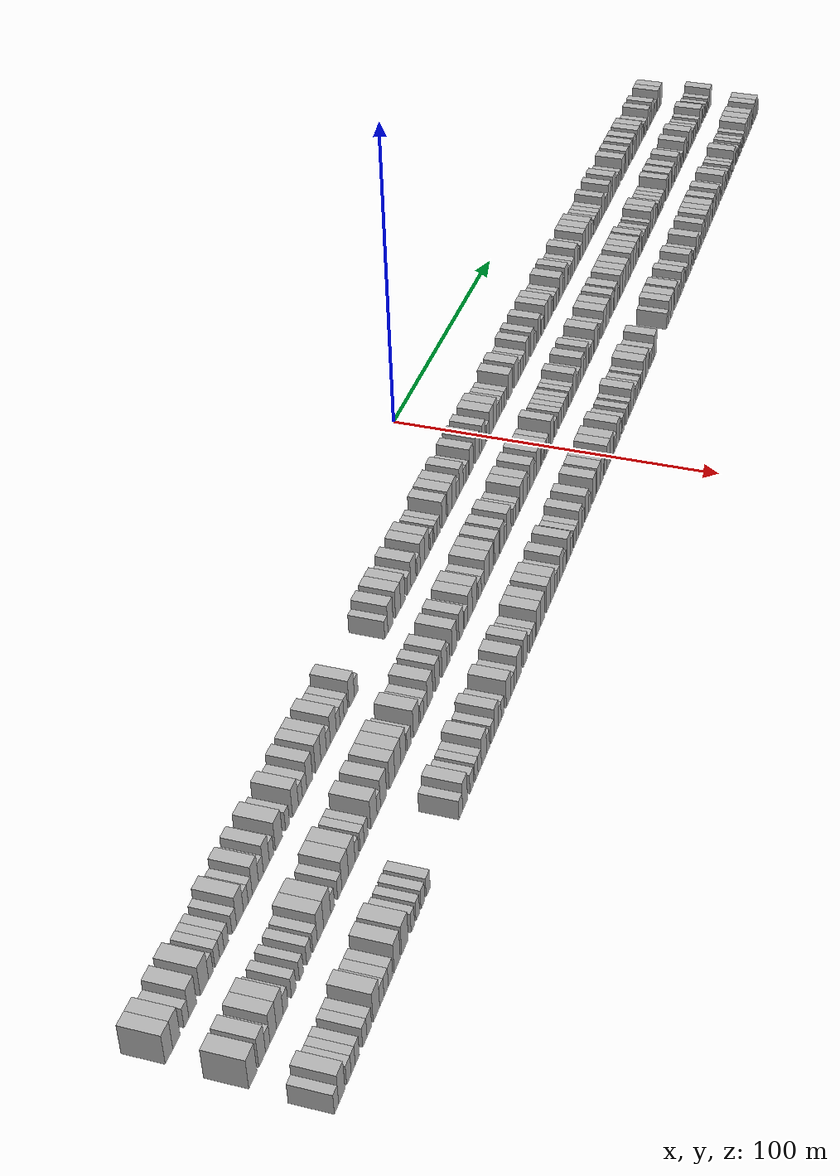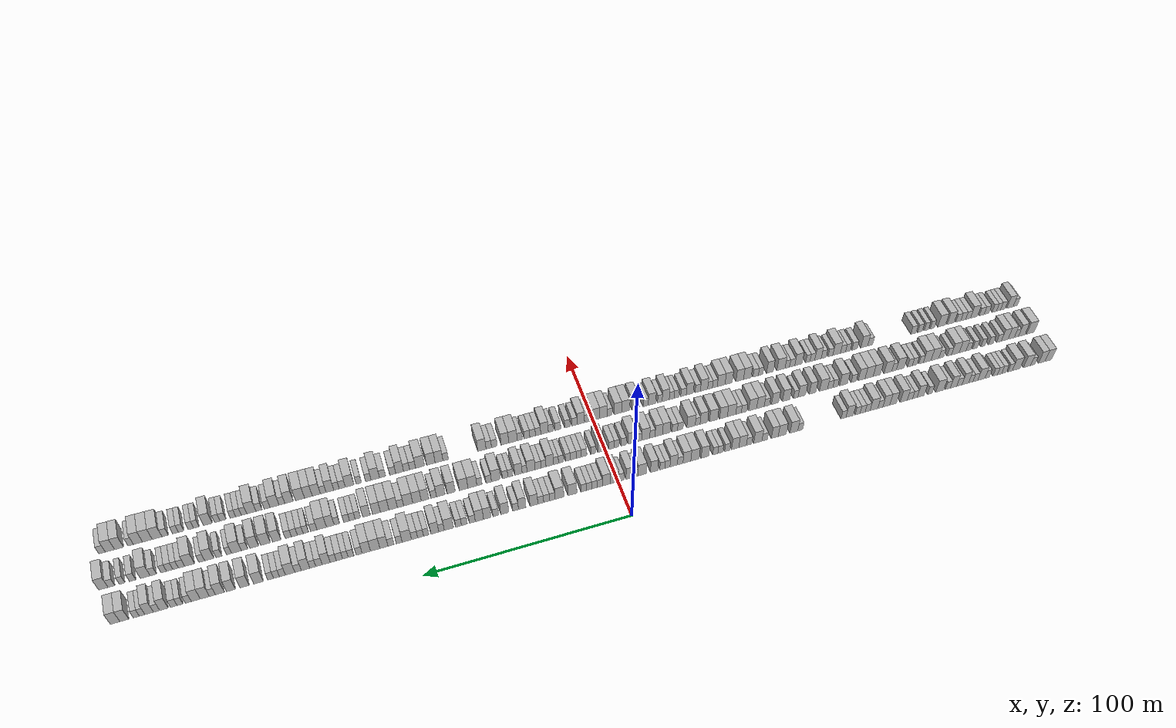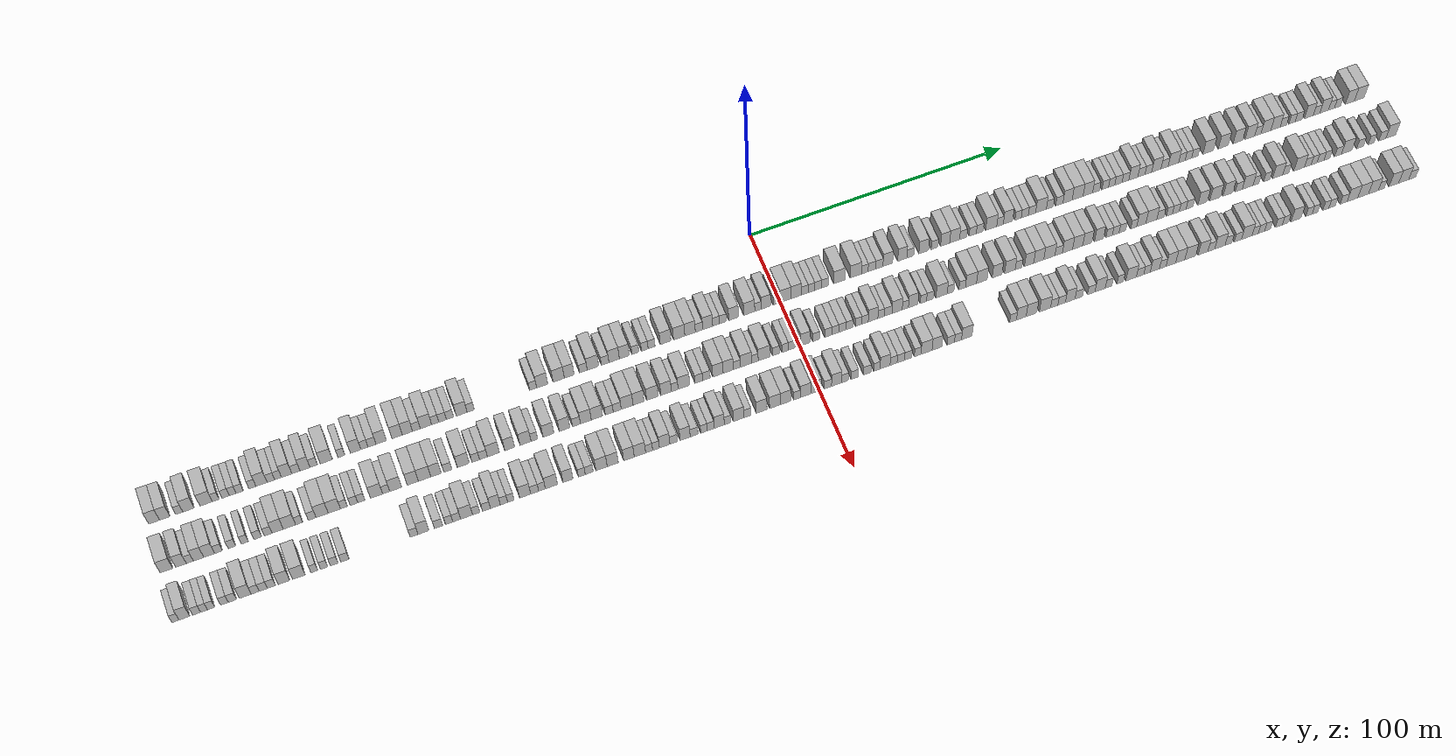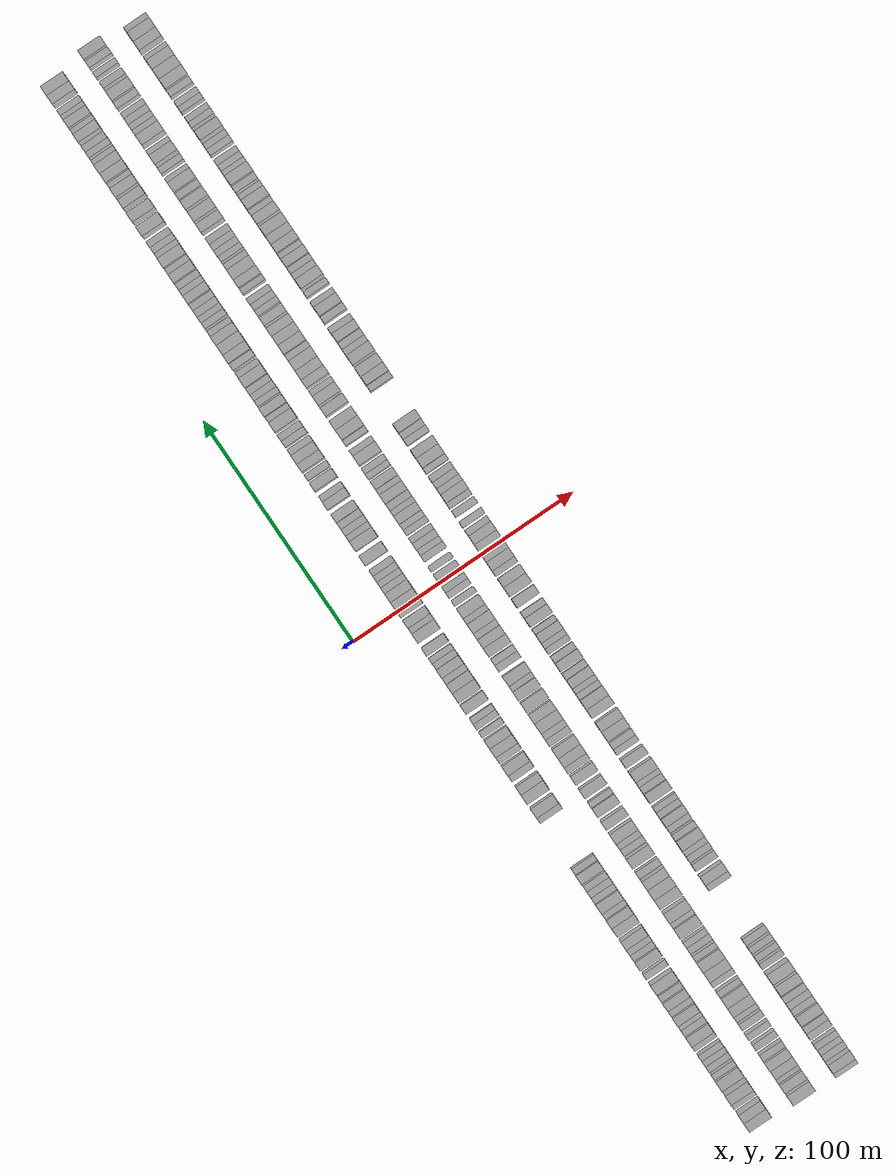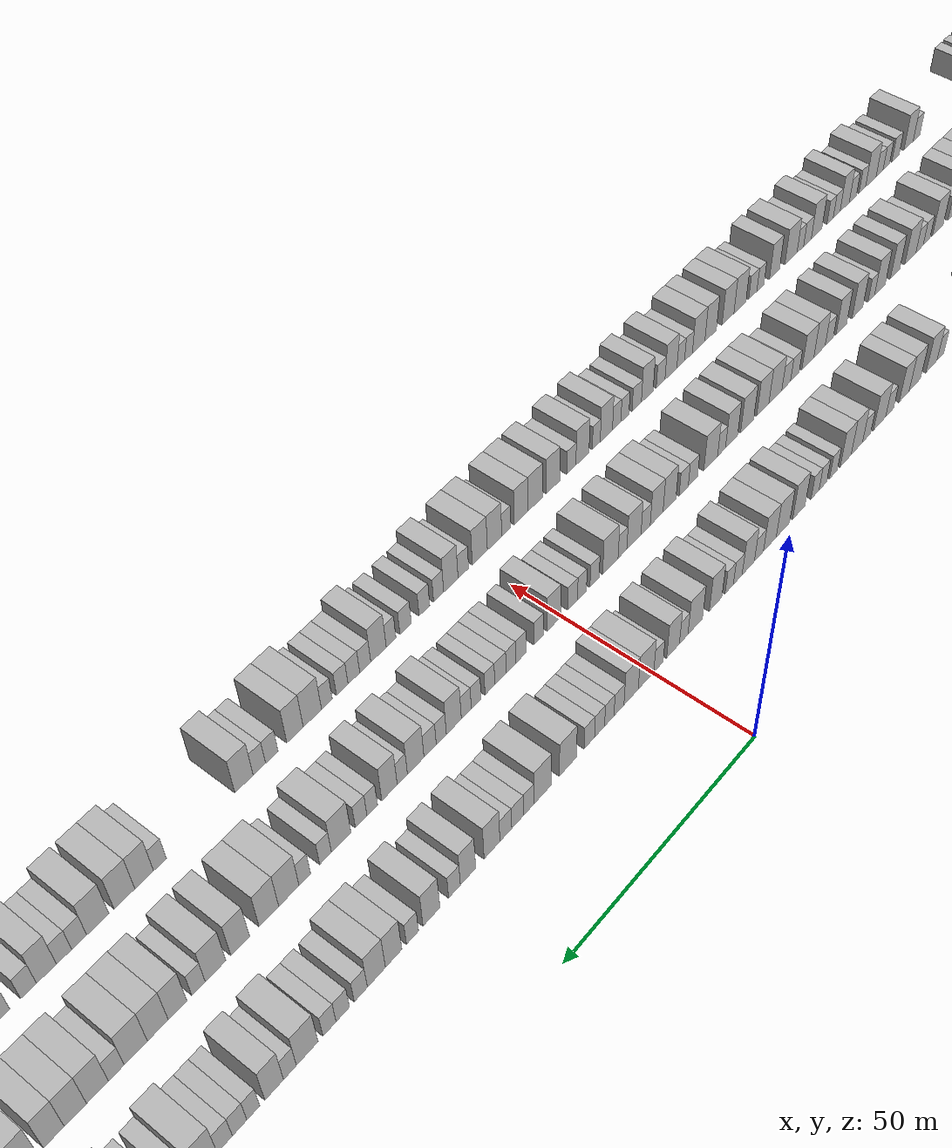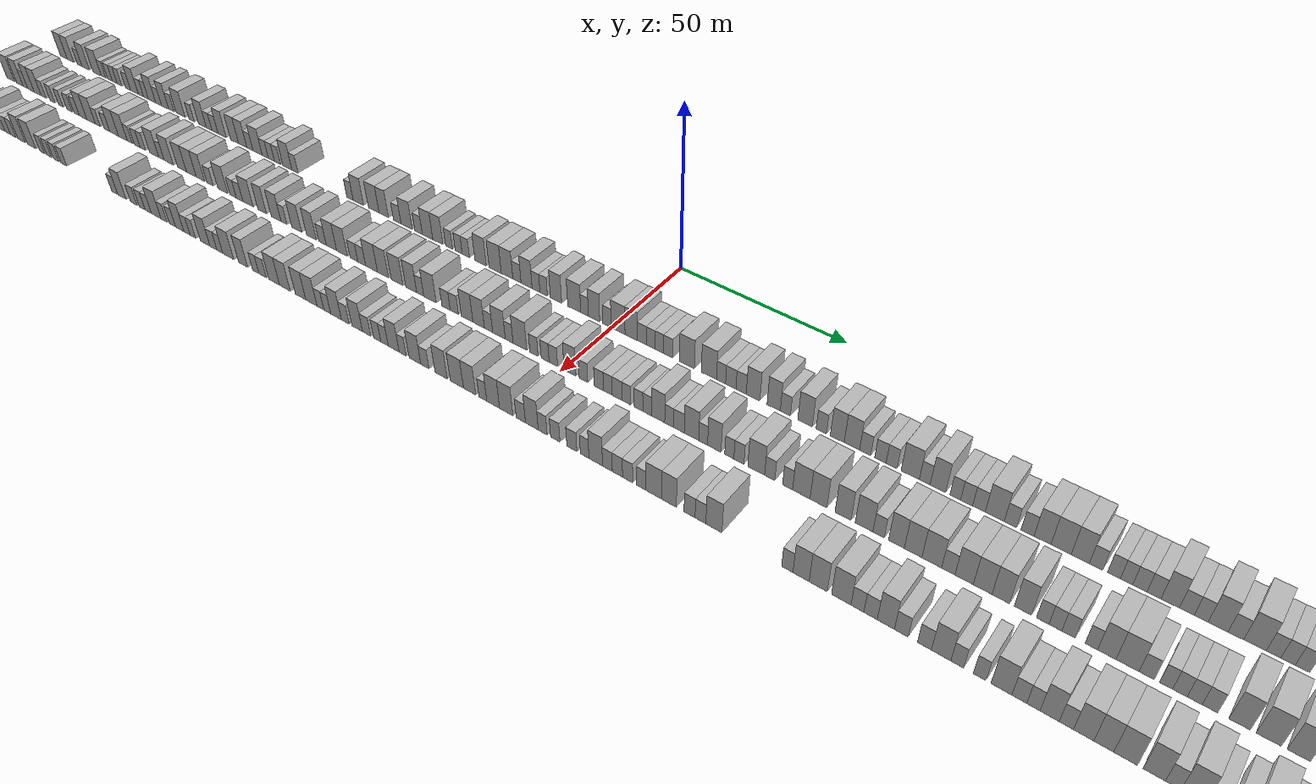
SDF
<sdf version="1.6">
 <world name="default">
  <scene>
   <sky><clouds><speed>12</speed></clouds></sky>
   <ambient>0.4 0.4 0.4 1</ambient>
   <background>0.7 0.7 0.7 1</background>
   <shadows>1</shadows>
  </scene>
  <gravity>0 0 -9.8066</gravity>
  <magnetic_field>6e-06 2.3e-05 -4.2e-05</magnetic_field>
  <physics default="0" name="default_physics" type="ode">
   <ode>
    <solver>
     <type>quick</type>
     <iters>10</iters>
     <sor>1.0</sor>
     <use_dynamic_moi_rescaling>0</use_dynamic_moi_rescaling>
    </solver>
    <constraints>
     <cfm>0</cfm>
     <erp>0.2</erp>
     <contact_max_correcting_vel>100</contact_max_correcting_vel>
     <contact_surface_layer>0.001</contact_surface_layer>
    </constraints>
   </ode>
   <max_step_size>0.004</max_step_size>
   <real_time_factor>1</real_time_factor>
   <real_time_update_rate>250</real_time_update_rate>
  </physics>
  <light name="sun" type="directional">
   <pose>0 0 10 0 0 0</pose>
   <diffuse>0.8 0.8 0.8 1</diffuse>
   <specular>0.2 0.2 0.2 1</specular>
   <attenuation>
    <range>1000</range>
    <constant>0.9</constant>
    <linear>0.01</linear>
    <quadratic>0.001</quadratic>
   </attenuation>
   <direction>-0.5 0.1 -0.9</direction>
  </light>
  <model name="building_1">
   <static>1</static>
   <pose>25.0000 -232.0690 0 0.000000 0.000000 0.000000</pose>
   <link name="link">
    <pose>0 0 4.50 0 0 0</pose>
    <collision name="collision"><geometry><box><size>10.0000 3.8621 9.0000</size></box></geometry></collision>
    <visual name="visual">
     <cast_shadows>0</cast_shadows>
     <geometry><box><size>10.0000 3.8621 9.0000</size></box></geometry>
     <material>
      <script>
       <uri>model://HANNAS_wall/materials/scripts</uri>
       <uri>model://HANNAS_wall/materials/textures</uri>
       <name>vrc/HANNAS_wall</name>
      </script>
     </material>
    </visual>
   </link>
  </model>
  <model name="building_2">
   <static>1</static>
   <pose>25.0000 -228.2816 0 0.000000 0.000000 0.000000</pose>
   <link name="link">
    <pose>0 0 4.50 0 0 0</pose>
    <collision name="collision"><geometry><box><size>10.0000 3.7126 9.0000</size></box></geometry></collision>
    <visual name="visual">
     <cast_shadows>0</cast_shadows>
     <geometry><box><size>10.0000 3.7126 9.0000</size></box></geometry>
     <material>
      <script>
       <uri>model://HANNAS_wall/materials/scripts</uri>
       <uri>model://HANNAS_wall/materials/textures</uri>
       <name>vrc/HANNAS_wall</name>
      </script>
     </material>
    </visual>
   </link>
  </model>
  <model name="building_3">
   <static>1</static>
   <pose>25.0000 -223.1535 0 0.000000 0.000000 0.000000</pose>
   <link name="link">
    <pose>0 0 3.00 0 0 0</pose>
    <collision name="collision"><geometry><box><size>10.0000 2.5438 6.0000</size></box></geometry></collision>
    <visual name="visual">
     <cast_shadows>0</cast_shadows>
     <geometry><box><size>10.0000 2.5438 6.0000</size></box></geometry>
     <material>
      <script>
       <uri>model://HANNAS_wall/materials/scripts</uri>
       <uri>model://HANNAS_wall/materials/textures</uri>
       <name>vrc/HANNAS_wall</name>
      </script>
     </material>
    </visual>
   </link>
  </model>
  <model name="building_4">
   <static>1</static>
   <pose>25.0000 -219.8326 0 0.000000 0.000000 0.000000</pose>
   <link name="link">
    <pose>0 0 4.50 0 0 0</pose>
    <collision name="collision"><geometry><box><size>10.0000 4.0980 9.0000</size></box></geometry></collision>
    <visual name="visual">
     <cast_shadows>0</cast_shadows>
     <geometry><box><size>10.0000 4.0980 9.0000</size></box></geometry>
     <material>
      <script>
       <uri>model://HANNAS_wall/materials/scripts</uri>
       <uri>model://HANNAS_wall/materials/textures</uri>
       <name>vrc/HANNAS_wall</name>
      </script>
     </material>
    </visual>
   </link>
  </model>
  <model name="building_5">
   <static>1</static>
   <pose>25.0000 -213.5639 0 0.000000 0.000000 0.000000</pose>
   <link name="link">
    <pose>0 0 4.50 0 0 0</pose>
    <collision name="collision"><geometry><box><size>10.0000 4.4393 9.0000</size></box></geometry></collision>
    <visual name="visual">
     <cast_shadows>0</cast_shadows>
     <geometry><box><size>10.0000 4.4393 9.0000</size></box></geometry>
     <material>
      <script>
       <uri>model://HANNAS_wall/materials/scripts</uri>
       <uri>model://HANNAS_wall/materials/textures</uri>
       <name>vrc/HANNAS_wall</name>
      </script>
     </material>
    </visual>
   </link>
  </model>
  <model name="building_6">
   <static>1</static>
   <pose>25.0000 -210.1234 0 0.000000 0.000000 0.000000</pose>
   <link name="link">
    <pose>0 0 3.00 0 0 0</pose>
    <collision name="collision"><geometry><box><size>10.0000 2.4418 6.0000</size></box></geometry></collision>
    <visual name="visual">
     <cast_shadows>0</cast_shadows>
     <geometry><box><size>10.0000 2.4418 6.0000</size></box></geometry>
     <material>
      <script>
       <uri>model://HANNAS_wall/materials/scripts</uri>
       <uri>model://HANNAS_wall/materials/textures</uri>
       <name>vrc/HANNAS_wall</name>
      </script>
     </material>
    </visual>
   </link>
  </model>
  <model name="building_7">
   <static>1</static>
   <pose>25.0000 -206.5913 0 0.000000 0.000000 0.000000</pose>
   <link name="link">
    <pose>0 0 3.00 0 0 0</pose>
    <collision name="collision"><geometry><box><size>10.0000 2.6224 6.0000</size></box></geometry></collision>
    <visual name="visual">
     <cast_shadows>0</cast_shadows>
     <geometry><box><size>10.0000 2.6224 6.0000</size></box></geometry>
     <material>
      <script>
       <uri>model://HANNAS_wall/materials/scripts</uri>
       <uri>model://HANNAS_wall/materials/textures</uri>
       <name>vrc/HANNAS_wall</name>
      </script>
     </material>
    </visual>
   </link>
  </model>
  <model name="building_8">
   <static>1</static>
   <pose>25.0000 -204.0491 0 0.000000 0.000000 0.000000</pose>
   <link name="link">
    <pose>0 0 3.00 0 0 0</pose>
    <collision name="collision"><geometry><box><size>10.0000 2.4620 6.0000</size></box></geometry></collision>
    <visual name="visual">
     <cast_shadows>0</cast_shadows>
     <geometry><box><size>10.0000 2.4620 6.0000</size></box></geometry>
     <material>
      <script>
       <uri>model://HANNAS_wall/materials/scripts</uri>
       <uri>model://HANNAS_wall/materials/textures</uri>
       <name>vrc/HANNAS_wall</name>
      </script>
     </material>
    </visual>
   </link>
  </model>
  <model name="building_9">
   <static>1</static>
   <pose>25.0000 -201.5387 0 0.000000 0.000000 0.000000</pose>
   <link name="link">
    <pose>0 0 3.00 0 0 0</pose>
    <collision name="collision"><geometry><box><size>10.0000 2.5589 6.0000</size></box></geometry></collision>
    <visual name="visual">
     <cast_shadows>0</cast_shadows>
     <geometry><box><size>10.0000 2.5589 6.0000</size></box></geometry>
     <material>
      <script>
       <uri>model://HANNAS_wall/materials/scripts</uri>
       <uri>model://HANNAS_wall/materials/textures</uri>
       <name>vrc/HANNAS_wall</name>
      </script>
     </material>
    </visual>
   </link>
  </model>
  <model name="building_10">
   <static>1</static>
   <pose>25.0000 -196.9926 0 0.000000 0.000000 0.000000</pose>
   <link name="link">
    <pose>0 0 3.00 0 0 0</pose>
    <collision name="collision"><geometry><box><size>10.0000 2.5333 6.0000</size></box></geometry></collision>
    <visual name="visual">
     <cast_shadows>0</cast_shadows>
     <geometry><box><size>10.0000 2.5333 6.0000</size></box></geometry>
     <material>
      <script>
       <uri>model://HANNAS_wall/materials/scripts</uri>
       <uri>model://HANNAS_wall/materials/textures</uri>
       <name>vrc/HANNAS_wall</name>
      </script>
     </material>
    </visual>
   </link>
  </model>
  <model name="building_11">
   <static>1</static>
   <pose>25.0000 -193.7096 0 0.000000 0.000000 0.000000</pose>
   <link name="link">
    <pose>0 0 4.50 0 0 0</pose>
    <collision name="collision"><geometry><box><size>10.0000 4.0325 9.0000</size></box></geometry></collision>
    <visual name="visual">
     <cast_shadows>0</cast_shadows>
     <geometry><box><size>10.0000 4.0325 9.0000</size></box></geometry>
     <material>
      <script>
       <uri>model://HANNAS_wall/materials/scripts</uri>
       <uri>model://HANNAS_wall/materials/textures</uri>
       <name>vrc/HANNAS_wall</name>
      </script>
     </material>
    </visual>
   </link>
  </model>
  <model name="building_12">
   <static>1</static>
   <pose>25.0000 -190.3162 0 0.000000 0.000000 0.000000</pose>
   <link name="link">
    <pose>0 0 3.00 0 0 0</pose>
    <collision name="collision"><geometry><box><size>10.0000 2.7544 6.0000</size></box></geometry></collision>
    <visual name="visual">
     <cast_shadows>0</cast_shadows>
     <geometry><box><size>10.0000 2.7544 6.0000</size></box></geometry>
     <material>
      <script>
       <uri>model://HANNAS_wall/materials/scripts</uri>
       <uri>model://HANNAS_wall/materials/textures</uri>
       <name>vrc/HANNAS_wall</name>
      </script>
     </material>
    </visual>
   </link>
  </model>
  <model name="building_13">
   <static>1</static>
   <pose>25.0000 -187.7275 0 0.000000 0.000000 0.000000</pose>
   <link name="link">
    <pose>0 0 3.00 0 0 0</pose>
    <collision name="collision"><geometry><box><size>10.0000 2.4229 6.0000</size></box></geometry></collision>
    <visual name="visual">
     <cast_shadows>0</cast_shadows>
     <geometry><box><size>10.0000 2.4229 6.0000</size></box></geometry>
     <material>
      <script>
       <uri>model://HANNAS_wall/materials/scripts</uri>
       <uri>model://HANNAS_wall/materials/textures</uri>
       <name>vrc/HANNAS_wall</name>
      </script>
     </material>
    </visual>
   </link>
  </model>
  <model name="building_14">
   <static>1</static>
   <pose>25.0000 -184.6353 0 0.000000 0.000000 0.000000</pose>
   <link name="link">
    <pose>0 0 4.50 0 0 0</pose>
    <collision name="collision"><geometry><box><size>10.0000 3.7617 9.0000</size></box></geometry></collision>
    <visual name="visual">
     <cast_shadows>0</cast_shadows>
     <geometry><box><size>10.0000 3.7617 9.0000</size></box></geometry>
     <material>
      <script>
       <uri>model://HANNAS_wall/materials/scripts</uri>
       <uri>model://HANNAS_wall/materials/textures</uri>
       <name>vrc/HANNAS_wall</name>
      </script>
     </material>
    </visual>
   </link>
  </model>
  <model name="building_15">
   <static>1</static>
   <pose>25.0000 -181.2803 0 0.000000 0.000000 0.000000</pose>
   <link name="link">
    <pose>0 0 3.00 0 0 0</pose>
    <collision name="collision"><geometry><box><size>10.0000 2.9483 6.0000</size></box></geometry></collision>
    <visual name="visual">
     <cast_shadows>0</cast_shadows>
     <geometry><box><size>10.0000 2.9483 6.0000</size></box></geometry>
     <material>
      <script>
       <uri>model://HANNAS_wall/materials/scripts</uri>
       <uri>model://HANNAS_wall/materials/textures</uri>
       <name>vrc/HANNAS_wall</name>
      </script>
     </material>
    </visual>
   </link>
  </model>
  <model name="building_16">
   <static>1</static>
   <pose>25.0000 -177.9995 0 0.000000 0.000000 0.000000</pose>
   <link name="link">
    <pose>0 0 4.50 0 0 0</pose>
    <collision name="collision"><geometry><box><size>10.0000 3.6132 9.0000</size></box></geometry></collision>
    <visual name="visual">
     <cast_shadows>0</cast_shadows>
     <geometry><box><size>10.0000 3.6132 9.0000</size></box></geometry>
     <material>
      <script>
       <uri>model://HANNAS_wall/materials/scripts</uri>
       <uri>model://HANNAS_wall/materials/textures</uri>
       <name>vrc/HANNAS_wall</name>
      </script>
     </material>
    </visual>
   </link>
  </model>
  <model name="building_17">
   <static>1</static>
   <pose>25.0000 -174.8447 0 0.000000 0.000000 0.000000</pose>
   <link name="link">
    <pose>0 0 3.00 0 0 0</pose>
    <collision name="collision"><geometry><box><size>10.0000 2.6965 6.0000</size></box></geometry></collision>
    <visual name="visual">
     <cast_shadows>0</cast_shadows>
     <geometry><box><size>10.0000 2.6965 6.0000</size></box></geometry>
     <material>
      <script>
       <uri>model://HANNAS_wall/materials/scripts</uri>
       <uri>model://HANNAS_wall/materials/textures</uri>
       <name>vrc/HANNAS_wall</name>
      </script>
     </material>
    </visual>
   </link>
  </model>
  <model name="building_18">
   <static>1</static>
   <pose>25.0000 -170.2805 0 0.000000 0.000000 0.000000</pose>
   <link name="link">
    <pose>0 0 4.50 0 0 0</pose>
    <collision name="collision"><geometry><box><size>10.0000 4.4319 9.0000</size></box></geometry></collision>
    <visual name="visual">
     <cast_shadows>0</cast_shadows>
     <geometry><box><size>10.0000 4.4319 9.0000</size></box></geometry>
     <material>
      <script>
       <uri>model://HANNAS_wall/materials/scripts</uri>
       <uri>model://HANNAS_wall/materials/textures</uri>
       <name>vrc/HANNAS_wall</name>
      </script>
     </material>
    </visual>
   </link>
  </model>
  <model name="building_19">
   <static>1</static>
   <pose>25.0000 -164.8110 0 0.000000 0.000000 0.000000</pose>
   <link name="link">
    <pose>0 0 3.00 0 0 0</pose>
    <collision name="collision"><geometry><box><size>10.0000 2.5070 6.0000</size></box></geometry></collision>
    <visual name="visual">
     <cast_shadows>0</cast_shadows>
     <geometry><box><size>10.0000 2.5070 6.0000</size></box></geometry>
     <material>
      <script>
       <uri>model://HANNAS_wall/materials/scripts</uri>
       <uri>model://HANNAS_wall/materials/textures</uri>
       <name>vrc/HANNAS_wall</name>
      </script>
     </material>
    </visual>
   </link>
  </model>
  <model name="building_20">
   <static>1</static>
   <pose>25.0000 -159.6483 0 0.000000 0.000000 0.000000</pose>
   <link name="link">
    <pose>0 0 4.50 0 0 0</pose>
    <collision name="collision"><geometry><box><size>10.0000 3.8185 9.0000</size></box></geometry></collision>
    <visual name="visual">
     <cast_shadows>0</cast_shadows>
     <geometry><box><size>10.0000 3.8185 9.0000</size></box></geometry>
     <material>
      <script>
       <uri>model://HANNAS_wall/materials/scripts</uri>
       <uri>model://HANNAS_wall/materials/textures</uri>
       <name>vrc/HANNAS_wall</name>
      </script>
     </material>
    </visual>
   </link>
  </model>
  <model name="building_21">
   <static>1</static>
   <pose>25.0000 -156.4367 0 0.000000 0.000000 0.000000</pose>
   <link name="link">
    <pose>0 0 3.00 0 0 0</pose>
    <collision name="collision"><geometry><box><size>10.0000 2.6046 6.0000</size></box></geometry></collision>
    <visual name="visual">
     <cast_shadows>0</cast_shadows>
     <geometry><box><size>10.0000 2.6046 6.0000</size></box></geometry>
     <material>
      <script>
       <uri>model://HANNAS_wall/materials/scripts</uri>
       <uri>model://HANNAS_wall/materials/textures</uri>
       <name>vrc/HANNAS_wall</name>
      </script>
     </material>
    </visual>
   </link>
  </model>
  <model name="building_22">
   <static>1</static>
   <pose>25.0000 -153.6787 0 0.000000 0.000000 0.000000</pose>
   <link name="link">
    <pose>0 0 3.00 0 0 0</pose>
    <collision name="collision"><geometry><box><size>10.0000 2.9116 6.0000</size></box></geometry></collision>
    <visual name="visual">
     <cast_shadows>0</cast_shadows>
     <geometry><box><size>10.0000 2.9116 6.0000</size></box></geometry>
     <material>
      <script>
       <uri>model://HANNAS_wall/materials/scripts</uri>
       <uri>model://HANNAS_wall/materials/textures</uri>
       <name>vrc/HANNAS_wall</name>
      </script>
     </material>
    </visual>
   </link>
  </model>
  <model name="building_23">
   <static>1</static>
   <pose>25.0000 -150.2912 0 0.000000 0.000000 0.000000</pose>
   <link name="link">
    <pose>0 0 4.50 0 0 0</pose>
    <collision name="collision"><geometry><box><size>10.0000 3.8634 9.0000</size></box></geometry></collision>
    <visual name="visual">
     <cast_shadows>0</cast_shadows>
     <geometry><box><size>10.0000 3.8634 9.0000</size></box></geometry>
     <material>
      <script>
       <uri>model://HANNAS_wall/materials/scripts</uri>
       <uri>model://HANNAS_wall/materials/textures</uri>
       <name>vrc/HANNAS_wall</name>
      </script>
     </material>
    </visual>
   </link>
  </model>
  <model name="building_24">
   <static>1</static>
   <pose>25.0000 -144.4624 0 0.000000 0.000000 0.000000</pose>
   <link name="link">
    <pose>0 0 4.50 0 0 0</pose>
    <collision name="collision"><geometry><box><size>10.0000 3.7941 9.0000</size></box></geometry></collision>
    <visual name="visual">
     <cast_shadows>0</cast_shadows>
     <geometry><box><size>10.0000 3.7941 9.0000</size></box></geometry>
     <material>
      <script>
       <uri>model://HANNAS_wall/materials/scripts</uri>
       <uri>model://HANNAS_wall/materials/textures</uri>
       <name>vrc/HANNAS_wall</name>
      </script>
     </material>
    </visual>
   </link>
  </model>
  <model name="building_25">
   <static>1</static>
   <pose>25.0000 -140.6812 0 0.000000 0.000000 0.000000</pose>
   <link name="link">
    <pose>0 0 4.50 0 0 0</pose>
    <collision name="collision"><geometry><box><size>10.0000 3.7682 9.0000</size></box></geometry></collision>
    <visual name="visual">
     <cast_shadows>0</cast_shadows>
     <geometry><box><size>10.0000 3.7682 9.0000</size></box></geometry>
     <material>
      <script>
       <uri>model://HANNAS_wall/materials/scripts</uri>
       <uri>model://HANNAS_wall/materials/textures</uri>
       <name>vrc/HANNAS_wall</name>
      </script>
     </material>
    </visual>
   </link>
  </model>
  <model name="building_26">
   <static>1</static>
   <pose>25.0000 -137.3999 0 0.000000 0.000000 0.000000</pose>
   <link name="link">
    <pose>0 0 3.00 0 0 0</pose>
    <collision name="collision"><geometry><box><size>10.0000 2.7946 6.0000</size></box></geometry></collision>
    <visual name="visual">
     <cast_shadows>0</cast_shadows>
     <geometry><box><size>10.0000 2.7946 6.0000</size></box></geometry>
     <material>
      <script>
       <uri>model://HANNAS_wall/materials/scripts</uri>
       <uri>model://HANNAS_wall/materials/textures</uri>
       <name>vrc/HANNAS_wall</name>
      </script>
     </material>
    </visual>
   </link>
  </model>
  <model name="building_27">
   <static>1</static>
   <pose>25.0000 -133.9004 0 0.000000 0.000000 0.000000</pose>
   <link name="link">
    <pose>0 0 4.50 0 0 0</pose>
    <collision name="collision"><geometry><box><size>10.0000 4.2043 9.0000</size></box></geometry></collision>
    <visual name="visual">
     <cast_shadows>0</cast_shadows>
     <geometry><box><size>10.0000 4.2043 9.0000</size></box></geometry>
     <material>
      <script>
       <uri>model://HANNAS_wall/materials/scripts</uri>
       <uri>model://HANNAS_wall/materials/textures</uri>
       <name>vrc/HANNAS_wall</name>
      </script>
     </material>
    </visual>
   </link>
  </model>
  <model name="building_28">
   <static>1</static>
   <pose>25.0000 -130.4720 0 0.000000 0.000000 0.000000</pose>
   <link name="link">
    <pose>0 0 3.00 0 0 0</pose>
    <collision name="collision"><geometry><box><size>10.0000 2.6524 6.0000</size></box></geometry></collision>
    <visual name="visual">
     <cast_shadows>0</cast_shadows>
     <geometry><box><size>10.0000 2.6524 6.0000</size></box></geometry>
     <material>
      <script>
       <uri>model://HANNAS_wall/materials/scripts</uri>
       <uri>model://HANNAS_wall/materials/textures</uri>
       <name>vrc/HANNAS_wall</name>
      </script>
     </material>
    </visual>
   </link>
  </model>
  <model name="building_29">
   <static>1</static>
   <pose>25.0000 -127.7629 0 0.000000 0.000000 0.000000</pose>
   <link name="link">
    <pose>0 0 3.00 0 0 0</pose>
    <collision name="collision"><geometry><box><size>10.0000 2.7659 6.0000</size></box></geometry></collision>
    <visual name="visual">
     <cast_shadows>0</cast_shadows>
     <geometry><box><size>10.0000 2.7659 6.0000</size></box></geometry>
     <material>
      <script>
       <uri>model://HANNAS_wall/materials/scripts</uri>
       <uri>model://HANNAS_wall/materials/textures</uri>
       <name>vrc/HANNAS_wall</name>
      </script>
     </material>
    </visual>
   </link>
  </model>
  <model name="building_30">
   <static>1</static>
   <pose>25.0000 -125.0303 0 0.000000 0.000000 0.000000</pose>
   <link name="link">
    <pose>0 0 3.00 0 0 0</pose>
    <collision name="collision"><geometry><box><size>10.0000 2.6993 6.0000</size></box></geometry></collision>
    <visual name="visual">
     <cast_shadows>0</cast_shadows>
     <geometry><box><size>10.0000 2.6993 6.0000</size></box></geometry>
     <material>
      <script>
       <uri>model://HANNAS_wall/materials/scripts</uri>
       <uri>model://HANNAS_wall/materials/textures</uri>
       <name>vrc/HANNAS_wall</name>
      </script>
     </material>
    </visual>
   </link>
  </model>
  <model name="building_31">
   <static>1</static>
   <pose>25.0000 -120.6938 0 0.000000 0.000000 0.000000</pose>
   <link name="link">
    <pose>0 0 4.50 0 0 0</pose>
    <collision name="collision"><geometry><box><size>10.0000 3.9736 9.0000</size></box></geometry></collision>
    <visual name="visual">
     <cast_shadows>0</cast_shadows>
     <geometry><box><size>10.0000 3.9736 9.0000</size></box></geometry>
     <material>
      <script>
       <uri>model://HANNAS_wall/materials/scripts</uri>
       <uri>model://HANNAS_wall/materials/textures</uri>
       <name>vrc/HANNAS_wall</name>
      </script>
     </material>
    </visual>
   </link>
  </model>
  <model name="building_32">
   <static>1</static>
   <pose>25.0000 -117.3727 0 0.000000 0.000000 0.000000</pose>
   <link name="link">
    <pose>0 0 3.00 0 0 0</pose>
    <collision name="collision"><geometry><box><size>10.0000 2.6687 6.0000</size></box></geometry></collision>
    <visual name="visual">
     <cast_shadows>0</cast_shadows>
     <geometry><box><size>10.0000 2.6687 6.0000</size></box></geometry>
     <material>
      <script>
       <uri>model://HANNAS_wall/materials/scripts</uri>
       <uri>model://HANNAS_wall/materials/textures</uri>
       <name>vrc/HANNAS_wall</name>
      </script>
     </material>
    </visual>
   </link>
  </model>
  <model name="building_33">
   <static>1</static>
   <pose>25.0000 -94.1306 0 0.000000 0.000000 0.000000</pose>
   <link name="link">
    <pose>0 0 3.00 0 0 0</pose>
    <collision name="collision"><geometry><box><size>10.0000 2.6051 6.0000</size></box></geometry></collision>
    <visual name="visual">
     <cast_shadows>0</cast_shadows>
     <geometry><box><size>10.0000 2.6051 6.0000</size></box></geometry>
     <material>
      <script>
       <uri>model://HANNAS_wall/materials/scripts</uri>
       <uri>model://HANNAS_wall/materials/textures</uri>
       <name>vrc/HANNAS_wall</name>
      </script>
     </material>
    </visual>
   </link>
  </model>
  <model name="building_34">
   <static>1</static>
   <pose>25.0000 -90.7363 0 0.000000 0.000000 0.000000</pose>
   <link name="link">
    <pose>0 0 4.50 0 0 0</pose>
    <collision name="collision"><geometry><box><size>10.0000 4.1834 9.0000</size></box></geometry></collision>
    <visual name="visual">
     <cast_shadows>0</cast_shadows>
     <geometry><box><size>10.0000 4.1834 9.0000</size></box></geometry>
     <material>
      <script>
       <uri>model://HANNAS_wall/materials/scripts</uri>
       <uri>model://HANNAS_wall/materials/textures</uri>
       <name>vrc/HANNAS_wall</name>
      </script>
     </material>
    </visual>
   </link>
  </model>
  <model name="building_35">
   <static>1</static>
   <pose>25.0000 -84.5259 0 0.000000 0.000000 0.000000</pose>
   <link name="link">
    <pose>0 0 4.50 0 0 0</pose>
    <collision name="collision"><geometry><box><size>10.0000 4.2373 9.0000</size></box></geometry></collision>
    <visual name="visual">
     <cast_shadows>0</cast_shadows>
     <geometry><box><size>10.0000 4.2373 9.0000</size></box></geometry>
     <material>
      <script>
       <uri>model://HANNAS_wall/materials/scripts</uri>
       <uri>model://HANNAS_wall/materials/textures</uri>
       <name>vrc/HANNAS_wall</name>
      </script>
     </material>
    </visual>
   </link>
  </model>
  <model name="building_36">
   <static>1</static>
   <pose>25.0000 -80.5714 0 0.000000 0.000000 0.000000</pose>
   <link name="link">
    <pose>0 0 4.50 0 0 0</pose>
    <collision name="collision"><geometry><box><size>10.0000 3.6718 9.0000</size></box></geometry></collision>
    <visual name="visual">
     <cast_shadows>0</cast_shadows>
     <geometry><box><size>10.0000 3.6718 9.0000</size></box></geometry>
     <material>
      <script>
       <uri>model://HANNAS_wall/materials/scripts</uri>
       <uri>model://HANNAS_wall/materials/textures</uri>
       <name>vrc/HANNAS_wall</name>
      </script>
     </material>
    </visual>
   </link>
  </model>
  <model name="building_37">
   <static>1</static>
   <pose>25.0000 -75.2825 0 0.000000 0.000000 0.000000</pose>
   <link name="link">
    <pose>0 0 3.00 0 0 0</pose>
    <collision name="collision"><geometry><box><size>10.0000 2.9061 6.0000</size></box></geometry></collision>
    <visual name="visual">
     <cast_shadows>0</cast_shadows>
     <geometry><box><size>10.0000 2.9061 6.0000</size></box></geometry>
     <material>
      <script>
       <uri>model://HANNAS_wall/materials/scripts</uri>
       <uri>model://HANNAS_wall/materials/textures</uri>
       <name>vrc/HANNAS_wall</name>
      </script>
     </material>
    </visual>
   </link>
  </model>
  <model name="building_38">
   <static>1</static>
   <pose>25.0000 -71.6623 0 0.000000 0.000000 0.000000</pose>
   <link name="link">
    <pose>0 0 4.50 0 0 0</pose>
    <collision name="collision"><geometry><box><size>10.0000 4.3342 9.0000</size></box></geometry></collision>
    <visual name="visual">
     <cast_shadows>0</cast_shadows>
     <geometry><box><size>10.0000 4.3342 9.0000</size></box></geometry>
     <material>
      <script>
       <uri>model://HANNAS_wall/materials/scripts</uri>
       <uri>model://HANNAS_wall/materials/textures</uri>
       <name>vrc/HANNAS_wall</name>
      </script>
     </material>
    </visual>
   </link>
  </model>
  <model name="building_39">
   <static>1</static>
   <pose>25.0000 -67.0746 0 0.000000 0.000000 0.000000</pose>
   <link name="link">
    <pose>0 0 3.00 0 0 0</pose>
    <collision name="collision"><geometry><box><size>10.0000 2.8413 6.0000</size></box></geometry></collision>
    <visual name="visual">
     <cast_shadows>0</cast_shadows>
     <geometry><box><size>10.0000 2.8413 6.0000</size></box></geometry>
     <material>
      <script>
       <uri>model://HANNAS_wall/materials/scripts</uri>
       <uri>model://HANNAS_wall/materials/textures</uri>
       <name>vrc/HANNAS_wall</name>
      </script>
     </material>
    </visual>
   </link>
  </model>
  <model name="building_40">
   <static>1</static>
   <pose>25.0000 -63.6669 0 0.000000 0.000000 0.000000</pose>
   <link name="link">
    <pose>0 0 4.50 0 0 0</pose>
    <collision name="collision"><geometry><box><size>10.0000 3.9742 9.0000</size></box></geometry></collision>
    <visual name="visual">
     <cast_shadows>0</cast_shadows>
     <geometry><box><size>10.0000 3.9742 9.0000</size></box></geometry>
     <material>
      <script>
       <uri>model://HANNAS_wall/materials/scripts</uri>
       <uri>model://HANNAS_wall/materials/textures</uri>
       <name>vrc/HANNAS_wall</name>
      </script>
     </material>
    </visual>
   </link>
  </model>
  <model name="building_41">
   <static>1</static>
   <pose>25.0000 -59.8022 0 0.000000 0.000000 0.000000</pose>
   <link name="link">
    <pose>0 0 4.50 0 0 0</pose>
    <collision name="collision"><geometry><box><size>10.0000 3.7553 9.0000</size></box></geometry></collision>
    <visual name="visual">
     <cast_shadows>0</cast_shadows>
     <geometry><box><size>10.0000 3.7553 9.0000</size></box></geometry>
     <material>
      <script>
       <uri>model://HANNAS_wall/materials/scripts</uri>
       <uri>model://HANNAS_wall/materials/textures</uri>
       <name>vrc/HANNAS_wall</name>
      </script>
     </material>
    </visual>
   </link>
  </model>
  <model name="building_42">
   <static>1</static>
   <pose>25.0000 -55.6284 0 0.000000 0.000000 0.000000</pose>
   <link name="link">
    <pose>0 0 3.00 0 0 0</pose>
    <collision name="collision"><geometry><box><size>10.0000 2.5923 6.0000</size></box></geometry></collision>
    <visual name="visual">
     <cast_shadows>0</cast_shadows>
     <geometry><box><size>10.0000 2.5923 6.0000</size></box></geometry>
     <material>
      <script>
       <uri>model://HANNAS_wall/materials/scripts</uri>
       <uri>model://HANNAS_wall/materials/textures</uri>
       <name>vrc/HANNAS_wall</name>
      </script>
     </material>
    </visual>
   </link>
  </model>
  <model name="building_43">
   <static>1</static>
   <pose>25.0000 -52.0600 0 0.000000 0.000000 0.000000</pose>
   <link name="link">
    <pose>0 0 3.00 0 0 0</pose>
    <collision name="collision"><geometry><box><size>10.0000 2.5443 6.0000</size></box></geometry></collision>
    <visual name="visual">
     <cast_shadows>0</cast_shadows>
     <geometry><box><size>10.0000 2.5443 6.0000</size></box></geometry>
     <material>
      <script>
       <uri>model://HANNAS_wall/materials/scripts</uri>
       <uri>model://HANNAS_wall/materials/textures</uri>
       <name>vrc/HANNAS_wall</name>
      </script>
     </material>
    </visual>
   </link>
  </model>
  <model name="building_44">
   <static>1</static>
   <pose>25.0000 -49.4723 0 0.000000 0.000000 0.000000</pose>
   <link name="link">
    <pose>0 0 3.00 0 0 0</pose>
    <collision name="collision"><geometry><box><size>10.0000 2.6311 6.0000</size></box></geometry></collision>
    <visual name="visual">
     <cast_shadows>0</cast_shadows>
     <geometry><box><size>10.0000 2.6311 6.0000</size></box></geometry>
     <material>
      <script>
       <uri>model://HANNAS_wall/materials/scripts</uri>
       <uri>model://HANNAS_wall/materials/textures</uri>
       <name>vrc/HANNAS_wall</name>
      </script>
     </material>
    </visual>
   </link>
  </model>
  <model name="building_45">
   <static>1</static>
   <pose>25.0000 -44.1306 0 0.000000 0.000000 0.000000</pose>
   <link name="link">
    <pose>0 0 4.50 0 0 0</pose>
    <collision name="collision"><geometry><box><size>10.0000 4.0522 9.0000</size></box></geometry></collision>
    <visual name="visual">
     <cast_shadows>0</cast_shadows>
     <geometry><box><size>10.0000 4.0522 9.0000</size></box></geometry>
     <material>
      <script>
       <uri>model://HANNAS_wall/materials/scripts</uri>
       <uri>model://HANNAS_wall/materials/textures</uri>
       <name>vrc/HANNAS_wall</name>
      </script>
     </material>
    </visual>
   </link>
  </model>
  <model name="building_46">
   <static>1</static>
   <pose>25.0000 -38.9556 0 0.000000 0.000000 0.000000</pose>
   <link name="link">
    <pose>0 0 4.50 0 0 0</pose>
    <collision name="collision"><geometry><box><size>10.0000 4.2977 9.0000</size></box></geometry></collision>
    <visual name="visual">
     <cast_shadows>0</cast_shadows>
     <geometry><box><size>10.0000 4.2977 9.0000</size></box></geometry>
     <material>
      <script>
       <uri>model://HANNAS_wall/materials/scripts</uri>
       <uri>model://HANNAS_wall/materials/textures</uri>
       <name>vrc/HANNAS_wall</name>
      </script>
     </material>
    </visual>
   </link>
  </model>
  <model name="building_47">
   <static>1</static>
   <pose>25.0000 -34.7910 0 0.000000 0.000000 0.000000</pose>
   <link name="link">
    <pose>0 0 4.50 0 0 0</pose>
    <collision name="collision"><geometry><box><size>10.0000 4.0316 9.0000</size></box></geometry></collision>
    <visual name="visual">
     <cast_shadows>0</cast_shadows>
     <geometry><box><size>10.0000 4.0316 9.0000</size></box></geometry>
     <material>
      <script>
       <uri>model://HANNAS_wall/materials/scripts</uri>
       <uri>model://HANNAS_wall/materials/textures</uri>
       <name>vrc/HANNAS_wall</name>
      </script>
     </material>
    </visual>
   </link>
  </model>
  <model name="building_48">
   <static>1</static>
   <pose>25.0000 -31.3547 0 0.000000 0.000000 0.000000</pose>
   <link name="link">
    <pose>0 0 3.00 0 0 0</pose>
    <collision name="collision"><geometry><box><size>10.0000 2.8410 6.0000</size></box></geometry></collision>
    <visual name="visual">
     <cast_shadows>0</cast_shadows>
     <geometry><box><size>10.0000 2.8410 6.0000</size></box></geometry>
     <material>
      <script>
       <uri>model://HANNAS_wall/materials/scripts</uri>
       <uri>model://HANNAS_wall/materials/textures</uri>
       <name>vrc/HANNAS_wall</name>
      </script>
     </material>
    </visual>
   </link>
  </model>
  <model name="building_49">
   <static>1</static>
   <pose>25.0000 -28.0334 0 0.000000 0.000000 0.000000</pose>
   <link name="link">
    <pose>0 0 4.50 0 0 0</pose>
    <collision name="collision"><geometry><box><size>10.0000 3.8015 9.0000</size></box></geometry></collision>
    <visual name="visual">
     <cast_shadows>0</cast_shadows>
     <geometry><box><size>10.0000 3.8015 9.0000</size></box></geometry>
     <material>
      <script>
       <uri>model://HANNAS_wall/materials/scripts</uri>
       <uri>model://HANNAS_wall/materials/textures</uri>
       <name>vrc/HANNAS_wall</name>
      </script>
     </material>
    </visual>
   </link>
  </model>
  <model name="building_50">
   <static>1</static>
   <pose>25.0000 -24.7990 0 0.000000 0.000000 0.000000</pose>
   <link name="link">
    <pose>0 0 3.00 0 0 0</pose>
    <collision name="collision"><geometry><box><size>10.0000 2.6674 6.0000</size></box></geometry></collision>
    <visual name="visual">
     <cast_shadows>0</cast_shadows>
     <geometry><box><size>10.0000 2.6674 6.0000</size></box></geometry>
     <material>
      <script>
       <uri>model://HANNAS_wall/materials/scripts</uri>
       <uri>model://HANNAS_wall/materials/textures</uri>
       <name>vrc/HANNAS_wall</name>
      </script>
     </material>
    </visual>
   </link>
  </model>
  <model name="building_51">
   <static>1</static>
   <pose>25.0000 -22.2155 0 0.000000 0.000000 0.000000</pose>
   <link name="link">
    <pose>0 0 3.00 0 0 0</pose>
    <collision name="collision"><geometry><box><size>10.0000 2.4995 6.0000</size></box></geometry></collision>
    <visual name="visual">
     <cast_shadows>0</cast_shadows>
     <geometry><box><size>10.0000 2.4995 6.0000</size></box></geometry>
     <material>
      <script>
       <uri>model://HANNAS_wall/materials/scripts</uri>
       <uri>model://HANNAS_wall/materials/textures</uri>
       <name>vrc/HANNAS_wall</name>
      </script>
     </material>
    </visual>
   </link>
  </model>
  <model name="building_52">
   <static>1</static>
   <pose>25.0000 -18.0895 0 0.000000 0.000000 0.000000</pose>
   <link name="link">
    <pose>0 0 4.50 0 0 0</pose>
    <collision name="collision"><geometry><box><size>10.0000 3.7524 9.0000</size></box></geometry></collision>
    <visual name="visual">
     <cast_shadows>0</cast_shadows>
     <geometry><box><size>10.0000 3.7524 9.0000</size></box></geometry>
     <material>
      <script>
       <uri>model://HANNAS_wall/materials/scripts</uri>
       <uri>model://HANNAS_wall/materials/textures</uri>
       <name>vrc/HANNAS_wall</name>
      </script>
     </material>
    </visual>
   </link>
  </model>
  <model name="building_53">
   <static>1</static>
   <pose>25.0000 -12.0707 0 0.000000 0.000000 0.000000</pose>
   <link name="link">
    <pose>0 0 4.50 0 0 0</pose>
    <collision name="collision"><geometry><box><size>10.0000 4.2852 9.0000</size></box></geometry></collision>
    <visual name="visual">
     <cast_shadows>0</cast_shadows>
     <geometry><box><size>10.0000 4.2852 9.0000</size></box></geometry>
     <material>
      <script>
       <uri>model://HANNAS_wall/materials/scripts</uri>
       <uri>model://HANNAS_wall/materials/textures</uri>
       <name>vrc/HANNAS_wall</name>
      </script>
     </material>
    </visual>
   </link>
  </model>
  <model name="building_54">
   <static>1</static>
   <pose>25.0000 -8.6924 0 0.000000 0.000000 0.000000</pose>
   <link name="link">
    <pose>0 0 3.00 0 0 0</pose>
    <collision name="collision"><geometry><box><size>10.0000 2.4713 6.0000</size></box></geometry></collision>
    <visual name="visual">
     <cast_shadows>0</cast_shadows>
     <geometry><box><size>10.0000 2.4713 6.0000</size></box></geometry>
     <material>
      <script>
       <uri>model://HANNAS_wall/materials/scripts</uri>
       <uri>model://HANNAS_wall/materials/textures</uri>
       <name>vrc/HANNAS_wall</name>
      </script>
     </material>
    </visual>
   </link>
  </model>
  <model name="building_55">
   <static>1</static>
   <pose>25.0000 -5.6387 0 0.000000 0.000000 0.000000</pose>
   <link name="link">
    <pose>0 0 4.50 0 0 0</pose>
    <collision name="collision"><geometry><box><size>10.0000 3.6361 9.0000</size></box></geometry></collision>
    <visual name="visual">
     <cast_shadows>0</cast_shadows>
     <geometry><box><size>10.0000 3.6361 9.0000</size></box></geometry>
     <material>
      <script>
       <uri>model://HANNAS_wall/materials/scripts</uri>
       <uri>model://HANNAS_wall/materials/textures</uri>
       <name>vrc/HANNAS_wall</name>
      </script>
     </material>
    </visual>
   </link>
  </model>
  <model name="building_56">
   <static>1</static>
   <pose>25.0000 -1.4994 0 0.000000 0.000000 0.000000</pose>
   <link name="link">
    <pose>0 0 3.00 0 0 0</pose>
    <collision name="collision"><geometry><box><size>10.0000 2.6427 6.0000</size></box></geometry></collision>
    <visual name="visual">
     <cast_shadows>0</cast_shadows>
     <geometry><box><size>10.0000 2.6427 6.0000</size></box></geometry>
     <material>
      <script>
       <uri>model://HANNAS_wall/materials/scripts</uri>
       <uri>model://HANNAS_wall/materials/textures</uri>
       <name>vrc/HANNAS_wall</name>
      </script>
     </material>
    </visual>
   </link>
  </model>
  <model name="building_57">
   <static>1</static>
   <pose>25.0000 1.9931 0 0.000000 0.000000 0.000000</pose>
   <link name="link">
    <pose>0 0 4.50 0 0 0</pose>
    <collision name="collision"><geometry><box><size>10.0000 4.3422 9.0000</size></box></geometry></collision>
    <visual name="visual">
     <cast_shadows>0</cast_shadows>
     <geometry><box><size>10.0000 4.3422 9.0000</size></box></geometry>
     <material>
      <script>
       <uri>model://HANNAS_wall/materials/scripts</uri>
       <uri>model://HANNAS_wall/materials/textures</uri>
       <name>vrc/HANNAS_wall</name>
      </script>
     </material>
    </visual>
   </link>
  </model>
  <model name="building_58">
   <static>1</static>
   <pose>25.0000 6.1227 0 0.000000 0.000000 0.000000</pose>
   <link name="link">
    <pose>0 0 4.50 0 0 0</pose>
    <collision name="collision"><geometry><box><size>10.0000 3.9170 9.0000</size></box></geometry></collision>
    <visual name="visual">
     <cast_shadows>0</cast_shadows>
     <geometry><box><size>10.0000 3.9170 9.0000</size></box></geometry>
     <material>
      <script>
       <uri>model://HANNAS_wall/materials/scripts</uri>
       <uri>model://HANNAS_wall/materials/textures</uri>
       <name>vrc/HANNAS_wall</name>
      </script>
     </material>
    </visual>
   </link>
  </model>
  <model name="building_59">
   <static>1</static>
   <pose>25.0000 9.4353 0 0.000000 0.000000 0.000000</pose>
   <link name="link">
    <pose>0 0 3.00 0 0 0</pose>
    <collision name="collision"><geometry><box><size>10.0000 2.7080 6.0000</size></box></geometry></collision>
    <visual name="visual">
     <cast_shadows>0</cast_shadows>
     <geometry><box><size>10.0000 2.7080 6.0000</size></box></geometry>
     <material>
      <script>
       <uri>model://HANNAS_wall/materials/scripts</uri>
       <uri>model://HANNAS_wall/materials/textures</uri>
       <name>vrc/HANNAS_wall</name>
      </script>
     </material>
    </visual>
   </link>
  </model>
  <model name="building_60">
   <static>1</static>
   <pose>25.0000 12.0577 0 0.000000 0.000000 0.000000</pose>
   <link name="link">
    <pose>0 0 3.00 0 0 0</pose>
    <collision name="collision"><geometry><box><size>10.0000 2.5369 6.0000</size></box></geometry></collision>
    <visual name="visual">
     <cast_shadows>0</cast_shadows>
     <geometry><box><size>10.0000 2.5369 6.0000</size></box></geometry>
     <material>
      <script>
       <uri>model://HANNAS_wall/materials/scripts</uri>
       <uri>model://HANNAS_wall/materials/textures</uri>
       <name>vrc/HANNAS_wall</name>
      </script>
     </material>
    </visual>
   </link>
  </model>
  <model name="building_61">
   <static>1</static>
   <pose>25.0000 14.6599 0 0.000000 0.000000 0.000000</pose>
   <link name="link">
    <pose>0 0 3.00 0 0 0</pose>
    <collision name="collision"><geometry><box><size>10.0000 2.6675 6.0000</size></box></geometry></collision>
    <visual name="visual">
     <cast_shadows>0</cast_shadows>
     <geometry><box><size>10.0000 2.6675 6.0000</size></box></geometry>
     <material>
      <script>
       <uri>model://HANNAS_wall/materials/scripts</uri>
       <uri>model://HANNAS_wall/materials/textures</uri>
       <name>vrc/HANNAS_wall</name>
      </script>
     </material>
    </visual>
   </link>
  </model>
  <model name="building_62">
   <static>1</static>
   <pose>25.0000 17.3658 0 0.000000 0.000000 0.000000</pose>
   <link name="link">
    <pose>0 0 3.00 0 0 0</pose>
    <collision name="collision"><geometry><box><size>10.0000 2.7442 6.0000</size></box></geometry></collision>
    <visual name="visual">
     <cast_shadows>0</cast_shadows>
     <geometry><box><size>10.0000 2.7442 6.0000</size></box></geometry>
     <material>
      <script>
       <uri>model://HANNAS_wall/materials/scripts</uri>
       <uri>model://HANNAS_wall/materials/textures</uri>
       <name>vrc/HANNAS_wall</name>
      </script>
     </material>
    </visual>
   </link>
  </model>
  <model name="building_63">
   <static>1</static>
   <pose>25.0000 22.9496 0 0.000000 0.000000 0.000000</pose>
   <link name="link">
    <pose>0 0 4.50 0 0 0</pose>
    <collision name="collision"><geometry><box><size>10.0000 4.4235 9.0000</size></box></geometry></collision>
    <visual name="visual">
     <cast_shadows>0</cast_shadows>
     <geometry><box><size>10.0000 4.4235 9.0000</size></box></geometry>
     <material>
      <script>
       <uri>model://HANNAS_wall/materials/scripts</uri>
       <uri>model://HANNAS_wall/materials/textures</uri>
       <name>vrc/HANNAS_wall</name>
      </script>
     </material>
    </visual>
   </link>
  </model>
  <model name="building_64">
   <static>1</static>
   <pose>25.0000 29.3589 0 0.000000 0.000000 0.000000</pose>
   <link name="link">
    <pose>0 0 4.50 0 0 0</pose>
    <collision name="collision"><geometry><box><size>10.0000 4.3949 9.0000</size></box></geometry></collision>
    <visual name="visual">
     <cast_shadows>0</cast_shadows>
     <geometry><box><size>10.0000 4.3949 9.0000</size></box></geometry>
     <material>
      <script>
       <uri>model://HANNAS_wall/materials/scripts</uri>
       <uri>model://HANNAS_wall/materials/textures</uri>
       <name>vrc/HANNAS_wall</name>
      </script>
     </material>
    </visual>
   </link>
  </model>
  <model name="building_65">
   <static>1</static>
   <pose>25.0000 32.8675 0 0.000000 0.000000 0.000000</pose>
   <link name="link">
    <pose>0 0 3.00 0 0 0</pose>
    <collision name="collision"><geometry><box><size>10.0000 2.6224 6.0000</size></box></geometry></collision>
    <visual name="visual">
     <cast_shadows>0</cast_shadows>
     <geometry><box><size>10.0000 2.6224 6.0000</size></box></geometry>
     <material>
      <script>
       <uri>model://HANNAS_wall/materials/scripts</uri>
       <uri>model://HANNAS_wall/materials/textures</uri>
       <name>vrc/HANNAS_wall</name>
      </script>
     </material>
    </visual>
   </link>
  </model>
  <model name="building_66">
   <static>1</static>
   <pose>25.0000 35.6448 0 0.000000 0.000000 0.000000</pose>
   <link name="link">
    <pose>0 0 3.00 0 0 0</pose>
    <collision name="collision"><geometry><box><size>10.0000 2.9322 6.0000</size></box></geometry></collision>
    <visual name="visual">
     <cast_shadows>0</cast_shadows>
     <geometry><box><size>10.0000 2.9322 6.0000</size></box></geometry>
     <material>
      <script>
       <uri>model://HANNAS_wall/materials/scripts</uri>
       <uri>model://HANNAS_wall/materials/textures</uri>
       <name>vrc/HANNAS_wall</name>
      </script>
     </material>
    </visual>
   </link>
  </model>
  <model name="building_67">
   <static>1</static>
   <pose>25.0000 38.5569 0 0.000000 0.000000 0.000000</pose>
   <link name="link">
    <pose>0 0 3.00 0 0 0</pose>
    <collision name="collision"><geometry><box><size>10.0000 2.8921 6.0000</size></box></geometry></collision>
    <visual name="visual">
     <cast_shadows>0</cast_shadows>
     <geometry><box><size>10.0000 2.8921 6.0000</size></box></geometry>
     <material>
      <script>
       <uri>model://HANNAS_wall/materials/scripts</uri>
       <uri>model://HANNAS_wall/materials/textures</uri>
       <name>vrc/HANNAS_wall</name>
      </script>
     </material>
    </visual>
   </link>
  </model>
  <model name="building_68">
   <static>1</static>
   <pose>25.0000 41.9064 0 0.000000 0.000000 0.000000</pose>
   <link name="link">
    <pose>0 0 4.50 0 0 0</pose>
    <collision name="collision"><geometry><box><size>10.0000 3.8069 9.0000</size></box></geometry></collision>
    <visual name="visual">
     <cast_shadows>0</cast_shadows>
     <geometry><box><size>10.0000 3.8069 9.0000</size></box></geometry>
     <material>
      <script>
       <uri>model://HANNAS_wall/materials/scripts</uri>
       <uri>model://HANNAS_wall/materials/textures</uri>
       <name>vrc/HANNAS_wall</name>
      </script>
     </material>
    </visual>
   </link>
  </model>
  <model name="building_69">
   <static>1</static>
   <pose>25.0000 47.6128 0 0.000000 0.000000 0.000000</pose>
   <link name="link">
    <pose>0 0 4.50 0 0 0</pose>
    <collision name="collision"><geometry><box><size>10.0000 3.6060 9.0000</size></box></geometry></collision>
    <visual name="visual">
     <cast_shadows>0</cast_shadows>
     <geometry><box><size>10.0000 3.6060 9.0000</size></box></geometry>
     <material>
      <script>
       <uri>model://HANNAS_wall/materials/scripts</uri>
       <uri>model://HANNAS_wall/materials/textures</uri>
       <name>vrc/HANNAS_wall</name>
      </script>
     </material>
    </visual>
   </link>
  </model>
  <model name="building_70">
   <static>1</static>
   <pose>25.0000 50.7858 0 0.000000 0.000000 0.000000</pose>
   <link name="link">
    <pose>0 0 3.00 0 0 0</pose>
    <collision name="collision"><geometry><box><size>10.0000 2.7400 6.0000</size></box></geometry></collision>
    <visual name="visual">
     <cast_shadows>0</cast_shadows>
     <geometry><box><size>10.0000 2.7400 6.0000</size></box></geometry>
     <material>
      <script>
       <uri>model://HANNAS_wall/materials/scripts</uri>
       <uri>model://HANNAS_wall/materials/textures</uri>
       <name>vrc/HANNAS_wall</name>
      </script>
     </material>
    </visual>
   </link>
  </model>
  <model name="building_71">
   <static>1</static>
   <pose>25.0000 56.0857 0 0.000000 0.000000 0.000000</pose>
   <link name="link">
    <pose>0 0 4.50 0 0 0</pose>
    <collision name="collision"><geometry><box><size>10.0000 3.8599 9.0000</size></box></geometry></collision>
    <visual name="visual">
     <cast_shadows>0</cast_shadows>
     <geometry><box><size>10.0000 3.8599 9.0000</size></box></geometry>
     <material>
      <script>
       <uri>model://HANNAS_wall/materials/scripts</uri>
       <uri>model://HANNAS_wall/materials/textures</uri>
       <name>vrc/HANNAS_wall</name>
      </script>
     </material>
    </visual>
   </link>
  </model>
  <model name="building_72">
   <static>1</static>
   <pose>25.0000 60.3804 0 0.000000 0.000000 0.000000</pose>
   <link name="link">
    <pose>0 0 3.00 0 0 0</pose>
    <collision name="collision"><geometry><box><size>10.0000 2.7295 6.0000</size></box></geometry></collision>
    <visual name="visual">
     <cast_shadows>0</cast_shadows>
     <geometry><box><size>10.0000 2.7295 6.0000</size></box></geometry>
     <material>
      <script>
       <uri>model://HANNAS_wall/materials/scripts</uri>
       <uri>model://HANNAS_wall/materials/textures</uri>
       <name>vrc/HANNAS_wall</name>
      </script>
     </material>
    </visual>
   </link>
  </model>
  <model name="building_73">
   <static>1</static>
   <pose>25.0000 64.5520 0 0.000000 0.000000 0.000000</pose>
   <link name="link">
    <pose>0 0 4.50 0 0 0</pose>
    <collision name="collision"><geometry><box><size>10.0000 3.6137 9.0000</size></box></geometry></collision>
    <visual name="visual">
     <cast_shadows>0</cast_shadows>
     <geometry><box><size>10.0000 3.6137 9.0000</size></box></geometry>
     <material>
      <script>
       <uri>model://HANNAS_wall/materials/scripts</uri>
       <uri>model://HANNAS_wall/materials/textures</uri>
       <name>vrc/HANNAS_wall</name>
      </script>
     </material>
    </visual>
   </link>
  </model>
  <model name="building_74">
   <static>1</static>
   <pose>25.0000 68.3248 0 0.000000 0.000000 0.000000</pose>
   <link name="link">
    <pose>0 0 4.50 0 0 0</pose>
    <collision name="collision"><geometry><box><size>10.0000 3.9318 9.0000</size></box></geometry></collision>
    <visual name="visual">
     <cast_shadows>0</cast_shadows>
     <geometry><box><size>10.0000 3.9318 9.0000</size></box></geometry>
     <material>
      <script>
       <uri>model://HANNAS_wall/materials/scripts</uri>
       <uri>model://HANNAS_wall/materials/textures</uri>
       <name>vrc/HANNAS_wall</name>
      </script>
     </material>
    </visual>
   </link>
  </model>
  <model name="building_75">
   <static>1</static>
   <pose>25.0000 71.7041 0 0.000000 0.000000 0.000000</pose>
   <link name="link">
    <pose>0 0 3.00 0 0 0</pose>
    <collision name="collision"><geometry><box><size>10.0000 2.8268 6.0000</size></box></geometry></collision>
    <visual name="visual">
     <cast_shadows>0</cast_shadows>
     <geometry><box><size>10.0000 2.8268 6.0000</size></box></geometry>
     <material>
      <script>
       <uri>model://HANNAS_wall/materials/scripts</uri>
       <uri>model://HANNAS_wall/materials/textures</uri>
       <name>vrc/HANNAS_wall</name>
      </script>
     </material>
    </visual>
   </link>
  </model>
  <model name="building_76">
   <static>1</static>
   <pose>25.0000 75.5362 0 0.000000 0.000000 0.000000</pose>
   <link name="link">
    <pose>0 0 3.00 0 0 0</pose>
    <collision name="collision"><geometry><box><size>10.0000 2.8375 6.0000</size></box></geometry></collision>
    <visual name="visual">
     <cast_shadows>0</cast_shadows>
     <geometry><box><size>10.0000 2.8375 6.0000</size></box></geometry>
     <material>
      <script>
       <uri>model://HANNAS_wall/materials/scripts</uri>
       <uri>model://HANNAS_wall/materials/textures</uri>
       <name>vrc/HANNAS_wall</name>
      </script>
     </material>
    </visual>
   </link>
  </model>
  <model name="building_77">
   <static>1</static>
   <pose>25.0000 78.3225 0 0.000000 0.000000 0.000000</pose>
   <link name="link">
    <pose>0 0 3.00 0 0 0</pose>
    <collision name="collision"><geometry><box><size>10.0000 2.7351 6.0000</size></box></geometry></collision>
    <visual name="visual">
     <cast_shadows>0</cast_shadows>
     <geometry><box><size>10.0000 2.7351 6.0000</size></box></geometry>
     <material>
      <script>
       <uri>model://HANNAS_wall/materials/scripts</uri>
       <uri>model://HANNAS_wall/materials/textures</uri>
       <name>vrc/HANNAS_wall</name>
      </script>
     </material>
    </visual>
   </link>
  </model>
  <model name="building_78">
   <static>1</static>
   <pose>25.0000 82.9114 0 0.000000 0.000000 0.000000</pose>
   <link name="link">
    <pose>0 0 4.50 0 0 0</pose>
    <collision name="collision"><geometry><box><size>10.0000 4.4426 9.0000</size></box></geometry></collision>
    <visual name="visual">
     <cast_shadows>0</cast_shadows>
     <geometry><box><size>10.0000 4.4426 9.0000</size></box></geometry>
     <material>
      <script>
       <uri>model://HANNAS_wall/materials/scripts</uri>
       <uri>model://HANNAS_wall/materials/textures</uri>
       <name>vrc/HANNAS_wall</name>
      </script>
     </material>
    </visual>
   </link>
  </model>
  <model name="building_79">
   <static>1</static>
   <pose>25.0000 86.4302 0 0.000000 0.000000 0.000000</pose>
   <link name="link">
    <pose>0 0 3.00 0 0 0</pose>
    <collision name="collision"><geometry><box><size>10.0000 2.5951 6.0000</size></box></geometry></collision>
    <visual name="visual">
     <cast_shadows>0</cast_shadows>
     <geometry><box><size>10.0000 2.5951 6.0000</size></box></geometry>
     <material>
      <script>
       <uri>model://HANNAS_wall/materials/scripts</uri>
       <uri>model://HANNAS_wall/materials/textures</uri>
       <name>vrc/HANNAS_wall</name>
      </script>
     </material>
    </visual>
   </link>
  </model>
  <model name="building_80">
   <static>1</static>
   <pose>25.0000 89.5902 0 0.000000 0.000000 0.000000</pose>
   <link name="link">
    <pose>0 0 4.50 0 0 0</pose>
    <collision name="collision"><geometry><box><size>10.0000 3.7249 9.0000</size></box></geometry></collision>
    <visual name="visual">
     <cast_shadows>0</cast_shadows>
     <geometry><box><size>10.0000 3.7249 9.0000</size></box></geometry>
     <material>
      <script>
       <uri>model://HANNAS_wall/materials/scripts</uri>
       <uri>model://HANNAS_wall/materials/textures</uri>
       <name>vrc/HANNAS_wall</name>
      </script>
     </material>
    </visual>
   </link>
  </model>
  <model name="building_81">
   <static>1</static>
   <pose>25.0000 93.7089 0 0.000000 0.000000 0.000000</pose>
   <link name="link">
    <pose>0 0 3.00 0 0 0</pose>
    <collision name="collision"><geometry><box><size>10.0000 2.5125 6.0000</size></box></geometry></collision>
    <visual name="visual">
     <cast_shadows>0</cast_shadows>
     <geometry><box><size>10.0000 2.5125 6.0000</size></box></geometry>
     <material>
      <script>
       <uri>model://HANNAS_wall/materials/scripts</uri>
       <uri>model://HANNAS_wall/materials/textures</uri>
       <name>vrc/HANNAS_wall</name>
      </script>
     </material>
    </visual>
   </link>
  </model>
  <model name="building_82">
   <static>1</static>
   <pose>25.0000 96.3669 0 0.000000 0.000000 0.000000</pose>
   <link name="link">
    <pose>0 0 3.00 0 0 0</pose>
    <collision name="collision"><geometry><box><size>10.0000 2.8036 6.0000</size></box></geometry></collision>
    <visual name="visual">
     <cast_shadows>0</cast_shadows>
     <geometry><box><size>10.0000 2.8036 6.0000</size></box></geometry>
     <material>
      <script>
       <uri>model://HANNAS_wall/materials/scripts</uri>
       <uri>model://HANNAS_wall/materials/textures</uri>
       <name>vrc/HANNAS_wall</name>
      </script>
     </material>
    </visual>
   </link>
  </model>
  <model name="building_83">
   <static>1</static>
   <pose>25.0000 99.2216 0 0.000000 0.000000 0.000000</pose>
   <link name="link">
    <pose>0 0 3.00 0 0 0</pose>
    <collision name="collision"><geometry><box><size>10.0000 2.9058 6.0000</size></box></geometry></collision>
    <visual name="visual">
     <cast_shadows>0</cast_shadows>
     <geometry><box><size>10.0000 2.9058 6.0000</size></box></geometry>
     <material>
      <script>
       <uri>model://HANNAS_wall/materials/scripts</uri>
       <uri>model://HANNAS_wall/materials/textures</uri>
       <name>vrc/HANNAS_wall</name>
      </script>
     </material>
    </visual>
   </link>
  </model>
  <model name="building_84">
   <static>1</static>
   <pose>25.0000 102.8513 0 0.000000 0.000000 0.000000</pose>
   <link name="link">
    <pose>0 0 4.50 0 0 0</pose>
    <collision name="collision"><geometry><box><size>10.0000 4.3535 9.0000</size></box></geometry></collision>
    <visual name="visual">
     <cast_shadows>0</cast_shadows>
     <geometry><box><size>10.0000 4.3535 9.0000</size></box></geometry>
     <material>
      <script>
       <uri>model://HANNAS_wall/materials/scripts</uri>
       <uri>model://HANNAS_wall/materials/textures</uri>
       <name>vrc/HANNAS_wall</name>
      </script>
     </material>
    </visual>
   </link>
  </model>
  <model name="building_85">
   <static>1</static>
   <pose>25.0000 106.4211 0 0.000000 0.000000 0.000000</pose>
   <link name="link">
    <pose>0 0 3.00 0 0 0</pose>
    <collision name="collision"><geometry><box><size>10.0000 2.7861 6.0000</size></box></geometry></collision>
    <visual name="visual">
     <cast_shadows>0</cast_shadows>
     <geometry><box><size>10.0000 2.7861 6.0000</size></box></geometry>
     <material>
      <script>
       <uri>model://HANNAS_wall/materials/scripts</uri>
       <uri>model://HANNAS_wall/materials/textures</uri>
       <name>vrc/HANNAS_wall</name>
      </script>
     </material>
    </visual>
   </link>
  </model>
  <model name="building_86">
   <static>1</static>
   <pose>25.0000 110.2580 0 0.000000 0.000000 0.000000</pose>
   <link name="link">
    <pose>0 0 3.00 0 0 0</pose>
    <collision name="collision"><geometry><box><size>10.0000 2.8877 6.0000</size></box></geometry></collision>
    <visual name="visual">
     <cast_shadows>0</cast_shadows>
     <geometry><box><size>10.0000 2.8877 6.0000</size></box></geometry>
     <material>
      <script>
       <uri>model://HANNAS_wall/materials/scripts</uri>
       <uri>model://HANNAS_wall/materials/textures</uri>
       <name>vrc/HANNAS_wall</name>
      </script>
     </material>
    </visual>
   </link>
  </model>
  <model name="building_87">
   <static>1</static>
   <pose>25.0000 113.5597 0 0.000000 0.000000 0.000000</pose>
   <link name="link">
    <pose>0 0 4.50 0 0 0</pose>
    <collision name="collision"><geometry><box><size>10.0000 3.7157 9.0000</size></box></geometry></collision>
    <visual name="visual">
     <cast_shadows>0</cast_shadows>
     <geometry><box><size>10.0000 3.7157 9.0000</size></box></geometry>
     <material>
      <script>
       <uri>model://HANNAS_wall/materials/scripts</uri>
       <uri>model://HANNAS_wall/materials/textures</uri>
       <name>vrc/HANNAS_wall</name>
      </script>
     </material>
    </visual>
   </link>
  </model>
  <model name="building_88">
   <static>1</static>
   <pose>25.0000 117.6189 0 0.000000 0.000000 0.000000</pose>
   <link name="link">
    <pose>0 0 4.50 0 0 0</pose>
    <collision name="collision"><geometry><box><size>10.0000 4.4026 9.0000</size></box></geometry></collision>
    <visual name="visual">
     <cast_shadows>0</cast_shadows>
     <geometry><box><size>10.0000 4.4026 9.0000</size></box></geometry>
     <material>
      <script>
       <uri>model://HANNAS_wall/materials/scripts</uri>
       <uri>model://HANNAS_wall/materials/textures</uri>
       <name>vrc/HANNAS_wall</name>
      </script>
     </material>
    </visual>
   </link>
  </model>
  <model name="building_89">
   <static>1</static>
   <pose>25.0000 121.7616 0 0.000000 0.000000 0.000000</pose>
   <link name="link">
    <pose>0 0 4.50 0 0 0</pose>
    <collision name="collision"><geometry><box><size>10.0000 3.8828 9.0000</size></box></geometry></collision>
    <visual name="visual">
     <cast_shadows>0</cast_shadows>
     <geometry><box><size>10.0000 3.8828 9.0000</size></box></geometry>
     <material>
      <script>
       <uri>model://HANNAS_wall/materials/scripts</uri>
       <uri>model://HANNAS_wall/materials/textures</uri>
       <name>vrc/HANNAS_wall</name>
      </script>
     </material>
    </visual>
   </link>
  </model>
  <model name="building_90">
   <static>1</static>
   <pose>25.0000 125.1081 0 0.000000 0.000000 0.000000</pose>
   <link name="link">
    <pose>0 0 3.00 0 0 0</pose>
    <collision name="collision"><geometry><box><size>10.0000 2.8102 6.0000</size></box></geometry></collision>
    <visual name="visual">
     <cast_shadows>0</cast_shadows>
     <geometry><box><size>10.0000 2.8102 6.0000</size></box></geometry>
     <material>
      <script>
       <uri>model://HANNAS_wall/materials/scripts</uri>
       <uri>model://HANNAS_wall/materials/textures</uri>
       <name>vrc/HANNAS_wall</name>
      </script>
     </material>
    </visual>
   </link>
  </model>
  <model name="building_91">
   <static>1</static>
   <pose>25.0000 128.8567 0 0.000000 0.000000 0.000000</pose>
   <link name="link">
    <pose>0 0 3.00 0 0 0</pose>
    <collision name="collision"><geometry><box><size>10.0000 2.6869 6.0000</size></box></geometry></collision>
    <visual name="visual">
     <cast_shadows>0</cast_shadows>
     <geometry><box><size>10.0000 2.6869 6.0000</size></box></geometry>
     <material>
      <script>
       <uri>model://HANNAS_wall/materials/scripts</uri>
       <uri>model://HANNAS_wall/materials/textures</uri>
       <name>vrc/HANNAS_wall</name>
      </script>
     </material>
    </visual>
   </link>
  </model>
  <model name="building_92">
   <static>1</static>
   <pose>25.0000 131.4658 0 0.000000 0.000000 0.000000</pose>
   <link name="link">
    <pose>0 0 3.00 0 0 0</pose>
    <collision name="collision"><geometry><box><size>10.0000 2.5313 6.0000</size></box></geometry></collision>
    <visual name="visual">
     <cast_shadows>0</cast_shadows>
     <geometry><box><size>10.0000 2.5313 6.0000</size></box></geometry>
     <material>
      <script>
       <uri>model://HANNAS_wall/materials/scripts</uri>
       <uri>model://HANNAS_wall/materials/textures</uri>
       <name>vrc/HANNAS_wall</name>
      </script>
     </material>
    </visual>
   </link>
  </model>
  <model name="building_93">
   <static>1</static>
   <pose>25.0000 134.2010 0 0.000000 0.000000 0.000000</pose>
   <link name="link">
    <pose>0 0 3.00 0 0 0</pose>
    <collision name="collision"><geometry><box><size>10.0000 2.9391 6.0000</size></box></geometry></collision>
    <visual name="visual">
     <cast_shadows>0</cast_shadows>
     <geometry><box><size>10.0000 2.9391 6.0000</size></box></geometry>
     <material>
      <script>
       <uri>model://HANNAS_wall/materials/scripts</uri>
       <uri>model://HANNAS_wall/materials/textures</uri>
       <name>vrc/HANNAS_wall</name>
      </script>
     </material>
    </visual>
   </link>
  </model>
  <model name="building_94">
   <static>1</static>
   <pose>25.0000 137.0754 0 0.000000 0.000000 0.000000</pose>
   <link name="link">
    <pose>0 0 3.00 0 0 0</pose>
    <collision name="collision"><geometry><box><size>10.0000 2.8098 6.0000</size></box></geometry></collision>
    <visual name="visual">
     <cast_shadows>0</cast_shadows>
     <geometry><box><size>10.0000 2.8098 6.0000</size></box></geometry>
     <material>
      <script>
       <uri>model://HANNAS_wall/materials/scripts</uri>
       <uri>model://HANNAS_wall/materials/textures</uri>
       <name>vrc/HANNAS_wall</name>
      </script>
     </material>
    </visual>
   </link>
  </model>
  <model name="building_95">
   <static>1</static>
   <pose>25.0000 140.3036 0 0.000000 0.000000 0.000000</pose>
   <link name="link">
    <pose>0 0 4.50 0 0 0</pose>
    <collision name="collision"><geometry><box><size>10.0000 3.6466 9.0000</size></box></geometry></collision>
    <visual name="visual">
     <cast_shadows>0</cast_shadows>
     <geometry><box><size>10.0000 3.6466 9.0000</size></box></geometry>
     <material>
      <script>
       <uri>model://HANNAS_wall/materials/scripts</uri>
       <uri>model://HANNAS_wall/materials/textures</uri>
       <name>vrc/HANNAS_wall</name>
      </script>
     </material>
    </visual>
   </link>
  </model>
  <model name="building_96">
   <static>1</static>
   <pose>25.0000 143.5985 0 0.000000 0.000000 0.000000</pose>
   <link name="link">
    <pose>0 0 3.00 0 0 0</pose>
    <collision name="collision"><geometry><box><size>10.0000 2.9433 6.0000</size></box></geometry></collision>
    <visual name="visual">
     <cast_shadows>0</cast_shadows>
     <geometry><box><size>10.0000 2.9433 6.0000</size></box></geometry>
     <material>
      <script>
       <uri>model://HANNAS_wall/materials/scripts</uri>
       <uri>model://HANNAS_wall/materials/textures</uri>
       <name>vrc/HANNAS_wall</name>
      </script>
     </material>
    </visual>
   </link>
  </model>
  <model name="building_97">
   <static>1</static>
   <pose>25.0000 146.4397 0 0.000000 0.000000 0.000000</pose>
   <link name="link">
    <pose>0 0 3.00 0 0 0</pose>
    <collision name="collision"><geometry><box><size>10.0000 2.7392 6.0000</size></box></geometry></collision>
    <visual name="visual">
     <cast_shadows>0</cast_shadows>
     <geometry><box><size>10.0000 2.7392 6.0000</size></box></geometry>
     <material>
      <script>
       <uri>model://HANNAS_wall/materials/scripts</uri>
       <uri>model://HANNAS_wall/materials/textures</uri>
       <name>vrc/HANNAS_wall</name>
      </script>
     </material>
    </visual>
   </link>
  </model>
  <model name="building_98">
   <static>1</static>
   <pose>25.0000 149.7296 0 0.000000 0.000000 0.000000</pose>
   <link name="link">
    <pose>0 0 4.50 0 0 0</pose>
    <collision name="collision"><geometry><box><size>10.0000 3.8405 9.0000</size></box></geometry></collision>
    <visual name="visual">
     <cast_shadows>0</cast_shadows>
     <geometry><box><size>10.0000 3.8405 9.0000</size></box></geometry>
     <material>
      <script>
       <uri>model://HANNAS_wall/materials/scripts</uri>
       <uri>model://HANNAS_wall/materials/textures</uri>
       <name>vrc/HANNAS_wall</name>
      </script>
     </material>
    </visual>
   </link>
  </model>
  <model name="building_99">
   <static>1</static>
   <pose>25.0000 153.1347 0 0.000000 0.000000 0.000000</pose>
   <link name="link">
    <pose>0 0 3.00 0 0 0</pose>
    <collision name="collision"><geometry><box><size>10.0000 2.9698 6.0000</size></box></geometry></collision>
    <visual name="visual">
     <cast_shadows>0</cast_shadows>
     <geometry><box><size>10.0000 2.9698 6.0000</size></box></geometry>
     <material>
      <script>
       <uri>model://HANNAS_wall/materials/scripts</uri>
       <uri>model://HANNAS_wall/materials/textures</uri>
       <name>vrc/HANNAS_wall</name>
      </script>
     </material>
    </visual>
   </link>
  </model>
  <model name="building_100">
   <static>1</static>
   <pose>25.0000 156.7479 0 0.000000 0.000000 0.000000</pose>
   <link name="link">
    <pose>0 0 4.50 0 0 0</pose>
    <collision name="collision"><geometry><box><size>10.0000 4.2564 9.0000</size></box></geometry></collision>
    <visual name="visual">
     <cast_shadows>0</cast_shadows>
     <geometry><box><size>10.0000 4.2564 9.0000</size></box></geometry>
     <material>
      <script>
       <uri>model://HANNAS_wall/materials/scripts</uri>
       <uri>model://HANNAS_wall/materials/textures</uri>
       <name>vrc/HANNAS_wall</name>
      </script>
     </material>
    </visual>
   </link>
  </model>
  <model name="building_101">
   <static>1</static>
   <pose>25.0000 160.2203 0 0.000000 0.000000 0.000000</pose>
   <link name="link">
    <pose>0 0 3.00 0 0 0</pose>
    <collision name="collision"><geometry><box><size>10.0000 2.6884 6.0000</size></box></geometry></collision>
    <visual name="visual">
     <cast_shadows>0</cast_shadows>
     <geometry><box><size>10.0000 2.6884 6.0000</size></box></geometry>
     <material>
      <script>
       <uri>model://HANNAS_wall/materials/scripts</uri>
       <uri>model://HANNAS_wall/materials/textures</uri>
       <name>vrc/HANNAS_wall</name>
      </script>
     </material>
    </visual>
   </link>
  </model>
  <model name="building_102">
   <static>1</static>
   <pose>25.0000 162.8949 0 0.000000 0.000000 0.000000</pose>
   <link name="link">
    <pose>0 0 3.00 0 0 0</pose>
    <collision name="collision"><geometry><box><size>10.0000 2.6607 6.0000</size></box></geometry></collision>
    <visual name="visual">
     <cast_shadows>0</cast_shadows>
     <geometry><box><size>10.0000 2.6607 6.0000</size></box></geometry>
     <material>
      <script>
       <uri>model://HANNAS_wall/materials/scripts</uri>
       <uri>model://HANNAS_wall/materials/textures</uri>
       <name>vrc/HANNAS_wall</name>
      </script>
     </material>
    </visual>
   </link>
  </model>
  <model name="building_103">
   <static>1</static>
   <pose>25.0000 165.5532 0 0.000000 0.000000 0.000000</pose>
   <link name="link">
    <pose>0 0 3.00 0 0 0</pose>
    <collision name="collision"><geometry><box><size>10.0000 2.6559 6.0000</size></box></geometry></collision>
    <visual name="visual">
     <cast_shadows>0</cast_shadows>
     <geometry><box><size>10.0000 2.6559 6.0000</size></box></geometry>
     <material>
      <script>
       <uri>model://HANNAS_wall/materials/scripts</uri>
       <uri>model://HANNAS_wall/materials/textures</uri>
       <name>vrc/HANNAS_wall</name>
      </script>
     </material>
    </visual>
   </link>
  </model>
  <model name="building_104">
   <static>1</static>
   <pose>25.0000 171.0571 0 0.000000 0.000000 0.000000</pose>
   <link name="link">
    <pose>0 0 4.50 0 0 0</pose>
    <collision name="collision"><geometry><box><size>10.0000 4.3519 9.0000</size></box></geometry></collision>
    <visual name="visual">
     <cast_shadows>0</cast_shadows>
     <geometry><box><size>10.0000 4.3519 9.0000</size></box></geometry>
     <material>
      <script>
       <uri>model://HANNAS_wall/materials/scripts</uri>
       <uri>model://HANNAS_wall/materials/textures</uri>
       <name>vrc/HANNAS_wall</name>
      </script>
     </material>
    </visual>
   </link>
  </model>
  <model name="building_105">
   <static>1</static>
   <pose>25.0000 177.3102 0 0.000000 0.000000 0.000000</pose>
   <link name="link">
    <pose>0 0 4.50 0 0 0</pose>
    <collision name="collision"><geometry><box><size>10.0000 4.1542 9.0000</size></box></geometry></collision>
    <visual name="visual">
     <cast_shadows>0</cast_shadows>
     <geometry><box><size>10.0000 4.1542 9.0000</size></box></geometry>
     <material>
      <script>
       <uri>model://HANNAS_wall/materials/scripts</uri>
       <uri>model://HANNAS_wall/materials/textures</uri>
       <name>vrc/HANNAS_wall</name>
      </script>
     </material>
    </visual>
   </link>
  </model>
  <model name="building_106">
   <static>1</static>
   <pose>25.0000 183.3528 0 0.000000 0.000000 0.000000</pose>
   <link name="link">
    <pose>0 0 4.50 0 0 0</pose>
    <collision name="collision"><geometry><box><size>10.0000 3.9310 9.0000</size></box></geometry></collision>
    <visual name="visual">
     <cast_shadows>0</cast_shadows>
     <geometry><box><size>10.0000 3.9310 9.0000</size></box></geometry>
     <material>
      <script>
       <uri>model://HANNAS_wall/materials/scripts</uri>
       <uri>model://HANNAS_wall/materials/textures</uri>
       <name>vrc/HANNAS_wall</name>
      </script>
     </material>
    </visual>
   </link>
  </model>
  <model name="building_107">
   <static>1</static>
   <pose>25.0000 188.3249 0 0.000000 0.000000 0.000000</pose>
   <link name="link">
    <pose>0 0 4.50 0 0 0</pose>
    <collision name="collision"><geometry><box><size>10.0000 4.0132 9.0000</size></box></geometry></collision>
    <visual name="visual">
     <cast_shadows>0</cast_shadows>
     <geometry><box><size>10.0000 4.0132 9.0000</size></box></geometry>
     <material>
      <script>
       <uri>model://HANNAS_wall/materials/scripts</uri>
       <uri>model://HANNAS_wall/materials/textures</uri>
       <name>vrc/HANNAS_wall</name>
      </script>
     </material>
    </visual>
   </link>
  </model>
  <model name="building_108">
   <static>1</static>
   <pose>25.0000 191.6520 0 0.000000 0.000000 0.000000</pose>
   <link name="link">
    <pose>0 0 3.00 0 0 0</pose>
    <collision name="collision"><geometry><box><size>10.0000 2.6411 6.0000</size></box></geometry></collision>
    <visual name="visual">
     <cast_shadows>0</cast_shadows>
     <geometry><box><size>10.0000 2.6411 6.0000</size></box></geometry>
     <material>
      <script>
       <uri>model://HANNAS_wall/materials/scripts</uri>
       <uri>model://HANNAS_wall/materials/textures</uri>
       <name>vrc/HANNAS_wall</name>
      </script>
     </material>
    </visual>
   </link>
  </model>
  <model name="building_109">
   <static>1</static>
   <pose>25.0000 194.9926 0 0.000000 0.000000 0.000000</pose>
   <link name="link">
    <pose>0 0 4.50 0 0 0</pose>
    <collision name="collision"><geometry><box><size>10.0000 4.0400 9.0000</size></box></geometry></collision>
    <visual name="visual">
     <cast_shadows>0</cast_shadows>
     <geometry><box><size>10.0000 4.0400 9.0000</size></box></geometry>
     <material>
      <script>
       <uri>model://HANNAS_wall/materials/scripts</uri>
       <uri>model://HANNAS_wall/materials/textures</uri>
       <name>vrc/HANNAS_wall</name>
      </script>
     </material>
    </visual>
   </link>
  </model>
  <model name="building_110">
   <static>1</static>
   <pose>25.0000 198.9878 0 0.000000 0.000000 0.000000</pose>
   <link name="link">
    <pose>0 0 4.50 0 0 0</pose>
    <collision name="collision"><geometry><box><size>10.0000 3.9503 9.0000</size></box></geometry></collision>
    <visual name="visual">
     <cast_shadows>0</cast_shadows>
     <geometry><box><size>10.0000 3.9503 9.0000</size></box></geometry>
     <material>
      <script>
       <uri>model://HANNAS_wall/materials/scripts</uri>
       <uri>model://HANNAS_wall/materials/textures</uri>
       <name>vrc/HANNAS_wall</name>
      </script>
     </material>
    </visual>
   </link>
  </model>
  <model name="building_111">
   <static>1</static>
   <pose>25.0000 202.3021 0 0.000000 0.000000 0.000000</pose>
   <link name="link">
    <pose>0 0 3.00 0 0 0</pose>
    <collision name="collision"><geometry><box><size>10.0000 2.6783 6.0000</size></box></geometry></collision>
    <visual name="visual">
     <cast_shadows>0</cast_shadows>
     <geometry><box><size>10.0000 2.6783 6.0000</size></box></geometry>
     <material>
      <script>
       <uri>model://HANNAS_wall/materials/scripts</uri>
       <uri>model://HANNAS_wall/materials/textures</uri>
       <name>vrc/HANNAS_wall</name>
      </script>
     </material>
    </visual>
   </link>
  </model>
  <model name="building_112">
   <static>1</static>
   <pose>25.0000 205.9230 0 0.000000 0.000000 0.000000</pose>
   <link name="link">
    <pose>0 0 3.00 0 0 0</pose>
    <collision name="collision"><geometry><box><size>10.0000 2.5635 6.0000</size></box></geometry></collision>
    <visual name="visual">
     <cast_shadows>0</cast_shadows>
     <geometry><box><size>10.0000 2.5635 6.0000</size></box></geometry>
     <material>
      <script>
       <uri>model://HANNAS_wall/materials/scripts</uri>
       <uri>model://HANNAS_wall/materials/textures</uri>
       <name>vrc/HANNAS_wall</name>
      </script>
     </material>
    </visual>
   </link>
  </model>
  <model name="building_113">
   <static>1</static>
   <pose>25.0000 208.6433 0 0.000000 0.000000 0.000000</pose>
   <link name="link">
    <pose>0 0 3.00 0 0 0</pose>
    <collision name="collision"><geometry><box><size>10.0000 2.8770 6.0000</size></box></geometry></collision>
    <visual name="visual">
     <cast_shadows>0</cast_shadows>
     <geometry><box><size>10.0000 2.8770 6.0000</size></box></geometry>
     <material>
      <script>
       <uri>model://HANNAS_wall/materials/scripts</uri>
       <uri>model://HANNAS_wall/materials/textures</uri>
       <name>vrc/HANNAS_wall</name>
      </script>
     </material>
    </visual>
   </link>
  </model>
  <model name="building_114">
   <static>1</static>
   <pose>25.0000 212.9527 0 0.000000 0.000000 0.000000</pose>
   <link name="link">
    <pose>0 0 4.50 0 0 0</pose>
    <collision name="collision"><geometry><box><size>10.0000 3.7418 9.0000</size></box></geometry></collision>
    <visual name="visual">
     <cast_shadows>0</cast_shadows>
     <geometry><box><size>10.0000 3.7418 9.0000</size></box></geometry>
     <material>
      <script>
       <uri>model://HANNAS_wall/materials/scripts</uri>
       <uri>model://HANNAS_wall/materials/textures</uri>
       <name>vrc/HANNAS_wall</name>
      </script>
     </material>
    </visual>
   </link>
  </model>
  <model name="building_115">
   <static>1</static>
   <pose>25.0000 216.1789 0 0.000000 0.000000 0.000000</pose>
   <link name="link">
    <pose>0 0 3.00 0 0 0</pose>
    <collision name="collision"><geometry><box><size>10.0000 2.7105 6.0000</size></box></geometry></collision>
    <visual name="visual">
     <cast_shadows>0</cast_shadows>
     <geometry><box><size>10.0000 2.7105 6.0000</size></box></geometry>
     <material>
      <script>
       <uri>model://HANNAS_wall/materials/scripts</uri>
       <uri>model://HANNAS_wall/materials/textures</uri>
       <name>vrc/HANNAS_wall</name>
      </script>
     </material>
    </visual>
   </link>
  </model>
  <model name="building_116">
   <static>1</static>
   <pose>25.0000 219.3775 0 0.000000 0.000000 0.000000</pose>
   <link name="link">
    <pose>0 0 4.50 0 0 0</pose>
    <collision name="collision"><geometry><box><size>10.0000 3.6869 9.0000</size></box></geometry></collision>
    <visual name="visual">
     <cast_shadows>0</cast_shadows>
     <geometry><box><size>10.0000 3.6869 9.0000</size></box></geometry>
     <material>
      <script>
       <uri>model://HANNAS_wall/materials/scripts</uri>
       <uri>model://HANNAS_wall/materials/textures</uri>
       <name>vrc/HANNAS_wall</name>
      </script>
     </material>
    </visual>
   </link>
  </model>
  <model name="building_117">
   <static>1</static>
   <pose>25.0000 222.4710 0 0.000000 0.000000 0.000000</pose>
   <link name="link">
    <pose>0 0 3.00 0 0 0</pose>
    <collision name="collision"><geometry><box><size>10.0000 2.5001 6.0000</size></box></geometry></collision>
    <visual name="visual">
     <cast_shadows>0</cast_shadows>
     <geometry><box><size>10.0000 2.5001 6.0000</size></box></geometry>
     <material>
      <script>
       <uri>model://HANNAS_wall/materials/scripts</uri>
       <uri>model://HANNAS_wall/materials/textures</uri>
       <name>vrc/HANNAS_wall</name>
      </script>
     </material>
    </visual>
   </link>
  </model>
  <model name="building_118">
   <static>1</static>
   <pose>25.0000 224.9990 0 0.000000 0.000000 0.000000</pose>
   <link name="link">
    <pose>0 0 3.00 0 0 0</pose>
    <collision name="collision"><geometry><box><size>10.0000 2.5560 6.0000</size></box></geometry></collision>
    <visual name="visual">
     <cast_shadows>0</cast_shadows>
     <geometry><box><size>10.0000 2.5560 6.0000</size></box></geometry>
     <material>
      <script>
       <uri>model://HANNAS_wall/materials/scripts</uri>
       <uri>model://HANNAS_wall/materials/textures</uri>
       <name>vrc/HANNAS_wall</name>
      </script>
     </material>
    </visual>
   </link>
  </model>
  <model name="building_119">
   <static>1</static>
   <pose>25.0000 230.1893 0 0.000000 0.000000 0.000000</pose>
   <link name="link">
    <pose>0 0 4.50 0 0 0</pose>
    <collision name="collision"><geometry><box><size>10.0000 3.8244 9.0000</size></box></geometry></collision>
    <visual name="visual">
     <cast_shadows>0</cast_shadows>
     <geometry><box><size>10.0000 3.8244 9.0000</size></box></geometry>
     <material>
      <script>
       <uri>model://HANNAS_wall/materials/scripts</uri>
       <uri>model://HANNAS_wall/materials/textures</uri>
       <name>vrc/HANNAS_wall</name>
      </script>
     </material>
    </visual>
   </link>
  </model>
  <model name="building_120">
   <static>1</static>
   <pose>25.0000 234.1698 0 0.000000 0.000000 0.000000</pose>
   <link name="link">
    <pose>0 0 4.50 0 0 0</pose>
    <collision name="collision"><geometry><box><size>10.0000 4.1366 9.0000</size></box></geometry></collision>
    <visual name="visual">
     <cast_shadows>0</cast_shadows>
     <geometry><box><size>10.0000 4.1366 9.0000</size></box></geometry>
     <material>
      <script>
       <uri>model://HANNAS_wall/materials/scripts</uri>
       <uri>model://HANNAS_wall/materials/textures</uri>
       <name>vrc/HANNAS_wall</name>
      </script>
     </material>
    </visual>
   </link>
  </model>
  <model name="building_121">
   <static>1</static>
   <pose>44.0000 -232.7772 0 0.000000 0.000000 0.000000</pose>
   <link name="link">
    <pose>0 0 4.50 0 0 0</pose>
    <collision name="collision"><geometry><box><size>10.0000 4.4457 9.0000</size></box></geometry></collision>
    <visual name="visual">
     <cast_shadows>0</cast_shadows>
     <geometry><box><size>10.0000 4.4457 9.0000</size></box></geometry>
     <material>
      <script>
       <uri>model://HANNAS_wall/materials/scripts</uri>
       <uri>model://HANNAS_wall/materials/textures</uri>
       <name>vrc/HANNAS_wall</name>
      </script>
     </material>
    </visual>
   </link>
  </model>
  <model name="building_122">
   <static>1</static>
   <pose>44.0000 -227.6763 0 0.000000 0.000000 0.000000</pose>
   <link name="link">
    <pose>0 0 4.50 0 0 0</pose>
    <collision name="collision"><geometry><box><size>10.0000 3.7561 9.0000</size></box></geometry></collision>
    <visual name="visual">
     <cast_shadows>0</cast_shadows>
     <geometry><box><size>10.0000 3.7561 9.0000</size></box></geometry>
     <material>
      <script>
       <uri>model://HANNAS_wall/materials/scripts</uri>
       <uri>model://HANNAS_wall/materials/textures</uri>
       <name>vrc/HANNAS_wall</name>
      </script>
     </material>
    </visual>
   </link>
  </model>
  <model name="building_123">
   <static>1</static>
   <pose>44.0000 -224.5448 0 0.000000 0.000000 0.000000</pose>
   <link name="link">
    <pose>0 0 3.00 0 0 0</pose>
    <collision name="collision"><geometry><box><size>10.0000 2.5069 6.0000</size></box></geometry></collision>
    <visual name="visual">
     <cast_shadows>0</cast_shadows>
     <geometry><box><size>10.0000 2.5069 6.0000</size></box></geometry>
     <material>
      <script>
       <uri>model://HANNAS_wall/materials/scripts</uri>
       <uri>model://HANNAS_wall/materials/textures</uri>
       <name>vrc/HANNAS_wall</name>
      </script>
     </material>
    </visual>
   </link>
  </model>
  <model name="building_124">
   <static>1</static>
   <pose>44.0000 -221.4634 0 0.000000 0.000000 0.000000</pose>
   <link name="link">
    <pose>0 0 4.50 0 0 0</pose>
    <collision name="collision"><geometry><box><size>10.0000 3.6559 9.0000</size></box></geometry></collision>
    <visual name="visual">
     <cast_shadows>0</cast_shadows>
     <geometry><box><size>10.0000 3.6559 9.0000</size></box></geometry>
     <material>
      <script>
       <uri>model://HANNAS_wall/materials/scripts</uri>
       <uri>model://HANNAS_wall/materials/textures</uri>
       <name>vrc/HANNAS_wall</name>
      </script>
     </material>
    </visual>
   </link>
  </model>
  <model name="building_125">
   <static>1</static>
   <pose>44.0000 -217.7077 0 0.000000 0.000000 0.000000</pose>
   <link name="link">
    <pose>0 0 4.50 0 0 0</pose>
    <collision name="collision"><geometry><box><size>10.0000 3.8555 9.0000</size></box></geometry></collision>
    <visual name="visual">
     <cast_shadows>0</cast_shadows>
     <geometry><box><size>10.0000 3.8555 9.0000</size></box></geometry>
     <material>
      <script>
       <uri>model://HANNAS_wall/materials/scripts</uri>
       <uri>model://HANNAS_wall/materials/textures</uri>
       <name>vrc/HANNAS_wall</name>
      </script>
     </material>
    </visual>
   </link>
  </model>
  <model name="building_126">
   <static>1</static>
   <pose>44.0000 -214.3912 0 0.000000 0.000000 0.000000</pose>
   <link name="link">
    <pose>0 0 3.00 0 0 0</pose>
    <collision name="collision"><geometry><box><size>10.0000 2.7776 6.0000</size></box></geometry></collision>
    <visual name="visual">
     <cast_shadows>0</cast_shadows>
     <geometry><box><size>10.0000 2.7776 6.0000</size></box></geometry>
     <material>
      <script>
       <uri>model://HANNAS_wall/materials/scripts</uri>
       <uri>model://HANNAS_wall/materials/textures</uri>
       <name>vrc/HANNAS_wall</name>
      </script>
     </material>
    </visual>
   </link>
  </model>
  <model name="building_127">
   <static>1</static>
   <pose>44.0000 -209.6615 0 0.000000 0.000000 0.000000</pose>
   <link name="link">
    <pose>0 0 3.00 0 0 0</pose>
    <collision name="collision"><geometry><box><size>10.0000 2.6817 6.0000</size></box></geometry></collision>
    <visual name="visual">
     <cast_shadows>0</cast_shadows>
     <geometry><box><size>10.0000 2.6817 6.0000</size></box></geometry>
     <material>
      <script>
       <uri>model://HANNAS_wall/materials/scripts</uri>
       <uri>model://HANNAS_wall/materials/textures</uri>
       <name>vrc/HANNAS_wall</name>
      </script>
     </material>
    </visual>
   </link>
  </model>
  <model name="building_128">
   <static>1</static>
   <pose>44.0000 -205.1039 0 0.000000 0.000000 0.000000</pose>
   <link name="link">
    <pose>0 0 3.00 0 0 0</pose>
    <collision name="collision"><geometry><box><size>10.0000 2.4336 6.0000</size></box></geometry></collision>
    <visual name="visual">
     <cast_shadows>0</cast_shadows>
     <geometry><box><size>10.0000 2.4336 6.0000</size></box></geometry>
     <material>
      <script>
       <uri>model://HANNAS_wall/materials/scripts</uri>
       <uri>model://HANNAS_wall/materials/textures</uri>
       <name>vrc/HANNAS_wall</name>
      </script>
     </material>
    </visual>
   </link>
  </model>
  <model name="building_129">
   <static>1</static>
   <pose>44.0000 -200.5184 0 0.000000 0.000000 0.000000</pose>
   <link name="link">
    <pose>0 0 3.00 0 0 0</pose>
    <collision name="collision"><geometry><box><size>10.0000 2.7373 6.0000</size></box></geometry></collision>
    <visual name="visual">
     <cast_shadows>0</cast_shadows>
     <geometry><box><size>10.0000 2.7373 6.0000</size></box></geometry>
     <material>
      <script>
       <uri>model://HANNAS_wall/materials/scripts</uri>
       <uri>model://HANNAS_wall/materials/textures</uri>
       <name>vrc/HANNAS_wall</name>
      </script>
     </material>
    </visual>
   </link>
  </model>
  <model name="building_130">
   <static>1</static>
   <pose>44.0000 -196.7540 0 0.000000 0.000000 0.000000</pose>
   <link name="link">
    <pose>0 0 3.00 0 0 0</pose>
    <collision name="collision"><geometry><box><size>10.0000 2.7914 6.0000</size></box></geometry></collision>
    <visual name="visual">
     <cast_shadows>0</cast_shadows>
     <geometry><box><size>10.0000 2.7914 6.0000</size></box></geometry>
     <material>
      <script>
       <uri>model://HANNAS_wall/materials/scripts</uri>
       <uri>model://HANNAS_wall/materials/textures</uri>
       <name>vrc/HANNAS_wall</name>
      </script>
     </material>
    </visual>
   </link>
  </model>
  <model name="building_131">
   <static>1</static>
   <pose>44.0000 -193.3710 0 0.000000 0.000000 0.000000</pose>
   <link name="link">
    <pose>0 0 4.50 0 0 0</pose>
    <collision name="collision"><geometry><box><size>10.0000 3.9745 9.0000</size></box></geometry></collision>
    <visual name="visual">
     <cast_shadows>0</cast_shadows>
     <geometry><box><size>10.0000 3.9745 9.0000</size></box></geometry>
     <material>
      <script>
       <uri>model://HANNAS_wall/materials/scripts</uri>
       <uri>model://HANNAS_wall/materials/textures</uri>
       <name>vrc/HANNAS_wall</name>
      </script>
     </material>
    </visual>
   </link>
  </model>
  <model name="building_132">
   <static>1</static>
   <pose>44.0000 -189.1807 0 0.000000 0.000000 0.000000</pose>
   <link name="link">
    <pose>0 0 4.50 0 0 0</pose>
    <collision name="collision"><geometry><box><size>10.0000 4.4062 9.0000</size></box></geometry></collision>
    <visual name="visual">
     <cast_shadows>0</cast_shadows>
     <geometry><box><size>10.0000 4.4062 9.0000</size></box></geometry>
     <material>
      <script>
       <uri>model://HANNAS_wall/materials/scripts</uri>
       <uri>model://HANNAS_wall/materials/textures</uri>
       <name>vrc/HANNAS_wall</name>
      </script>
     </material>
    </visual>
   </link>
  </model>
  <model name="building_133">
   <static>1</static>
   <pose>44.0000 -185.7260 0 0.000000 0.000000 0.000000</pose>
   <link name="link">
    <pose>0 0 3.00 0 0 0</pose>
    <collision name="collision"><geometry><box><size>10.0000 2.5032 6.0000</size></box></geometry></collision>
    <visual name="visual">
     <cast_shadows>0</cast_shadows>
     <geometry><box><size>10.0000 2.5032 6.0000</size></box></geometry>
     <material>
      <script>
       <uri>model://HANNAS_wall/materials/scripts</uri>
       <uri>model://HANNAS_wall/materials/textures</uri>
       <name>vrc/HANNAS_wall</name>
      </script>
     </material>
    </visual>
   </link>
  </model>
  <model name="building_134">
   <static>1</static>
   <pose>44.0000 -181.0792 0 0.000000 0.000000 0.000000</pose>
   <link name="link">
    <pose>0 0 3.00 0 0 0</pose>
    <collision name="collision"><geometry><box><size>10.0000 2.7903 6.0000</size></box></geometry></collision>
    <visual name="visual">
     <cast_shadows>0</cast_shadows>
     <geometry><box><size>10.0000 2.7903 6.0000</size></box></geometry>
     <material>
      <script>
       <uri>model://HANNAS_wall/materials/scripts</uri>
       <uri>model://HANNAS_wall/materials/textures</uri>
       <name>vrc/HANNAS_wall</name>
      </script>
     </material>
    </visual>
   </link>
  </model>
  <model name="building_135">
   <static>1</static>
   <pose>44.0000 -177.4917 0 0.000000 0.000000 0.000000</pose>
   <link name="link">
    <pose>0 0 4.50 0 0 0</pose>
    <collision name="collision"><geometry><box><size>10.0000 4.3847 9.0000</size></box></geometry></collision>
    <visual name="visual">
     <cast_shadows>0</cast_shadows>
     <geometry><box><size>10.0000 4.3847 9.0000</size></box></geometry>
     <material>
      <script>
       <uri>model://HANNAS_wall/materials/scripts</uri>
       <uri>model://HANNAS_wall/materials/textures</uri>
       <name>vrc/HANNAS_wall</name>
      </script>
     </material>
    </visual>
   </link>
  </model>
  <model name="building_136">
   <static>1</static>
   <pose>44.0000 -173.1068 0 0.000000 0.000000 0.000000</pose>
   <link name="link">
    <pose>0 0 4.50 0 0 0</pose>
    <collision name="collision"><geometry><box><size>10.0000 4.3852 9.0000</size></box></geometry></collision>
    <visual name="visual">
     <cast_shadows>0</cast_shadows>
     <geometry><box><size>10.0000 4.3852 9.0000</size></box></geometry>
     <material>
      <script>
       <uri>model://HANNAS_wall/materials/scripts</uri>
       <uri>model://HANNAS_wall/materials/textures</uri>
       <name>vrc/HANNAS_wall</name>
      </script>
     </material>
    </visual>
   </link>
  </model>
  <model name="building_137">
   <static>1</static>
   <pose>44.0000 -169.6720 0 0.000000 0.000000 0.000000</pose>
   <link name="link">
    <pose>0 0 3.00 0 0 0</pose>
    <collision name="collision"><geometry><box><size>10.0000 2.4843 6.0000</size></box></geometry></collision>
    <visual name="visual">
     <cast_shadows>0</cast_shadows>
     <geometry><box><size>10.0000 2.4843 6.0000</size></box></geometry>
     <material>
      <script>
       <uri>model://HANNAS_wall/materials/scripts</uri>
       <uri>model://HANNAS_wall/materials/textures</uri>
       <name>vrc/HANNAS_wall</name>
      </script>
     </material>
    </visual>
   </link>
  </model>
  <model name="building_138">
   <static>1</static>
   <pose>44.0000 -166.0549 0 0.000000 0.000000 0.000000</pose>
   <link name="link">
    <pose>0 0 3.00 0 0 0</pose>
    <collision name="collision"><geometry><box><size>10.0000 2.7499 6.0000</size></box></geometry></collision>
    <visual name="visual">
     <cast_shadows>0</cast_shadows>
     <geometry><box><size>10.0000 2.7499 6.0000</size></box></geometry>
     <material>
      <script>
       <uri>model://HANNAS_wall/materials/scripts</uri>
       <uri>model://HANNAS_wall/materials/textures</uri>
       <name>vrc/HANNAS_wall</name>
      </script>
     </material>
    </visual>
   </link>
  </model>
  <model name="building_139">
   <static>1</static>
   <pose>44.0000 -163.3880 0 0.000000 0.000000 0.000000</pose>
   <link name="link">
    <pose>0 0 3.00 0 0 0</pose>
    <collision name="collision"><geometry><box><size>10.0000 2.5840 6.0000</size></box></geometry></collision>
    <visual name="visual">
     <cast_shadows>0</cast_shadows>
     <geometry><box><size>10.0000 2.5840 6.0000</size></box></geometry>
     <material>
      <script>
       <uri>model://HANNAS_wall/materials/scripts</uri>
       <uri>model://HANNAS_wall/materials/textures</uri>
       <name>vrc/HANNAS_wall</name>
      </script>
     </material>
    </visual>
   </link>
  </model>
  <model name="building_140">
   <static>1</static>
   <pose>44.0000 -157.8936 0 0.000000 0.000000 0.000000</pose>
   <link name="link">
    <pose>0 0 4.50 0 0 0</pose>
    <collision name="collision"><geometry><box><size>10.0000 4.4047 9.0000</size></box></geometry></collision>
    <visual name="visual">
     <cast_shadows>0</cast_shadows>
     <geometry><box><size>10.0000 4.4047 9.0000</size></box></geometry>
     <material>
      <script>
       <uri>model://HANNAS_wall/materials/scripts</uri>
       <uri>model://HANNAS_wall/materials/textures</uri>
       <name>vrc/HANNAS_wall</name>
      </script>
     </material>
    </visual>
   </link>
  </model>
  <model name="building_141">
   <static>1</static>
   <pose>44.0000 -154.4190 0 0.000000 0.000000 0.000000</pose>
   <link name="link">
    <pose>0 0 3.00 0 0 0</pose>
    <collision name="collision"><geometry><box><size>10.0000 2.5446 6.0000</size></box></geometry></collision>
    <visual name="visual">
     <cast_shadows>0</cast_shadows>
     <geometry><box><size>10.0000 2.5446 6.0000</size></box></geometry>
     <material>
      <script>
       <uri>model://HANNAS_wall/materials/scripts</uri>
       <uri>model://HANNAS_wall/materials/textures</uri>
       <name>vrc/HANNAS_wall</name>
      </script>
     </material>
    </visual>
   </link>
  </model>
  <model name="building_142">
   <static>1</static>
   <pose>44.0000 -150.9679 0 0.000000 0.000000 0.000000</pose>
   <link name="link">
    <pose>0 0 4.50 0 0 0</pose>
    <collision name="collision"><geometry><box><size>10.0000 4.3574 9.0000</size></box></geometry></collision>
    <visual name="visual">
     <cast_shadows>0</cast_shadows>
     <geometry><box><size>10.0000 4.3574 9.0000</size></box></geometry>
     <material>
      <script>
       <uri>model://HANNAS_wall/materials/scripts</uri>
       <uri>model://HANNAS_wall/materials/textures</uri>
       <name>vrc/HANNAS_wall</name>
      </script>
     </material>
    </visual>
   </link>
  </model>
  <model name="building_143">
   <static>1</static>
   <pose>44.0000 -144.7563 0 0.000000 0.000000 0.000000</pose>
   <link name="link">
    <pose>0 0 4.50 0 0 0</pose>
    <collision name="collision"><geometry><box><size>10.0000 4.0659 9.0000</size></box></geometry></collision>
    <visual name="visual">
     <cast_shadows>0</cast_shadows>
     <geometry><box><size>10.0000 4.0659 9.0000</size></box></geometry>
     <material>
      <script>
       <uri>model://HANNAS_wall/materials/scripts</uri>
       <uri>model://HANNAS_wall/materials/textures</uri>
       <name>vrc/HANNAS_wall</name>
      </script>
     </material>
    </visual>
   </link>
  </model>
  <model name="building_144">
   <static>1</static>
   <pose>44.0000 -140.4753 0 0.000000 0.000000 0.000000</pose>
   <link name="link">
    <pose>0 0 4.50 0 0 0</pose>
    <collision name="collision"><geometry><box><size>10.0000 4.4962 9.0000</size></box></geometry></collision>
    <visual name="visual">
     <cast_shadows>0</cast_shadows>
     <geometry><box><size>10.0000 4.4962 9.0000</size></box></geometry>
     <material>
      <script>
       <uri>model://HANNAS_wall/materials/scripts</uri>
       <uri>model://HANNAS_wall/materials/textures</uri>
       <name>vrc/HANNAS_wall</name>
      </script>
     </material>
    </visual>
   </link>
  </model>
  <model name="building_145">
   <static>1</static>
   <pose>44.0000 -136.3205 0 0.000000 0.000000 0.000000</pose>
   <link name="link">
    <pose>0 0 4.50 0 0 0</pose>
    <collision name="collision"><geometry><box><size>10.0000 3.8134 9.0000</size></box></geometry></collision>
    <visual name="visual">
     <cast_shadows>0</cast_shadows>
     <geometry><box><size>10.0000 3.8134 9.0000</size></box></geometry>
     <material>
      <script>
       <uri>model://HANNAS_wall/materials/scripts</uri>
       <uri>model://HANNAS_wall/materials/textures</uri>
       <name>vrc/HANNAS_wall</name>
      </script>
     </material>
    </visual>
   </link>
  </model>
  <model name="building_146">
   <static>1</static>
   <pose>44.0000 -131.9627 0 0.000000 0.000000 0.000000</pose>
   <link name="link">
    <pose>0 0 3.00 0 0 0</pose>
    <collision name="collision"><geometry><box><size>10.0000 2.9021 6.0000</size></box></geometry></collision>
    <visual name="visual">
     <cast_shadows>0</cast_shadows>
     <geometry><box><size>10.0000 2.9021 6.0000</size></box></geometry>
     <material>
      <script>
       <uri>model://HANNAS_wall/materials/scripts</uri>
       <uri>model://HANNAS_wall/materials/textures</uri>
       <name>vrc/HANNAS_wall</name>
      </script>
     </material>
    </visual>
   </link>
  </model>
  <model name="building_147">
   <static>1</static>
   <pose>44.0000 -126.3169 0 0.000000 0.000000 0.000000</pose>
   <link name="link">
    <pose>0 0 4.50 0 0 0</pose>
    <collision name="collision"><geometry><box><size>10.0000 4.3896 9.0000</size></box></geometry></collision>
    <visual name="visual">
     <cast_shadows>0</cast_shadows>
     <geometry><box><size>10.0000 4.3896 9.0000</size></box></geometry>
     <material>
      <script>
       <uri>model://HANNAS_wall/materials/scripts</uri>
       <uri>model://HANNAS_wall/materials/textures</uri>
       <name>vrc/HANNAS_wall</name>
      </script>
     </material>
    </visual>
   </link>
  </model>
  <model name="building_148">
   <static>1</static>
   <pose>44.0000 -121.7622 0 0.000000 0.000000 0.000000</pose>
   <link name="link">
    <pose>0 0 3.00 0 0 0</pose>
    <collision name="collision"><geometry><box><size>10.0000 2.7198 6.0000</size></box></geometry></collision>
    <visual name="visual">
     <cast_shadows>0</cast_shadows>
     <geometry><box><size>10.0000 2.7198 6.0000</size></box></geometry>
     <material>
      <script>
       <uri>model://HANNAS_wall/materials/scripts</uri>
       <uri>model://HANNAS_wall/materials/textures</uri>
       <name>vrc/HANNAS_wall</name>
      </script>
     </material>
    </visual>
   </link>
  </model>
  <model name="building_149">
   <static>1</static>
   <pose>44.0000 -118.9524 0 0.000000 0.000000 0.000000</pose>
   <link name="link">
    <pose>0 0 3.00 0 0 0</pose>
    <collision name="collision"><geometry><box><size>10.0000 2.8997 6.0000</size></box></geometry></collision>
    <visual name="visual">
     <cast_shadows>0</cast_shadows>
     <geometry><box><size>10.0000 2.8997 6.0000</size></box></geometry>
     <material>
      <script>
       <uri>model://HANNAS_wall/materials/scripts</uri>
       <uri>model://HANNAS_wall/materials/textures</uri>
       <name>vrc/HANNAS_wall</name>
      </script>
     </material>
    </visual>
   </link>
  </model>
  <model name="building_150">
   <static>1</static>
   <pose>44.0000 -115.2924 0 0.000000 0.000000 0.000000</pose>
   <link name="link">
    <pose>0 0 4.50 0 0 0</pose>
    <collision name="collision"><geometry><box><size>10.0000 4.4203 9.0000</size></box></geometry></collision>
    <visual name="visual">
     <cast_shadows>0</cast_shadows>
     <geometry><box><size>10.0000 4.4203 9.0000</size></box></geometry>
     <material>
      <script>
       <uri>model://HANNAS_wall/materials/scripts</uri>
       <uri>model://HANNAS_wall/materials/textures</uri>
       <name>vrc/HANNAS_wall</name>
      </script>
     </material>
    </visual>
   </link>
  </model>
  <model name="building_151">
   <static>1</static>
   <pose>44.0000 -109.2674 0 0.000000 0.000000 0.000000</pose>
   <link name="link">
    <pose>0 0 4.50 0 0 0</pose>
    <collision name="collision"><geometry><box><size>10.0000 3.6297 9.0000</size></box></geometry></collision>
    <visual name="visual">
     <cast_shadows>0</cast_shadows>
     <geometry><box><size>10.0000 3.6297 9.0000</size></box></geometry>
     <material>
      <script>
       <uri>model://HANNAS_wall/materials/scripts</uri>
       <uri>model://HANNAS_wall/materials/textures</uri>
       <name>vrc/HANNAS_wall</name>
      </script>
     </material>
    </visual>
   </link>
  </model>
  <model name="building_152">
   <static>1</static>
   <pose>44.0000 -103.4230 0 0.000000 0.000000 0.000000</pose>
   <link name="link">
    <pose>0 0 4.50 0 0 0</pose>
    <collision name="collision"><geometry><box><size>10.0000 4.0592 9.0000</size></box></geometry></collision>
    <visual name="visual">
     <cast_shadows>0</cast_shadows>
     <geometry><box><size>10.0000 4.0592 9.0000</size></box></geometry>
     <material>
      <script>
       <uri>model://HANNAS_wall/materials/scripts</uri>
       <uri>model://HANNAS_wall/materials/textures</uri>
       <name>vrc/HANNAS_wall</name>
      </script>
     </material>
    </visual>
   </link>
  </model>
  <model name="building_153">
   <static>1</static>
   <pose>44.0000 -100.1595 0 0.000000 0.000000 0.000000</pose>
   <link name="link">
    <pose>0 0 3.00 0 0 0</pose>
    <collision name="collision"><geometry><box><size>10.0000 2.4677 6.0000</size></box></geometry></collision>
    <visual name="visual">
     <cast_shadows>0</cast_shadows>
     <geometry><box><size>10.0000 2.4677 6.0000</size></box></geometry>
     <material>
      <script>
       <uri>model://HANNAS_wall/materials/scripts</uri>
       <uri>model://HANNAS_wall/materials/textures</uri>
       <name>vrc/HANNAS_wall</name>
      </script>
     </material>
    </visual>
   </link>
  </model>
  <model name="building_154">
   <static>1</static>
   <pose>44.0000 -94.9186 0 0.000000 0.000000 0.000000</pose>
   <link name="link">
    <pose>0 0 4.50 0 0 0</pose>
    <collision name="collision"><geometry><box><size>10.0000 4.0142 9.0000</size></box></geometry></collision>
    <visual name="visual">
     <cast_shadows>0</cast_shadows>
     <geometry><box><size>10.0000 4.0142 9.0000</size></box></geometry>
     <material>
      <script>
       <uri>model://HANNAS_wall/materials/scripts</uri>
       <uri>model://HANNAS_wall/materials/textures</uri>
       <name>vrc/HANNAS_wall</name>
      </script>
     </material>
    </visual>
   </link>
  </model>
  <model name="building_155">
   <static>1</static>
   <pose>44.0000 -88.9586 0 0.000000 0.000000 0.000000</pose>
   <link name="link">
    <pose>0 0 4.50 0 0 0</pose>
    <collision name="collision"><geometry><box><size>10.0000 3.9058 9.0000</size></box></geometry></collision>
    <visual name="visual">
     <cast_shadows>0</cast_shadows>
     <geometry><box><size>10.0000 3.9058 9.0000</size></box></geometry>
     <material>
      <script>
       <uri>model://HANNAS_wall/materials/scripts</uri>
       <uri>model://HANNAS_wall/materials/textures</uri>
       <name>vrc/HANNAS_wall</name>
      </script>
     </material>
    </visual>
   </link>
  </model>
  <model name="building_156">
   <static>1</static>
   <pose>44.0000 -84.5316 0 0.000000 0.000000 0.000000</pose>
   <link name="link">
    <pose>0 0 3.00 0 0 0</pose>
    <collision name="collision"><geometry><box><size>10.0000 2.9482 6.0000</size></box></geometry></collision>
    <visual name="visual">
     <cast_shadows>0</cast_shadows>
     <geometry><box><size>10.0000 2.9482 6.0000</size></box></geometry>
     <material>
      <script>
       <uri>model://HANNAS_wall/materials/scripts</uri>
       <uri>model://HANNAS_wall/materials/textures</uri>
       <name>vrc/HANNAS_wall</name>
      </script>
     </material>
    </visual>
   </link>
  </model>
  <model name="building_157">
   <static>1</static>
   <pose>44.0000 -81.0352 0 0.000000 0.000000 0.000000</pose>
   <link name="link">
    <pose>0 0 4.50 0 0 0</pose>
    <collision name="collision"><geometry><box><size>10.0000 4.0446 9.0000</size></box></geometry></collision>
    <visual name="visual">
     <cast_shadows>0</cast_shadows>
     <geometry><box><size>10.0000 4.0446 9.0000</size></box></geometry>
     <material>
      <script>
       <uri>model://HANNAS_wall/materials/scripts</uri>
       <uri>model://HANNAS_wall/materials/textures</uri>
       <name>vrc/HANNAS_wall</name>
      </script>
     </material>
    </visual>
   </link>
  </model>
  <model name="building_158">
   <static>1</static>
   <pose>44.0000 -76.8957 0 0.000000 0.000000 0.000000</pose>
   <link name="link">
    <pose>0 0 4.50 0 0 0</pose>
    <collision name="collision"><geometry><box><size>10.0000 4.2344 9.0000</size></box></geometry></collision>
    <visual name="visual">
     <cast_shadows>0</cast_shadows>
     <geometry><box><size>10.0000 4.2344 9.0000</size></box></geometry>
     <material>
      <script>
       <uri>model://HANNAS_wall/materials/scripts</uri>
       <uri>model://HANNAS_wall/materials/textures</uri>
       <name>vrc/HANNAS_wall</name>
      </script>
     </material>
    </visual>
   </link>
  </model>
  <model name="building_159">
   <static>1</static>
   <pose>44.0000 -72.2878 0 0.000000 0.000000 0.000000</pose>
   <link name="link">
    <pose>0 0 3.00 0 0 0</pose>
    <collision name="collision"><geometry><box><size>10.0000 2.9814 6.0000</size></box></geometry></collision>
    <visual name="visual">
     <cast_shadows>0</cast_shadows>
     <geometry><box><size>10.0000 2.9814 6.0000</size></box></geometry>
     <material>
      <script>
       <uri>model://HANNAS_wall/materials/scripts</uri>
       <uri>model://HANNAS_wall/materials/textures</uri>
       <name>vrc/HANNAS_wall</name>
      </script>
     </material>
    </visual>
   </link>
  </model>
  <model name="building_160">
   <static>1</static>
   <pose>44.0000 -69.3068 0 0.000000 0.000000 0.000000</pose>
   <link name="link">
    <pose>0 0 3.00 0 0 0</pose>
    <collision name="collision"><geometry><box><size>10.0000 2.9805 6.0000</size></box></geometry></collision>
    <visual name="visual">
     <cast_shadows>0</cast_shadows>
     <geometry><box><size>10.0000 2.9805 6.0000</size></box></geometry>
     <material>
      <script>
       <uri>model://HANNAS_wall/materials/scripts</uri>
       <uri>model://HANNAS_wall/materials/textures</uri>
       <name>vrc/HANNAS_wall</name>
      </script>
     </material>
    </visual>
   </link>
  </model>
  <model name="building_161">
   <static>1</static>
   <pose>44.0000 -65.5922 0 0.000000 0.000000 0.000000</pose>
   <link name="link">
    <pose>0 0 4.50 0 0 0</pose>
    <collision name="collision"><geometry><box><size>10.0000 4.4486 9.0000</size></box></geometry></collision>
    <visual name="visual">
     <cast_shadows>0</cast_shadows>
     <geometry><box><size>10.0000 4.4486 9.0000</size></box></geometry>
     <material>
      <script>
       <uri>model://HANNAS_wall/materials/scripts</uri>
       <uri>model://HANNAS_wall/materials/textures</uri>
       <name>vrc/HANNAS_wall</name>
      </script>
     </material>
    </visual>
   </link>
  </model>
  <model name="building_162">
   <static>1</static>
   <pose>44.0000 -61.3118 0 0.000000 0.000000 0.000000</pose>
   <link name="link">
    <pose>0 0 4.50 0 0 0</pose>
    <collision name="collision"><geometry><box><size>10.0000 4.1122 9.0000</size></box></geometry></collision>
    <visual name="visual">
     <cast_shadows>0</cast_shadows>
     <geometry><box><size>10.0000 4.1122 9.0000</size></box></geometry>
     <material>
      <script>
       <uri>model://HANNAS_wall/materials/scripts</uri>
       <uri>model://HANNAS_wall/materials/textures</uri>
       <name>vrc/HANNAS_wall</name>
      </script>
     </material>
    </visual>
   </link>
  </model>
  <model name="building_163">
   <static>1</static>
   <pose>44.0000 -56.0906 0 0.000000 0.000000 0.000000</pose>
   <link name="link">
    <pose>0 0 4.50 0 0 0</pose>
    <collision name="collision"><geometry><box><size>10.0000 4.3302 9.0000</size></box></geometry></collision>
    <visual name="visual">
     <cast_shadows>0</cast_shadows>
     <geometry><box><size>10.0000 4.3302 9.0000</size></box></geometry>
     <material>
      <script>
       <uri>model://HANNAS_wall/materials/scripts</uri>
       <uri>model://HANNAS_wall/materials/textures</uri>
       <name>vrc/HANNAS_wall</name>
      </script>
     </material>
    </visual>
   </link>
  </model>
  <model name="building_164">
   <static>1</static>
   <pose>44.0000 -50.9438 0 0.000000 0.000000 0.000000</pose>
   <link name="link">
    <pose>0 0 4.50 0 0 0</pose>
    <collision name="collision"><geometry><box><size>10.0000 3.9636 9.0000</size></box></geometry></collision>
    <visual name="visual">
     <cast_shadows>0</cast_shadows>
     <geometry><box><size>10.0000 3.9636 9.0000</size></box></geometry>
     <material>
      <script>
       <uri>model://HANNAS_wall/materials/scripts</uri>
       <uri>model://HANNAS_wall/materials/textures</uri>
       <name>vrc/HANNAS_wall</name>
      </script>
     </material>
    </visual>
   </link>
  </model>
  <model name="building_165">
   <static>1</static>
   <pose>44.0000 -47.6942 0 0.000000 0.000000 0.000000</pose>
   <link name="link">
    <pose>0 0 3.00 0 0 0</pose>
    <collision name="collision"><geometry><box><size>10.0000 2.5356 6.0000</size></box></geometry></collision>
    <visual name="visual">
     <cast_shadows>0</cast_shadows>
     <geometry><box><size>10.0000 2.5356 6.0000</size></box></geometry>
     <material>
      <script>
       <uri>model://HANNAS_wall/materials/scripts</uri>
       <uri>model://HANNAS_wall/materials/textures</uri>
       <name>vrc/HANNAS_wall</name>
      </script>
     </material>
    </visual>
   </link>
  </model>
  <model name="building_166">
   <static>1</static>
   <pose>44.0000 -44.2271 0 0.000000 0.000000 0.000000</pose>
   <link name="link">
    <pose>0 0 4.50 0 0 0</pose>
    <collision name="collision"><geometry><box><size>10.0000 4.3986 9.0000</size></box></geometry></collision>
    <visual name="visual">
     <cast_shadows>0</cast_shadows>
     <geometry><box><size>10.0000 4.3986 9.0000</size></box></geometry>
     <material>
      <script>
       <uri>model://HANNAS_wall/materials/scripts</uri>
       <uri>model://HANNAS_wall/materials/textures</uri>
       <name>vrc/HANNAS_wall</name>
      </script>
     </material>
    </visual>
   </link>
  </model>
  <model name="building_167">
   <static>1</static>
   <pose>44.0000 -38.5871 0 0.000000 0.000000 0.000000</pose>
   <link name="link">
    <pose>0 0 3.00 0 0 0</pose>
    <collision name="collision"><geometry><box><size>10.0000 2.8814 6.0000</size></box></geometry></collision>
    <visual name="visual">
     <cast_shadows>0</cast_shadows>
     <geometry><box><size>10.0000 2.8814 6.0000</size></box></geometry>
     <material>
      <script>
       <uri>model://HANNAS_wall/materials/scripts</uri>
       <uri>model://HANNAS_wall/materials/textures</uri>
       <name>vrc/HANNAS_wall</name>
      </script>
     </material>
    </visual>
   </link>
  </model>
  <model name="building_168">
   <static>1</static>
   <pose>44.0000 -35.7199 0 0.000000 0.000000 0.000000</pose>
   <link name="link">
    <pose>0 0 3.00 0 0 0</pose>
    <collision name="collision"><geometry><box><size>10.0000 2.8529 6.0000</size></box></geometry></collision>
    <visual name="visual">
     <cast_shadows>0</cast_shadows>
     <geometry><box><size>10.0000 2.8529 6.0000</size></box></geometry>
     <material>
      <script>
       <uri>model://HANNAS_wall/materials/scripts</uri>
       <uri>model://HANNAS_wall/materials/textures</uri>
       <name>vrc/HANNAS_wall</name>
      </script>
     </material>
    </visual>
   </link>
  </model>
  <model name="building_169">
   <static>1</static>
   <pose>44.0000 -31.3206 0 0.000000 0.000000 0.000000</pose>
   <link name="link">
    <pose>0 0 4.50 0 0 0</pose>
    <collision name="collision"><geometry><box><size>10.0000 3.9457 9.0000</size></box></geometry></collision>
    <visual name="visual">
     <cast_shadows>0</cast_shadows>
     <geometry><box><size>10.0000 3.9457 9.0000</size></box></geometry>
     <material>
      <script>
       <uri>model://HANNAS_wall/materials/scripts</uri>
       <uri>model://HANNAS_wall/materials/textures</uri>
       <name>vrc/HANNAS_wall</name>
      </script>
     </material>
    </visual>
   </link>
  </model>
  <model name="building_170">
   <static>1</static>
   <pose>44.0000 -27.4151 0 0.000000 0.000000 0.000000</pose>
   <link name="link">
    <pose>0 0 4.50 0 0 0</pose>
    <collision name="collision"><geometry><box><size>10.0000 3.8653 9.0000</size></box></geometry></collision>
    <visual name="visual">
     <cast_shadows>0</cast_shadows>
     <geometry><box><size>10.0000 3.8653 9.0000</size></box></geometry>
     <material>
      <script>
       <uri>model://HANNAS_wall/materials/scripts</uri>
       <uri>model://HANNAS_wall/materials/textures</uri>
       <name>vrc/HANNAS_wall</name>
      </script>
     </material>
    </visual>
   </link>
  </model>
  <model name="building_171">
   <static>1</static>
   <pose>44.0000 -24.1025 0 0.000000 0.000000 0.000000</pose>
   <link name="link">
    <pose>0 0 3.00 0 0 0</pose>
    <collision name="collision"><geometry><box><size>10.0000 2.7599 6.0000</size></box></geometry></collision>
    <visual name="visual">
     <cast_shadows>0</cast_shadows>
     <geometry><box><size>10.0000 2.7599 6.0000</size></box></geometry>
     <material>
      <script>
       <uri>model://HANNAS_wall/materials/scripts</uri>
       <uri>model://HANNAS_wall/materials/textures</uri>
       <name>vrc/HANNAS_wall</name>
      </script>
     </material>
    </visual>
   </link>
  </model>
  <model name="building_172">
   <static>1</static>
   <pose>44.0000 -20.6267 0 0.000000 0.000000 0.000000</pose>
   <link name="link">
    <pose>0 0 4.50 0 0 0</pose>
    <collision name="collision"><geometry><box><size>10.0000 4.1917 9.0000</size></box></geometry></collision>
    <visual name="visual">
     <cast_shadows>0</cast_shadows>
     <geometry><box><size>10.0000 4.1917 9.0000</size></box></geometry>
     <material>
      <script>
       <uri>model://HANNAS_wall/materials/scripts</uri>
       <uri>model://HANNAS_wall/materials/textures</uri>
       <name>vrc/HANNAS_wall</name>
      </script>
     </material>
    </visual>
   </link>
  </model>
  <model name="building_173">
   <static>1</static>
   <pose>44.0000 -17.2548 0 0.000000 0.000000 0.000000</pose>
   <link name="link">
    <pose>0 0 3.00 0 0 0</pose>
    <collision name="collision"><geometry><box><size>10.0000 2.5522 6.0000</size></box></geometry></collision>
    <visual name="visual">
     <cast_shadows>0</cast_shadows>
     <geometry><box><size>10.0000 2.5522 6.0000</size></box></geometry>
     <material>
      <script>
       <uri>model://HANNAS_wall/materials/scripts</uri>
       <uri>model://HANNAS_wall/materials/textures</uri>
       <name>vrc/HANNAS_wall</name>
      </script>
     </material>
    </visual>
   </link>
  </model>
  <model name="building_174">
   <static>1</static>
   <pose>44.0000 -13.7533 0 0.000000 0.000000 0.000000</pose>
   <link name="link">
    <pose>0 0 4.50 0 0 0</pose>
    <collision name="collision"><geometry><box><size>10.0000 4.4508 9.0000</size></box></geometry></collision>
    <visual name="visual">
     <cast_shadows>0</cast_shadows>
     <geometry><box><size>10.0000 4.4508 9.0000</size></box></geometry>
     <material>
      <script>
       <uri>model://HANNAS_wall/materials/scripts</uri>
       <uri>model://HANNAS_wall/materials/textures</uri>
       <name>vrc/HANNAS_wall</name>
      </script>
     </material>
    </visual>
   </link>
  </model>
  <model name="building_175">
   <static>1</static>
   <pose>44.0000 -9.2214 0 0.000000 0.000000 0.000000</pose>
   <link name="link">
    <pose>0 0 3.00 0 0 0</pose>
    <collision name="collision"><geometry><box><size>10.0000 2.6130 6.0000</size></box></geometry></collision>
    <visual name="visual">
     <cast_shadows>0</cast_shadows>
     <geometry><box><size>10.0000 2.6130 6.0000</size></box></geometry>
     <material>
      <script>
       <uri>model://HANNAS_wall/materials/scripts</uri>
       <uri>model://HANNAS_wall/materials/textures</uri>
       <name>vrc/HANNAS_wall</name>
      </script>
     </material>
    </visual>
   </link>
  </model>
  <model name="building_176">
   <static>1</static>
   <pose>44.0000 -5.6659 0 0.000000 0.000000 0.000000</pose>
   <link name="link">
    <pose>0 0 3.00 0 0 0</pose>
    <collision name="collision"><geometry><box><size>10.0000 2.4982 6.0000</size></box></geometry></collision>
    <visual name="visual">
     <cast_shadows>0</cast_shadows>
     <geometry><box><size>10.0000 2.4982 6.0000</size></box></geometry>
     <material>
      <script>
       <uri>model://HANNAS_wall/materials/scripts</uri>
       <uri>model://HANNAS_wall/materials/textures</uri>
       <name>vrc/HANNAS_wall</name>
      </script>
     </material>
    </visual>
   </link>
  </model>
  <model name="building_177">
   <static>1</static>
   <pose>44.0000 -3.0662 0 0.000000 0.000000 0.000000</pose>
   <link name="link">
    <pose>0 0 3.00 0 0 0</pose>
    <collision name="collision"><geometry><box><size>10.0000 2.7012 6.0000</size></box></geometry></collision>
    <visual name="visual">
     <cast_shadows>0</cast_shadows>
     <geometry><box><size>10.0000 2.7012 6.0000</size></box></geometry>
     <material>
      <script>
       <uri>model://HANNAS_wall/materials/scripts</uri>
       <uri>model://HANNAS_wall/materials/textures</uri>
       <name>vrc/HANNAS_wall</name>
      </script>
     </material>
    </visual>
   </link>
  </model>
  <model name="building_178">
   <static>1</static>
   <pose>44.0000 2.1153 0 0.000000 0.000000 0.000000</pose>
   <link name="link">
    <pose>0 0 4.50 0 0 0</pose>
    <collision name="collision"><geometry><box><size>10.0000 3.6617 9.0000</size></box></geometry></collision>
    <visual name="visual">
     <cast_shadows>0</cast_shadows>
     <geometry><box><size>10.0000 3.6617 9.0000</size></box></geometry>
     <material>
      <script>
       <uri>model://HANNAS_wall/materials/scripts</uri>
       <uri>model://HANNAS_wall/materials/textures</uri>
       <name>vrc/HANNAS_wall</name>
      </script>
     </material>
    </visual>
   </link>
  </model>
  <model name="building_179">
   <static>1</static>
   <pose>44.0000 6.2461 0 0.000000 0.000000 0.000000</pose>
   <link name="link">
    <pose>0 0 3.00 0 0 0</pose>
    <collision name="collision"><geometry><box><size>10.0000 2.6001 6.0000</size></box></geometry></collision>
    <visual name="visual">
     <cast_shadows>0</cast_shadows>
     <geometry><box><size>10.0000 2.6001 6.0000</size></box></geometry>
     <material>
      <script>
       <uri>model://HANNAS_wall/materials/scripts</uri>
       <uri>model://HANNAS_wall/materials/textures</uri>
       <name>vrc/HANNAS_wall</name>
      </script>
     </material>
    </visual>
   </link>
  </model>
  <model name="building_180">
   <static>1</static>
   <pose>44.0000 10.9340 0 0.000000 0.000000 0.000000</pose>
   <link name="link">
    <pose>0 0 3.00 0 0 0</pose>
    <collision name="collision"><geometry><box><size>10.0000 2.7756 6.0000</size></box></geometry></collision>
    <visual name="visual">
     <cast_shadows>0</cast_shadows>
     <geometry><box><size>10.0000 2.7756 6.0000</size></box></geometry>
     <material>
      <script>
       <uri>model://HANNAS_wall/materials/scripts</uri>
       <uri>model://HANNAS_wall/materials/textures</uri>
       <name>vrc/HANNAS_wall</name>
      </script>
     </material>
    </visual>
   </link>
  </model>
  <model name="building_181">
   <static>1</static>
   <pose>44.0000 13.6160 0 0.000000 0.000000 0.000000</pose>
   <link name="link">
    <pose>0 0 3.00 0 0 0</pose>
    <collision name="collision"><geometry><box><size>10.0000 2.5884 6.0000</size></box></geometry></collision>
    <visual name="visual">
     <cast_shadows>0</cast_shadows>
     <geometry><box><size>10.0000 2.5884 6.0000</size></box></geometry>
     <material>
      <script>
       <uri>model://HANNAS_wall/materials/scripts</uri>
       <uri>model://HANNAS_wall/materials/textures</uri>
       <name>vrc/HANNAS_wall</name>
      </script>
     </material>
    </visual>
   </link>
  </model>
  <model name="building_182">
   <static>1</static>
   <pose>44.0000 16.3873 0 0.000000 0.000000 0.000000</pose>
   <link name="link">
    <pose>0 0 3.00 0 0 0</pose>
    <collision name="collision"><geometry><box><size>10.0000 2.9542 6.0000</size></box></geometry></collision>
    <visual name="visual">
     <cast_shadows>0</cast_shadows>
     <geometry><box><size>10.0000 2.9542 6.0000</size></box></geometry>
     <material>
      <script>
       <uri>model://HANNAS_wall/materials/scripts</uri>
       <uri>model://HANNAS_wall/materials/textures</uri>
       <name>vrc/HANNAS_wall</name>
      </script>
     </material>
    </visual>
   </link>
  </model>
  <model name="building_183">
   <static>1</static>
   <pose>44.0000 19.1311 0 0.000000 0.000000 0.000000</pose>
   <link name="link">
    <pose>0 0 3.00 0 0 0</pose>
    <collision name="collision"><geometry><box><size>10.0000 2.5336 6.0000</size></box></geometry></collision>
    <visual name="visual">
     <cast_shadows>0</cast_shadows>
     <geometry><box><size>10.0000 2.5336 6.0000</size></box></geometry>
     <material>
      <script>
       <uri>model://HANNAS_wall/materials/scripts</uri>
       <uri>model://HANNAS_wall/materials/textures</uri>
       <name>vrc/HANNAS_wall</name>
      </script>
     </material>
    </visual>
   </link>
  </model>
  <model name="building_184">
   <static>1</static>
   <pose>44.0000 22.6398 0 0.000000 0.000000 0.000000</pose>
   <link name="link">
    <pose>0 0 3.00 0 0 0</pose>
    <collision name="collision"><geometry><box><size>10.0000 2.4838 6.0000</size></box></geometry></collision>
    <visual name="visual">
     <cast_shadows>0</cast_shadows>
     <geometry><box><size>10.0000 2.4838 6.0000</size></box></geometry>
     <material>
      <script>
       <uri>model://HANNAS_wall/materials/scripts</uri>
       <uri>model://HANNAS_wall/materials/textures</uri>
       <name>vrc/HANNAS_wall</name>
      </script>
     </material>
    </visual>
   </link>
  </model>
  <model name="building_185">
   <static>1</static>
   <pose>44.0000 25.1430 0 0.000000 0.000000 0.000000</pose>
   <link name="link">
    <pose>0 0 3.00 0 0 0</pose>
    <collision name="collision"><geometry><box><size>10.0000 2.5226 6.0000</size></box></geometry></collision>
    <visual name="visual">
     <cast_shadows>0</cast_shadows>
     <geometry><box><size>10.0000 2.5226 6.0000</size></box></geometry>
     <material>
      <script>
       <uri>model://HANNAS_wall/materials/scripts</uri>
       <uri>model://HANNAS_wall/materials/textures</uri>
       <name>vrc/HANNAS_wall</name>
      </script>
     </material>
    </visual>
   </link>
  </model>
  <model name="building_186">
   <static>1</static>
   <pose>44.0000 28.2769 0 0.000000 0.000000 0.000000</pose>
   <link name="link">
    <pose>0 0 4.50 0 0 0</pose>
    <collision name="collision"><geometry><box><size>10.0000 3.7451 9.0000</size></box></geometry></collision>
    <visual name="visual">
     <cast_shadows>0</cast_shadows>
     <geometry><box><size>10.0000 3.7451 9.0000</size></box></geometry>
     <material>
      <script>
       <uri>model://HANNAS_wall/materials/scripts</uri>
       <uri>model://HANNAS_wall/materials/textures</uri>
       <name>vrc/HANNAS_wall</name>
      </script>
     </material>
    </visual>
   </link>
  </model>
  <model name="building_187">
   <static>1</static>
   <pose>44.0000 31.3867 0 0.000000 0.000000 0.000000</pose>
   <link name="link">
    <pose>0 0 3.00 0 0 0</pose>
    <collision name="collision"><geometry><box><size>10.0000 2.4745 6.0000</size></box></geometry></collision>
    <visual name="visual">
     <cast_shadows>0</cast_shadows>
     <geometry><box><size>10.0000 2.4745 6.0000</size></box></geometry>
     <material>
      <script>
       <uri>model://HANNAS_wall/materials/scripts</uri>
       <uri>model://HANNAS_wall/materials/textures</uri>
       <name>vrc/HANNAS_wall</name>
      </script>
     </material>
    </visual>
   </link>
  </model>
  <model name="building_188">
   <static>1</static>
   <pose>44.0000 34.1231 0 0.000000 0.000000 0.000000</pose>
   <link name="link">
    <pose>0 0 3.00 0 0 0</pose>
    <collision name="collision"><geometry><box><size>10.0000 2.9984 6.0000</size></box></geometry></collision>
    <visual name="visual">
     <cast_shadows>0</cast_shadows>
     <geometry><box><size>10.0000 2.9984 6.0000</size></box></geometry>
     <material>
      <script>
       <uri>model://HANNAS_wall/materials/scripts</uri>
       <uri>model://HANNAS_wall/materials/textures</uri>
       <name>vrc/HANNAS_wall</name>
      </script>
     </material>
    </visual>
   </link>
  </model>
  <model name="building_189">
   <static>1</static>
   <pose>44.0000 37.6210 0 0.000000 0.000000 0.000000</pose>
   <link name="link">
    <pose>0 0 4.50 0 0 0</pose>
    <collision name="collision"><geometry><box><size>10.0000 3.9974 9.0000</size></box></geometry></collision>
    <visual name="visual">
     <cast_shadows>0</cast_shadows>
     <geometry><box><size>10.0000 3.9974 9.0000</size></box></geometry>
     <material>
      <script>
       <uri>model://HANNAS_wall/materials/scripts</uri>
       <uri>model://HANNAS_wall/materials/textures</uri>
       <name>vrc/HANNAS_wall</name>
      </script>
     </material>
    </visual>
   </link>
  </model>
  <model name="building_190">
   <static>1</static>
   <pose>44.0000 40.8362 0 0.000000 0.000000 0.000000</pose>
   <link name="link">
    <pose>0 0 3.00 0 0 0</pose>
    <collision name="collision"><geometry><box><size>10.0000 2.4330 6.0000</size></box></geometry></collision>
    <visual name="visual">
     <cast_shadows>0</cast_shadows>
     <geometry><box><size>10.0000 2.4330 6.0000</size></box></geometry>
     <material>
      <script>
       <uri>model://HANNAS_wall/materials/scripts</uri>
       <uri>model://HANNAS_wall/materials/textures</uri>
       <name>vrc/HANNAS_wall</name>
      </script>
     </material>
    </visual>
   </link>
  </model>
  <model name="building_191">
   <static>1</static>
   <pose>44.0000 43.8739 0 0.000000 0.000000 0.000000</pose>
   <link name="link">
    <pose>0 0 4.50 0 0 0</pose>
    <collision name="collision"><geometry><box><size>10.0000 3.6424 9.0000</size></box></geometry></collision>
    <visual name="visual">
     <cast_shadows>0</cast_shadows>
     <geometry><box><size>10.0000 3.6424 9.0000</size></box></geometry>
     <material>
      <script>
       <uri>model://HANNAS_wall/materials/scripts</uri>
       <uri>model://HANNAS_wall/materials/textures</uri>
       <name>vrc/HANNAS_wall</name>
      </script>
     </material>
    </visual>
   </link>
  </model>
  <model name="building_192">
   <static>1</static>
   <pose>44.0000 47.9178 0 0.000000 0.000000 0.000000</pose>
   <link name="link">
    <pose>0 0 3.00 0 0 0</pose>
    <collision name="collision"><geometry><box><size>10.0000 2.4453 6.0000</size></box></geometry></collision>
    <visual name="visual">
     <cast_shadows>0</cast_shadows>
     <geometry><box><size>10.0000 2.4453 6.0000</size></box></geometry>
     <material>
      <script>
       <uri>model://HANNAS_wall/materials/scripts</uri>
       <uri>model://HANNAS_wall/materials/textures</uri>
       <name>vrc/HANNAS_wall</name>
      </script>
     </material>
    </visual>
   </link>
  </model>
  <model name="building_193">
   <static>1</static>
   <pose>44.0000 50.4812 0 0.000000 0.000000 0.000000</pose>
   <link name="link">
    <pose>0 0 3.00 0 0 0</pose>
    <collision name="collision"><geometry><box><size>10.0000 2.6816 6.0000</size></box></geometry></collision>
    <visual name="visual">
     <cast_shadows>0</cast_shadows>
     <geometry><box><size>10.0000 2.6816 6.0000</size></box></geometry>
     <material>
      <script>
       <uri>model://HANNAS_wall/materials/scripts</uri>
       <uri>model://HANNAS_wall/materials/textures</uri>
       <name>vrc/HANNAS_wall</name>
      </script>
     </material>
    </visual>
   </link>
  </model>
  <model name="building_194">
   <static>1</static>
   <pose>44.0000 55.0228 0 0.000000 0.000000 0.000000</pose>
   <link name="link">
    <pose>0 0 4.50 0 0 0</pose>
    <collision name="collision"><geometry><box><size>10.0000 4.4016 9.0000</size></box></geometry></collision>
    <visual name="visual">
     <cast_shadows>0</cast_shadows>
     <geometry><box><size>10.0000 4.4016 9.0000</size></box></geometry>
     <material>
      <script>
       <uri>model://HANNAS_wall/materials/scripts</uri>
       <uri>model://HANNAS_wall/materials/textures</uri>
       <name>vrc/HANNAS_wall</name>
      </script>
     </material>
    </visual>
   </link>
  </model>
  <model name="building_195">
   <static>1</static>
   <pose>44.0000 58.5445 0 0.000000 0.000000 0.000000</pose>
   <link name="link">
    <pose>0 0 3.00 0 0 0</pose>
    <collision name="collision"><geometry><box><size>10.0000 2.6420 6.0000</size></box></geometry></collision>
    <visual name="visual">
     <cast_shadows>0</cast_shadows>
     <geometry><box><size>10.0000 2.6420 6.0000</size></box></geometry>
     <material>
      <script>
       <uri>model://HANNAS_wall/materials/scripts</uri>
       <uri>model://HANNAS_wall/materials/textures</uri>
       <name>vrc/HANNAS_wall</name>
      </script>
     </material>
    </visual>
   </link>
  </model>
  <model name="building_196">
   <static>1</static>
   <pose>44.0000 63.1316 0 0.000000 0.000000 0.000000</pose>
   <link name="link">
    <pose>0 0 3.00 0 0 0</pose>
    <collision name="collision"><geometry><box><size>10.0000 2.5323 6.0000</size></box></geometry></collision>
    <visual name="visual">
     <cast_shadows>0</cast_shadows>
     <geometry><box><size>10.0000 2.5323 6.0000</size></box></geometry>
     <material>
      <script>
       <uri>model://HANNAS_wall/materials/scripts</uri>
       <uri>model://HANNAS_wall/materials/textures</uri>
       <name>vrc/HANNAS_wall</name>
      </script>
     </material>
    </visual>
   </link>
  </model>
  <model name="building_197">
   <static>1</static>
   <pose>44.0000 66.5945 0 0.000000 0.000000 0.000000</pose>
   <link name="link">
    <pose>0 0 4.50 0 0 0</pose>
    <collision name="collision"><geometry><box><size>10.0000 4.3934 9.0000</size></box></geometry></collision>
    <visual name="visual">
     <cast_shadows>0</cast_shadows>
     <geometry><box><size>10.0000 4.3934 9.0000</size></box></geometry>
     <material>
      <script>
       <uri>model://HANNAS_wall/materials/scripts</uri>
       <uri>model://HANNAS_wall/materials/textures</uri>
       <name>vrc/HANNAS_wall</name>
      </script>
     </material>
    </visual>
   </link>
  </model>
  <model name="building_198">
   <static>1</static>
   <pose>44.0000 70.8788 0 0.000000 0.000000 0.000000</pose>
   <link name="link">
    <pose>0 0 4.50 0 0 0</pose>
    <collision name="collision"><geometry><box><size>10.0000 4.1754 9.0000</size></box></geometry></collision>
    <visual name="visual">
     <cast_shadows>0</cast_shadows>
     <geometry><box><size>10.0000 4.1754 9.0000</size></box></geometry>
     <material>
      <script>
       <uri>model://HANNAS_wall/materials/scripts</uri>
       <uri>model://HANNAS_wall/materials/textures</uri>
       <name>vrc/HANNAS_wall</name>
      </script>
     </material>
    </visual>
   </link>
  </model>
  <model name="building_199">
   <static>1</static>
   <pose>44.0000 76.9136 0 0.000000 0.000000 0.000000</pose>
   <link name="link">
    <pose>0 0 4.50 0 0 0</pose>
    <collision name="collision"><geometry><box><size>10.0000 3.8942 9.0000</size></box></geometry></collision>
    <visual name="visual">
     <cast_shadows>0</cast_shadows>
     <geometry><box><size>10.0000 3.8942 9.0000</size></box></geometry>
     <material>
      <script>
       <uri>model://HANNAS_wall/materials/scripts</uri>
       <uri>model://HANNAS_wall/materials/textures</uri>
       <name>vrc/HANNAS_wall</name>
      </script>
     </material>
    </visual>
   </link>
  </model>
  <model name="building_200">
   <static>1</static>
   <pose>44.0000 81.9629 0 0.000000 0.000000 0.000000</pose>
   <link name="link">
    <pose>0 0 4.50 0 0 0</pose>
    <collision name="collision"><geometry><box><size>10.0000 4.2044 9.0000</size></box></geometry></collision>
    <visual name="visual">
     <cast_shadows>0</cast_shadows>
     <geometry><box><size>10.0000 4.2044 9.0000</size></box></geometry>
     <material>
      <script>
       <uri>model://HANNAS_wall/materials/scripts</uri>
       <uri>model://HANNAS_wall/materials/textures</uri>
       <name>vrc/HANNAS_wall</name>
      </script>
     </material>
    </visual>
   </link>
  </model>
  <model name="building_201">
   <static>1</static>
   <pose>44.0000 85.4098 0 0.000000 0.000000 0.000000</pose>
   <link name="link">
    <pose>0 0 3.00 0 0 0</pose>
    <collision name="collision"><geometry><box><size>10.0000 2.6894 6.0000</size></box></geometry></collision>
    <visual name="visual">
     <cast_shadows>0</cast_shadows>
     <geometry><box><size>10.0000 2.6894 6.0000</size></box></geometry>
     <material>
      <script>
       <uri>model://HANNAS_wall/materials/scripts</uri>
       <uri>model://HANNAS_wall/materials/textures</uri>
       <name>vrc/HANNAS_wall</name>
      </script>
     </material>
    </visual>
   </link>
  </model>
  <model name="building_202">
   <static>1</static>
   <pose>44.0000 89.5886 0 0.000000 0.000000 0.000000</pose>
   <link name="link">
    <pose>0 0 4.50 0 0 0</pose>
    <collision name="collision"><geometry><box><size>10.0000 3.6682 9.0000</size></box></geometry></collision>
    <visual name="visual">
     <cast_shadows>0</cast_shadows>
     <geometry><box><size>10.0000 3.6682 9.0000</size></box></geometry>
     <material>
      <script>
       <uri>model://HANNAS_wall/materials/scripts</uri>
       <uri>model://HANNAS_wall/materials/textures</uri>
       <name>vrc/HANNAS_wall</name>
      </script>
     </material>
    </visual>
   </link>
  </model>
  <model name="building_203">
   <static>1</static>
   <pose>44.0000 93.4413 0 0.000000 0.000000 0.000000</pose>
   <link name="link">
    <pose>0 0 4.50 0 0 0</pose>
    <collision name="collision"><geometry><box><size>10.0000 4.0372 9.0000</size></box></geometry></collision>
    <visual name="visual">
     <cast_shadows>0</cast_shadows>
     <geometry><box><size>10.0000 4.0372 9.0000</size></box></geometry>
     <material>
      <script>
       <uri>model://HANNAS_wall/materials/scripts</uri>
       <uri>model://HANNAS_wall/materials/textures</uri>
       <name>vrc/HANNAS_wall</name>
      </script>
     </material>
    </visual>
   </link>
  </model>
  <model name="building_204">
   <static>1</static>
   <pose>44.0000 97.6780 0 0.000000 0.000000 0.000000</pose>
   <link name="link">
    <pose>0 0 4.50 0 0 0</pose>
    <collision name="collision"><geometry><box><size>10.0000 4.4361 9.0000</size></box></geometry></collision>
    <visual name="visual">
     <cast_shadows>0</cast_shadows>
     <geometry><box><size>10.0000 4.4361 9.0000</size></box></geometry>
     <material>
      <script>
       <uri>model://HANNAS_wall/materials/scripts</uri>
       <uri>model://HANNAS_wall/materials/textures</uri>
       <name>vrc/HANNAS_wall</name>
      </script>
     </material>
    </visual>
   </link>
  </model>
  <model name="building_205">
   <static>1</static>
   <pose>44.0000 101.3795 0 0.000000 0.000000 0.000000</pose>
   <link name="link">
    <pose>0 0 3.00 0 0 0</pose>
    <collision name="collision"><geometry><box><size>10.0000 2.9668 6.0000</size></box></geometry></collision>
    <visual name="visual">
     <cast_shadows>0</cast_shadows>
     <geometry><box><size>10.0000 2.9668 6.0000</size></box></geometry>
     <material>
      <script>
       <uri>model://HANNAS_wall/materials/scripts</uri>
       <uri>model://HANNAS_wall/materials/textures</uri>
       <name>vrc/HANNAS_wall</name>
      </script>
     </material>
    </visual>
   </link>
  </model>
  <model name="building_206">
   <static>1</static>
   <pose>44.0000 104.8877 0 0.000000 0.000000 0.000000</pose>
   <link name="link">
    <pose>0 0 4.50 0 0 0</pose>
    <collision name="collision"><geometry><box><size>10.0000 4.0497 9.0000</size></box></geometry></collision>
    <visual name="visual">
     <cast_shadows>0</cast_shadows>
     <geometry><box><size>10.0000 4.0497 9.0000</size></box></geometry>
     <material>
      <script>
       <uri>model://HANNAS_wall/materials/scripts</uri>
       <uri>model://HANNAS_wall/materials/textures</uri>
       <name>vrc/HANNAS_wall</name>
      </script>
     </material>
    </visual>
   </link>
  </model>
  <model name="building_207">
   <static>1</static>
   <pose>44.0000 108.9412 0 0.000000 0.000000 0.000000</pose>
   <link name="link">
    <pose>0 0 4.50 0 0 0</pose>
    <collision name="collision"><geometry><box><size>10.0000 4.0572 9.0000</size></box></geometry></collision>
    <visual name="visual">
     <cast_shadows>0</cast_shadows>
     <geometry><box><size>10.0000 4.0572 9.0000</size></box></geometry>
     <material>
      <script>
       <uri>model://HANNAS_wall/materials/scripts</uri>
       <uri>model://HANNAS_wall/materials/textures</uri>
       <name>vrc/HANNAS_wall</name>
      </script>
     </material>
    </visual>
   </link>
  </model>
  <model name="building_208">
   <static>1</static>
   <pose>44.0000 112.8501 0 0.000000 0.000000 0.000000</pose>
   <link name="link">
    <pose>0 0 4.50 0 0 0</pose>
    <collision name="collision"><geometry><box><size>10.0000 3.7606 9.0000</size></box></geometry></collision>
    <visual name="visual">
     <cast_shadows>0</cast_shadows>
     <geometry><box><size>10.0000 3.7606 9.0000</size></box></geometry>
     <material>
      <script>
       <uri>model://HANNAS_wall/materials/scripts</uri>
       <uri>model://HANNAS_wall/materials/textures</uri>
       <name>vrc/HANNAS_wall</name>
      </script>
     </material>
    </visual>
   </link>
  </model>
  <model name="building_209">
   <static>1</static>
   <pose>44.0000 117.5459 0 0.000000 0.000000 0.000000</pose>
   <link name="link">
    <pose>0 0 4.50 0 0 0</pose>
    <collision name="collision"><geometry><box><size>10.0000 3.6310 9.0000</size></box></geometry></collision>
    <visual name="visual">
     <cast_shadows>0</cast_shadows>
     <geometry><box><size>10.0000 3.6310 9.0000</size></box></geometry>
     <material>
      <script>
       <uri>model://HANNAS_wall/materials/scripts</uri>
       <uri>model://HANNAS_wall/materials/textures</uri>
       <name>vrc/HANNAS_wall</name>
      </script>
     </material>
    </visual>
   </link>
  </model>
  <model name="building_210">
   <static>1</static>
   <pose>44.0000 121.6631 0 0.000000 0.000000 0.000000</pose>
   <link name="link">
    <pose>0 0 3.00 0 0 0</pose>
    <collision name="collision"><geometry><box><size>10.0000 2.6033 6.0000</size></box></geometry></collision>
    <visual name="visual">
     <cast_shadows>0</cast_shadows>
     <geometry><box><size>10.0000 2.6033 6.0000</size></box></geometry>
     <material>
      <script>
       <uri>model://HANNAS_wall/materials/scripts</uri>
       <uri>model://HANNAS_wall/materials/textures</uri>
       <name>vrc/HANNAS_wall</name>
      </script>
     </material>
    </visual>
   </link>
  </model>
  <model name="building_211">
   <static>1</static>
   <pose>44.0000 124.2877 0 0.000000 0.000000 0.000000</pose>
   <link name="link">
    <pose>0 0 3.00 0 0 0</pose>
    <collision name="collision"><geometry><box><size>10.0000 2.6461 6.0000</size></box></geometry></collision>
    <visual name="visual">
     <cast_shadows>0</cast_shadows>
     <geometry><box><size>10.0000 2.6461 6.0000</size></box></geometry>
     <material>
      <script>
       <uri>model://HANNAS_wall/materials/scripts</uri>
       <uri>model://HANNAS_wall/materials/textures</uri>
       <name>vrc/HANNAS_wall</name>
      </script>
     </material>
    </visual>
   </link>
  </model>
  <model name="building_212">
   <static>1</static>
   <pose>44.0000 126.9607 0 0.000000 0.000000 0.000000</pose>
   <link name="link">
    <pose>0 0 3.00 0 0 0</pose>
    <collision name="collision"><geometry><box><size>10.0000 2.6997 6.0000</size></box></geometry></collision>
    <visual name="visual">
     <cast_shadows>0</cast_shadows>
     <geometry><box><size>10.0000 2.6997 6.0000</size></box></geometry>
     <material>
      <script>
       <uri>model://HANNAS_wall/materials/scripts</uri>
       <uri>model://HANNAS_wall/materials/textures</uri>
       <name>vrc/HANNAS_wall</name>
      </script>
     </material>
    </visual>
   </link>
  </model>
  <model name="building_213">
   <static>1</static>
   <pose>44.0000 131.5496 0 0.000000 0.000000 0.000000</pose>
   <link name="link">
    <pose>0 0 3.00 0 0 0</pose>
    <collision name="collision"><geometry><box><size>10.0000 2.4781 6.0000</size></box></geometry></collision>
    <visual name="visual">
     <cast_shadows>0</cast_shadows>
     <geometry><box><size>10.0000 2.4781 6.0000</size></box></geometry>
     <material>
      <script>
       <uri>model://HANNAS_wall/materials/scripts</uri>
       <uri>model://HANNAS_wall/materials/textures</uri>
       <name>vrc/HANNAS_wall</name>
      </script>
     </material>
    </visual>
   </link>
  </model>
  <model name="building_214">
   <static>1</static>
   <pose>44.0000 134.6041 0 0.000000 0.000000 0.000000</pose>
   <link name="link">
    <pose>0 0 4.50 0 0 0</pose>
    <collision name="collision"><geometry><box><size>10.0000 3.6309 9.0000</size></box></geometry></collision>
    <visual name="visual">
     <cast_shadows>0</cast_shadows>
     <geometry><box><size>10.0000 3.6309 9.0000</size></box></geometry>
     <material>
      <script>
       <uri>model://HANNAS_wall/materials/scripts</uri>
       <uri>model://HANNAS_wall/materials/textures</uri>
       <name>vrc/HANNAS_wall</name>
      </script>
     </material>
    </visual>
   </link>
  </model>
  <model name="building_215">
   <static>1</static>
   <pose>44.0000 138.6508 0 0.000000 0.000000 0.000000</pose>
   <link name="link">
    <pose>0 0 4.50 0 0 0</pose>
    <collision name="collision"><geometry><box><size>10.0000 4.4624 9.0000</size></box></geometry></collision>
    <visual name="visual">
     <cast_shadows>0</cast_shadows>
     <geometry><box><size>10.0000 4.4624 9.0000</size></box></geometry>
     <material>
      <script>
       <uri>model://HANNAS_wall/materials/scripts</uri>
       <uri>model://HANNAS_wall/materials/textures</uri>
       <name>vrc/HANNAS_wall</name>
      </script>
     </material>
    </visual>
   </link>
  </model>
  <model name="building_216">
   <static>1</static>
   <pose>44.0000 142.3465 0 0.000000 0.000000 0.000000</pose>
   <link name="link">
    <pose>0 0 3.00 0 0 0</pose>
    <collision name="collision"><geometry><box><size>10.0000 2.9290 6.0000</size></box></geometry></collision>
    <visual name="visual">
     <cast_shadows>0</cast_shadows>
     <geometry><box><size>10.0000 2.9290 6.0000</size></box></geometry>
     <material>
      <script>
       <uri>model://HANNAS_wall/materials/scripts</uri>
       <uri>model://HANNAS_wall/materials/textures</uri>
       <name>vrc/HANNAS_wall</name>
      </script>
     </material>
    </visual>
   </link>
  </model>
  <model name="building_217">
   <static>1</static>
   <pose>44.0000 146.0322 0 0.000000 0.000000 0.000000</pose>
   <link name="link">
    <pose>0 0 3.00 0 0 0</pose>
    <collision name="collision"><geometry><box><size>10.0000 2.4426 6.0000</size></box></geometry></collision>
    <visual name="visual">
     <cast_shadows>0</cast_shadows>
     <geometry><box><size>10.0000 2.4426 6.0000</size></box></geometry>
     <material>
      <script>
       <uri>model://HANNAS_wall/materials/scripts</uri>
       <uri>model://HANNAS_wall/materials/textures</uri>
       <name>vrc/HANNAS_wall</name>
      </script>
     </material>
    </visual>
   </link>
  </model>
  <model name="building_218">
   <static>1</static>
   <pose>44.0000 148.6196 0 0.000000 0.000000 0.000000</pose>
   <link name="link">
    <pose>0 0 3.00 0 0 0</pose>
    <collision name="collision"><geometry><box><size>10.0000 2.7322 6.0000</size></box></geometry></collision>
    <visual name="visual">
     <cast_shadows>0</cast_shadows>
     <geometry><box><size>10.0000 2.7322 6.0000</size></box></geometry>
     <material>
      <script>
       <uri>model://HANNAS_wall/materials/scripts</uri>
       <uri>model://HANNAS_wall/materials/textures</uri>
       <name>vrc/HANNAS_wall</name>
      </script>
     </material>
    </visual>
   </link>
  </model>
  <model name="building_219">
   <static>1</static>
   <pose>44.0000 151.3660 0 0.000000 0.000000 0.000000</pose>
   <link name="link">
    <pose>0 0 3.00 0 0 0</pose>
    <collision name="collision"><geometry><box><size>10.0000 2.7606 6.0000</size></box></geometry></collision>
    <visual name="visual">
     <cast_shadows>0</cast_shadows>
     <geometry><box><size>10.0000 2.7606 6.0000</size></box></geometry>
     <material>
      <script>
       <uri>model://HANNAS_wall/materials/scripts</uri>
       <uri>model://HANNAS_wall/materials/textures</uri>
       <name>vrc/HANNAS_wall</name>
      </script>
     </material>
    </visual>
   </link>
  </model>
  <model name="building_220">
   <static>1</static>
   <pose>44.0000 154.1732 0 0.000000 0.000000 0.000000</pose>
   <link name="link">
    <pose>0 0 3.00 0 0 0</pose>
    <collision name="collision"><geometry><box><size>10.0000 2.8539 6.0000</size></box></geometry></collision>
    <visual name="visual">
     <cast_shadows>0</cast_shadows>
     <geometry><box><size>10.0000 2.8539 6.0000</size></box></geometry>
     <material>
      <script>
       <uri>model://HANNAS_wall/materials/scripts</uri>
       <uri>model://HANNAS_wall/materials/textures</uri>
       <name>vrc/HANNAS_wall</name>
      </script>
     </material>
    </visual>
   </link>
  </model>
  <model name="building_221">
   <static>1</static>
   <pose>44.0000 159.5273 0 0.000000 0.000000 0.000000</pose>
   <link name="link">
    <pose>0 0 4.50 0 0 0</pose>
    <collision name="collision"><geometry><box><size>10.0000 3.8543 9.0000</size></box></geometry></collision>
    <visual name="visual">
     <cast_shadows>0</cast_shadows>
     <geometry><box><size>10.0000 3.8543 9.0000</size></box></geometry>
     <material>
      <script>
       <uri>model://HANNAS_wall/materials/scripts</uri>
       <uri>model://HANNAS_wall/materials/textures</uri>
       <name>vrc/HANNAS_wall</name>
      </script>
     </material>
    </visual>
   </link>
  </model>
  <model name="building_222">
   <static>1</static>
   <pose>44.0000 164.6703 0 0.000000 0.000000 0.000000</pose>
   <link name="link">
    <pose>0 0 4.50 0 0 0</pose>
    <collision name="collision"><geometry><box><size>10.0000 4.4319 9.0000</size></box></geometry></collision>
    <visual name="visual">
     <cast_shadows>0</cast_shadows>
     <geometry><box><size>10.0000 4.4319 9.0000</size></box></geometry>
     <material>
      <script>
       <uri>model://HANNAS_wall/materials/scripts</uri>
       <uri>model://HANNAS_wall/materials/textures</uri>
       <name>vrc/HANNAS_wall</name>
      </script>
     </material>
    </visual>
   </link>
  </model>
  <model name="building_223">
   <static>1</static>
   <pose>44.0000 169.8847 0 0.000000 0.000000 0.000000</pose>
   <link name="link">
    <pose>0 0 4.50 0 0 0</pose>
    <collision name="collision"><geometry><box><size>10.0000 3.9969 9.0000</size></box></geometry></collision>
    <visual name="visual">
     <cast_shadows>0</cast_shadows>
     <geometry><box><size>10.0000 3.9969 9.0000</size></box></geometry>
     <material>
      <script>
       <uri>model://HANNAS_wall/materials/scripts</uri>
       <uri>model://HANNAS_wall/materials/textures</uri>
       <name>vrc/HANNAS_wall</name>
      </script>
     </material>
    </visual>
   </link>
  </model>
  <model name="building_224">
   <static>1</static>
   <pose>44.0000 174.3348 0 0.000000 0.000000 0.000000</pose>
   <link name="link">
    <pose>0 0 3.00 0 0 0</pose>
    <collision name="collision"><geometry><box><size>10.0000 2.9032 6.0000</size></box></geometry></collision>
    <visual name="visual">
     <cast_shadows>0</cast_shadows>
     <geometry><box><size>10.0000 2.9032 6.0000</size></box></geometry>
     <material>
      <script>
       <uri>model://HANNAS_wall/materials/scripts</uri>
       <uri>model://HANNAS_wall/materials/textures</uri>
       <name>vrc/HANNAS_wall</name>
      </script>
     </material>
    </visual>
   </link>
  </model>
  <model name="building_225">
   <static>1</static>
   <pose>44.0000 177.9790 0 0.000000 0.000000 0.000000</pose>
   <link name="link">
    <pose>0 0 4.50 0 0 0</pose>
    <collision name="collision"><geometry><box><size>10.0000 4.3853 9.0000</size></box></geometry></collision>
    <visual name="visual">
     <cast_shadows>0</cast_shadows>
     <geometry><box><size>10.0000 4.3853 9.0000</size></box></geometry>
     <material>
      <script>
       <uri>model://HANNAS_wall/materials/scripts</uri>
       <uri>model://HANNAS_wall/materials/textures</uri>
       <name>vrc/HANNAS_wall</name>
      </script>
     </material>
    </visual>
   </link>
  </model>
  <model name="building_226">
   <static>1</static>
   <pose>44.0000 181.3845 0 0.000000 0.000000 0.000000</pose>
   <link name="link">
    <pose>0 0 3.00 0 0 0</pose>
    <collision name="collision"><geometry><box><size>10.0000 2.4257 6.0000</size></box></geometry></collision>
    <visual name="visual">
     <cast_shadows>0</cast_shadows>
     <geometry><box><size>10.0000 2.4257 6.0000</size></box></geometry>
     <material>
      <script>
       <uri>model://HANNAS_wall/materials/scripts</uri>
       <uri>model://HANNAS_wall/materials/textures</uri>
       <name>vrc/HANNAS_wall</name>
      </script>
     </material>
    </visual>
   </link>
  </model>
  <model name="building_227">
   <static>1</static>
   <pose>44.0000 185.9343 0 0.000000 0.000000 0.000000</pose>
   <link name="link">
    <pose>0 0 3.00 0 0 0</pose>
    <collision name="collision"><geometry><box><size>10.0000 2.6739 6.0000</size></box></geometry></collision>
    <visual name="visual">
     <cast_shadows>0</cast_shadows>
     <geometry><box><size>10.0000 2.6739 6.0000</size></box></geometry>
     <material>
      <script>
       <uri>model://HANNAS_wall/materials/scripts</uri>
       <uri>model://HANNAS_wall/materials/textures</uri>
       <name>vrc/HANNAS_wall</name>
      </script>
     </material>
    </visual>
   </link>
  </model>
  <model name="building_228">
   <static>1</static>
   <pose>44.0000 190.3414 0 0.000000 0.000000 0.000000</pose>
   <link name="link">
    <pose>0 0 4.50 0 0 0</pose>
    <collision name="collision"><geometry><box><size>10.0000 4.1401 9.0000</size></box></geometry></collision>
    <visual name="visual">
     <cast_shadows>0</cast_shadows>
     <geometry><box><size>10.0000 4.1401 9.0000</size></box></geometry>
     <material>
      <script>
       <uri>model://HANNAS_wall/materials/scripts</uri>
       <uri>model://HANNAS_wall/materials/textures</uri>
       <name>vrc/HANNAS_wall</name>
      </script>
     </material>
    </visual>
   </link>
  </model>
  <model name="building_229">
   <static>1</static>
   <pose>44.0000 193.7143 0 0.000000 0.000000 0.000000</pose>
   <link name="link">
    <pose>0 0 3.00 0 0 0</pose>
    <collision name="collision"><geometry><box><size>10.0000 2.6059 6.0000</size></box></geometry></collision>
    <visual name="visual">
     <cast_shadows>0</cast_shadows>
     <geometry><box><size>10.0000 2.6059 6.0000</size></box></geometry>
     <material>
      <script>
       <uri>model://HANNAS_wall/materials/scripts</uri>
       <uri>model://HANNAS_wall/materials/textures</uri>
       <name>vrc/HANNAS_wall</name>
      </script>
     </material>
    </visual>
   </link>
  </model>
  <model name="building_230">
   <static>1</static>
   <pose>44.0000 199.2094 0 0.000000 0.000000 0.000000</pose>
   <link name="link">
    <pose>0 0 4.50 0 0 0</pose>
    <collision name="collision"><geometry><box><size>10.0000 4.3842 9.0000</size></box></geometry></collision>
    <visual name="visual">
     <cast_shadows>0</cast_shadows>
     <geometry><box><size>10.0000 4.3842 9.0000</size></box></geometry>
     <material>
      <script>
       <uri>model://HANNAS_wall/materials/scripts</uri>
       <uri>model://HANNAS_wall/materials/textures</uri>
       <name>vrc/HANNAS_wall</name>
      </script>
     </material>
    </visual>
   </link>
  </model>
  <model name="building_231">
   <static>1</static>
   <pose>44.0000 202.8194 0 0.000000 0.000000 0.000000</pose>
   <link name="link">
    <pose>0 0 3.00 0 0 0</pose>
    <collision name="collision"><geometry><box><size>10.0000 2.8358 6.0000</size></box></geometry></collision>
    <visual name="visual">
     <cast_shadows>0</cast_shadows>
     <geometry><box><size>10.0000 2.8358 6.0000</size></box></geometry>
     <material>
      <script>
       <uri>model://HANNAS_wall/materials/scripts</uri>
       <uri>model://HANNAS_wall/materials/textures</uri>
       <name>vrc/HANNAS_wall</name>
      </script>
     </material>
    </visual>
   </link>
  </model>
  <model name="building_232">
   <static>1</static>
   <pose>44.0000 205.4664 0 0.000000 0.000000 0.000000</pose>
   <link name="link">
    <pose>0 0 3.00 0 0 0</pose>
    <collision name="collision"><geometry><box><size>10.0000 2.4582 6.0000</size></box></geometry></collision>
    <visual name="visual">
     <cast_shadows>0</cast_shadows>
     <geometry><box><size>10.0000 2.4582 6.0000</size></box></geometry>
     <material>
      <script>
       <uri>model://HANNAS_wall/materials/scripts</uri>
       <uri>model://HANNAS_wall/materials/textures</uri>
       <name>vrc/HANNAS_wall</name>
      </script>
     </material>
    </visual>
   </link>
  </model>
  <model name="building_233">
   <static>1</static>
   <pose>44.0000 208.1112 0 0.000000 0.000000 0.000000</pose>
   <link name="link">
    <pose>0 0 3.00 0 0 0</pose>
    <collision name="collision"><geometry><box><size>10.0000 2.8314 6.0000</size></box></geometry></collision>
    <visual name="visual">
     <cast_shadows>0</cast_shadows>
     <geometry><box><size>10.0000 2.8314 6.0000</size></box></geometry>
     <material>
      <script>
       <uri>model://HANNAS_wall/materials/scripts</uri>
       <uri>model://HANNAS_wall/materials/textures</uri>
       <name>vrc/HANNAS_wall</name>
      </script>
     </material>
    </visual>
   </link>
  </model>
  <model name="building_234">
   <static>1</static>
   <pose>44.0000 210.7531 0 0.000000 0.000000 0.000000</pose>
   <link name="link">
    <pose>0 0 3.00 0 0 0</pose>
    <collision name="collision"><geometry><box><size>10.0000 2.4525 6.0000</size></box></geometry></collision>
    <visual name="visual">
     <cast_shadows>0</cast_shadows>
     <geometry><box><size>10.0000 2.4525 6.0000</size></box></geometry>
     <material>
      <script>
       <uri>model://HANNAS_wall/materials/scripts</uri>
       <uri>model://HANNAS_wall/materials/textures</uri>
       <name>vrc/HANNAS_wall</name>
      </script>
     </material>
    </visual>
   </link>
  </model>
  <model name="building_235">
   <static>1</static>
   <pose>44.0000 215.3943 0 0.000000 0.000000 0.000000</pose>
   <link name="link">
    <pose>0 0 3.00 0 0 0</pose>
    <collision name="collision"><geometry><box><size>10.0000 2.8300 6.0000</size></box></geometry></collision>
    <visual name="visual">
     <cast_shadows>0</cast_shadows>
     <geometry><box><size>10.0000 2.8300 6.0000</size></box></geometry>
     <material>
      <script>
       <uri>model://HANNAS_wall/materials/scripts</uri>
       <uri>model://HANNAS_wall/materials/textures</uri>
       <name>vrc/HANNAS_wall</name>
      </script>
     </material>
    </visual>
   </link>
  </model>
  <model name="building_236">
   <static>1</static>
   <pose>44.0000 218.9858 0 0.000000 0.000000 0.000000</pose>
   <link name="link">
    <pose>0 0 4.50 0 0 0</pose>
    <collision name="collision"><geometry><box><size>10.0000 4.3530 9.0000</size></box></geometry></collision>
    <visual name="visual">
     <cast_shadows>0</cast_shadows>
     <geometry><box><size>10.0000 4.3530 9.0000</size></box></geometry>
     <material>
      <script>
       <uri>model://HANNAS_wall/materials/scripts</uri>
       <uri>model://HANNAS_wall/materials/textures</uri>
       <name>vrc/HANNAS_wall</name>
      </script>
     </material>
    </visual>
   </link>
  </model>
  <model name="building_237">
   <static>1</static>
   <pose>44.0000 224.5813 0 0.000000 0.000000 0.000000</pose>
   <link name="link">
    <pose>0 0 3.00 0 0 0</pose>
    <collision name="collision"><geometry><box><size>10.0000 2.8380 6.0000</size></box></geometry></collision>
    <visual name="visual">
     <cast_shadows>0</cast_shadows>
     <geometry><box><size>10.0000 2.8380 6.0000</size></box></geometry>
     <material>
      <script>
       <uri>model://HANNAS_wall/materials/scripts</uri>
       <uri>model://HANNAS_wall/materials/textures</uri>
       <name>vrc/HANNAS_wall</name>
      </script>
     </material>
    </visual>
   </link>
  </model>
  <model name="building_238">
   <static>1</static>
   <pose>44.0000 229.2187 0 0.000000 0.000000 0.000000</pose>
   <link name="link">
    <pose>0 0 3.00 0 0 0</pose>
    <collision name="collision"><geometry><box><size>10.0000 2.4369 6.0000</size></box></geometry></collision>
    <visual name="visual">
     <cast_shadows>0</cast_shadows>
     <geometry><box><size>10.0000 2.4369 6.0000</size></box></geometry>
     <material>
      <script>
       <uri>model://HANNAS_wall/materials/scripts</uri>
       <uri>model://HANNAS_wall/materials/textures</uri>
       <name>vrc/HANNAS_wall</name>
      </script>
     </material>
    </visual>
   </link>
  </model>
  <model name="building_239">
   <static>1</static>
   <pose>44.0000 233.9133 0 0.000000 0.000000 0.000000</pose>
   <link name="link">
    <pose>0 0 3.00 0 0 0</pose>
    <collision name="collision"><geometry><box><size>10.0000 2.9522 6.0000</size></box></geometry></collision>
    <visual name="visual">
     <cast_shadows>0</cast_shadows>
     <geometry><box><size>10.0000 2.9522 6.0000</size></box></geometry>
     <material>
      <script>
       <uri>model://HANNAS_wall/materials/scripts</uri>
       <uri>model://HANNAS_wall/materials/textures</uri>
       <name>vrc/HANNAS_wall</name>
      </script>
     </material>
    </visual>
   </link>
  </model>
  <model name="building_240">
   <static>1</static>
   <pose>44.0000 237.4604 0 0.000000 0.000000 0.000000</pose>
   <link name="link">
    <pose>0 0 4.50 0 0 0</pose>
    <collision name="collision"><geometry><box><size>10.0000 4.1422 9.0000</size></box></geometry></collision>
    <visual name="visual">
     <cast_shadows>0</cast_shadows>
     <geometry><box><size>10.0000 4.1422 9.0000</size></box></geometry>
     <material>
      <script>
       <uri>model://HANNAS_wall/materials/scripts</uri>
       <uri>model://HANNAS_wall/materials/textures</uri>
       <name>vrc/HANNAS_wall</name>
      </script>
     </material>
    </visual>
   </link>
  </model>
  <model name="building_241">
   <static>1</static>
   <pose>63.0000 -234.7487 0 0.000000 0.000000 0.000000</pose>
   <link name="link">
    <pose>0 0 3.00 0 0 0</pose>
    <collision name="collision"><geometry><box><size>10.0000 2.5027 6.0000</size></box></geometry></collision>
    <visual name="visual">
     <cast_shadows>0</cast_shadows>
     <geometry><box><size>10.0000 2.5027 6.0000</size></box></geometry>
     <material>
      <script>
       <uri>model://HANNAS_wall/materials/scripts</uri>
       <uri>model://HANNAS_wall/materials/textures</uri>
       <name>vrc/HANNAS_wall</name>
      </script>
     </material>
    </visual>
   </link>
  </model>
  <model name="building_242">
   <static>1</static>
   <pose>63.0000 -231.6223 0 0.000000 0.000000 0.000000</pose>
   <link name="link">
    <pose>0 0 4.50 0 0 0</pose>
    <collision name="collision"><geometry><box><size>10.0000 3.7501 9.0000</size></box></geometry></collision>
    <visual name="visual">
     <cast_shadows>0</cast_shadows>
     <geometry><box><size>10.0000 3.7501 9.0000</size></box></geometry>
     <material>
      <script>
       <uri>model://HANNAS_wall/materials/scripts</uri>
       <uri>model://HANNAS_wall/materials/textures</uri>
       <name>vrc/HANNAS_wall</name>
      </script>
     </material>
    </visual>
   </link>
  </model>
  <model name="building_243">
   <static>1</static>
   <pose>63.0000 -227.3729 0 0.000000 0.000000 0.000000</pose>
   <link name="link">
    <pose>0 0 3.00 0 0 0</pose>
    <collision name="collision"><geometry><box><size>10.0000 2.7486 6.0000</size></box></geometry></collision>
    <visual name="visual">
     <cast_shadows>0</cast_shadows>
     <geometry><box><size>10.0000 2.7486 6.0000</size></box></geometry>
     <material>
      <script>
       <uri>model://HANNAS_wall/materials/scripts</uri>
       <uri>model://HANNAS_wall/materials/textures</uri>
       <name>vrc/HANNAS_wall</name>
      </script>
     </material>
    </visual>
   </link>
  </model>
  <model name="building_244">
   <static>1</static>
   <pose>63.0000 -224.7949 0 0.000000 0.000000 0.000000</pose>
   <link name="link">
    <pose>0 0 3.00 0 0 0</pose>
    <collision name="collision"><geometry><box><size>10.0000 2.4075 6.0000</size></box></geometry></collision>
    <visual name="visual">
     <cast_shadows>0</cast_shadows>
     <geometry><box><size>10.0000 2.4075 6.0000</size></box></geometry>
     <material>
      <script>
       <uri>model://HANNAS_wall/materials/scripts</uri>
       <uri>model://HANNAS_wall/materials/textures</uri>
       <name>vrc/HANNAS_wall</name>
      </script>
     </material>
    </visual>
   </link>
  </model>
  <model name="building_245">
   <static>1</static>
   <pose>63.0000 -222.3055 0 0.000000 0.000000 0.000000</pose>
   <link name="link">
    <pose>0 0 3.00 0 0 0</pose>
    <collision name="collision"><geometry><box><size>10.0000 2.5711 6.0000</size></box></geometry></collision>
    <visual name="visual">
     <cast_shadows>0</cast_shadows>
     <geometry><box><size>10.0000 2.5711 6.0000</size></box></geometry>
     <material>
      <script>
       <uri>model://HANNAS_wall/materials/scripts</uri>
       <uri>model://HANNAS_wall/materials/textures</uri>
       <name>vrc/HANNAS_wall</name>
      </script>
     </material>
    </visual>
   </link>
  </model>
  <model name="building_246">
   <static>1</static>
   <pose>63.0000 -217.6536 0 0.000000 0.000000 0.000000</pose>
   <link name="link">
    <pose>0 0 3.00 0 0 0</pose>
    <collision name="collision"><geometry><box><size>10.0000 2.7328 6.0000</size></box></geometry></collision>
    <visual name="visual">
     <cast_shadows>0</cast_shadows>
     <geometry><box><size>10.0000 2.7328 6.0000</size></box></geometry>
     <material>
      <script>
       <uri>model://HANNAS_wall/materials/scripts</uri>
       <uri>model://HANNAS_wall/materials/textures</uri>
       <name>vrc/HANNAS_wall</name>
      </script>
     </material>
    </visual>
   </link>
  </model>
  <model name="building_247">
   <static>1</static>
   <pose>63.0000 -214.8381 0 0.000000 0.000000 0.000000</pose>
   <link name="link">
    <pose>0 0 3.00 0 0 0</pose>
    <collision name="collision"><geometry><box><size>10.0000 2.8983 6.0000</size></box></geometry></collision>
    <visual name="visual">
     <cast_shadows>0</cast_shadows>
     <geometry><box><size>10.0000 2.8983 6.0000</size></box></geometry>
     <material>
      <script>
       <uri>model://HANNAS_wall/materials/scripts</uri>
       <uri>model://HANNAS_wall/materials/textures</uri>
       <name>vrc/HANNAS_wall</name>
      </script>
     </material>
    </visual>
   </link>
  </model>
  <model name="building_248">
   <static>1</static>
   <pose>63.0000 -210.3157 0 0.000000 0.000000 0.000000</pose>
   <link name="link">
    <pose>0 0 4.50 0 0 0</pose>
    <collision name="collision"><geometry><box><size>10.0000 4.1465 9.0000</size></box></geometry></collision>
    <visual name="visual">
     <cast_shadows>0</cast_shadows>
     <geometry><box><size>10.0000 4.1465 9.0000</size></box></geometry>
     <material>
      <script>
       <uri>model://HANNAS_wall/materials/scripts</uri>
       <uri>model://HANNAS_wall/materials/textures</uri>
       <name>vrc/HANNAS_wall</name>
      </script>
     </material>
    </visual>
   </link>
  </model>
  <model name="building_249">
   <static>1</static>
   <pose>63.0000 -206.8430 0 0.000000 0.000000 0.000000</pose>
   <link name="link">
    <pose>0 0 3.00 0 0 0</pose>
    <collision name="collision"><geometry><box><size>10.0000 2.7989 6.0000</size></box></geometry></collision>
    <visual name="visual">
     <cast_shadows>0</cast_shadows>
     <geometry><box><size>10.0000 2.7989 6.0000</size></box></geometry>
     <material>
      <script>
       <uri>model://HANNAS_wall/materials/scripts</uri>
       <uri>model://HANNAS_wall/materials/textures</uri>
       <name>vrc/HANNAS_wall</name>
      </script>
     </material>
    </visual>
   </link>
  </model>
  <model name="building_250">
   <static>1</static>
   <pose>63.0000 -204.0147 0 0.000000 0.000000 0.000000</pose>
   <link name="link">
    <pose>0 0 3.00 0 0 0</pose>
    <collision name="collision"><geometry><box><size>10.0000 2.8575 6.0000</size></box></geometry></collision>
    <visual name="visual">
     <cast_shadows>0</cast_shadows>
     <geometry><box><size>10.0000 2.8575 6.0000</size></box></geometry>
     <material>
      <script>
       <uri>model://HANNAS_wall/materials/scripts</uri>
       <uri>model://HANNAS_wall/materials/textures</uri>
       <name>vrc/HANNAS_wall</name>
      </script>
     </material>
    </visual>
   </link>
  </model>
  <model name="building_251">
   <static>1</static>
   <pose>63.0000 -201.1468 0 0.000000 0.000000 0.000000</pose>
   <link name="link">
    <pose>0 0 3.00 0 0 0</pose>
    <collision name="collision"><geometry><box><size>10.0000 2.8783 6.0000</size></box></geometry></collision>
    <visual name="visual">
     <cast_shadows>0</cast_shadows>
     <geometry><box><size>10.0000 2.8783 6.0000</size></box></geometry>
     <material>
      <script>
       <uri>model://HANNAS_wall/materials/scripts</uri>
       <uri>model://HANNAS_wall/materials/textures</uri>
       <name>vrc/HANNAS_wall</name>
      </script>
     </material>
    </visual>
   </link>
  </model>
  <model name="building_252">
   <static>1</static>
   <pose>63.0000 -196.6725 0 0.000000 0.000000 0.000000</pose>
   <link name="link">
    <pose>0 0 4.50 0 0 0</pose>
    <collision name="collision"><geometry><box><size>10.0000 4.0705 9.0000</size></box></geometry></collision>
    <visual name="visual">
     <cast_shadows>0</cast_shadows>
     <geometry><box><size>10.0000 4.0705 9.0000</size></box></geometry>
     <material>
      <script>
       <uri>model://HANNAS_wall/materials/scripts</uri>
       <uri>model://HANNAS_wall/materials/textures</uri>
       <name>vrc/HANNAS_wall</name>
      </script>
     </material>
    </visual>
   </link>
  </model>
  <model name="building_253">
   <static>1</static>
   <pose>63.0000 -191.4041 0 0.000000 0.000000 0.000000</pose>
   <link name="link">
    <pose>0 0 4.50 0 0 0</pose>
    <collision name="collision"><geometry><box><size>10.0000 4.4662 9.0000</size></box></geometry></collision>
    <visual name="visual">
     <cast_shadows>0</cast_shadows>
     <geometry><box><size>10.0000 4.4662 9.0000</size></box></geometry>
     <material>
      <script>
       <uri>model://HANNAS_wall/materials/scripts</uri>
       <uri>model://HANNAS_wall/materials/textures</uri>
       <name>vrc/HANNAS_wall</name>
      </script>
     </material>
    </visual>
   </link>
  </model>
  <model name="building_254">
   <static>1</static>
   <pose>63.0000 -185.9652 0 0.000000 0.000000 0.000000</pose>
   <link name="link">
    <pose>0 0 3.00 0 0 0</pose>
    <collision name="collision"><geometry><box><size>10.0000 2.4118 6.0000</size></box></geometry></collision>
    <visual name="visual">
     <cast_shadows>0</cast_shadows>
     <geometry><box><size>10.0000 2.4118 6.0000</size></box></geometry>
     <material>
      <script>
       <uri>model://HANNAS_wall/materials/scripts</uri>
       <uri>model://HANNAS_wall/materials/textures</uri>
       <name>vrc/HANNAS_wall</name>
      </script>
     </material>
    </visual>
   </link>
  </model>
  <model name="building_255">
   <static>1</static>
   <pose>63.0000 -182.4925 0 0.000000 0.000000 0.000000</pose>
   <link name="link">
    <pose>0 0 3.00 0 0 0</pose>
    <collision name="collision"><geometry><box><size>10.0000 2.5335 6.0000</size></box></geometry></collision>
    <visual name="visual">
     <cast_shadows>0</cast_shadows>
     <geometry><box><size>10.0000 2.5335 6.0000</size></box></geometry>
     <material>
      <script>
       <uri>model://HANNAS_wall/materials/scripts</uri>
       <uri>model://HANNAS_wall/materials/textures</uri>
       <name>vrc/HANNAS_wall</name>
      </script>
     </material>
    </visual>
   </link>
  </model>
  <model name="building_256">
   <static>1</static>
   <pose>63.0000 -178.8670 0 0.000000 0.000000 0.000000</pose>
   <link name="link">
    <pose>0 0 3.00 0 0 0</pose>
    <collision name="collision"><geometry><box><size>10.0000 2.7176 6.0000</size></box></geometry></collision>
    <visual name="visual">
     <cast_shadows>0</cast_shadows>
     <geometry><box><size>10.0000 2.7176 6.0000</size></box></geometry>
     <material>
      <script>
       <uri>model://HANNAS_wall/materials/scripts</uri>
       <uri>model://HANNAS_wall/materials/textures</uri>
       <name>vrc/HANNAS_wall</name>
      </script>
     </material>
    </visual>
   </link>
  </model>
  <model name="building_257">
   <static>1</static>
   <pose>63.0000 -175.0441 0 0.000000 0.000000 0.000000</pose>
   <link name="link">
    <pose>0 0 3.00 0 0 0</pose>
    <collision name="collision"><geometry><box><size>10.0000 2.9282 6.0000</size></box></geometry></collision>
    <visual name="visual">
     <cast_shadows>0</cast_shadows>
     <geometry><box><size>10.0000 2.9282 6.0000</size></box></geometry>
     <material>
      <script>
       <uri>model://HANNAS_wall/materials/scripts</uri>
       <uri>model://HANNAS_wall/materials/textures</uri>
       <name>vrc/HANNAS_wall</name>
      </script>
     </material>
    </visual>
   </link>
  </model>
  <model name="building_258">
   <static>1</static>
   <pose>63.0000 -150.3169 0 0.000000 0.000000 0.000000</pose>
   <link name="link">
    <pose>0 0 3.00 0 0 0</pose>
    <collision name="collision"><geometry><box><size>10.0000 2.8421 6.0000</size></box></geometry></collision>
    <visual name="visual">
     <cast_shadows>0</cast_shadows>
     <geometry><box><size>10.0000 2.8421 6.0000</size></box></geometry>
     <material>
      <script>
       <uri>model://HANNAS_wall/materials/scripts</uri>
       <uri>model://HANNAS_wall/materials/textures</uri>
       <name>vrc/HANNAS_wall</name>
      </script>
     </material>
    </visual>
   </link>
  </model>
  <model name="building_259">
   <static>1</static>
   <pose>63.0000 -146.9384 0 0.000000 0.000000 0.000000</pose>
   <link name="link">
    <pose>0 0 4.50 0 0 0</pose>
    <collision name="collision"><geometry><box><size>10.0000 3.9150 9.0000</size></box></geometry></collision>
    <visual name="visual">
     <cast_shadows>0</cast_shadows>
     <geometry><box><size>10.0000 3.9150 9.0000</size></box></geometry>
     <material>
      <script>
       <uri>model://HANNAS_wall/materials/scripts</uri>
       <uri>model://HANNAS_wall/materials/textures</uri>
       <name>vrc/HANNAS_wall</name>
      </script>
     </material>
    </visual>
   </link>
  </model>
  <model name="building_260">
   <static>1</static>
   <pose>63.0000 -141.4873 0 0.000000 0.000000 0.000000</pose>
   <link name="link">
    <pose>0 0 3.00 0 0 0</pose>
    <collision name="collision"><geometry><box><size>10.0000 2.9872 6.0000</size></box></geometry></collision>
    <visual name="visual">
     <cast_shadows>0</cast_shadows>
     <geometry><box><size>10.0000 2.9872 6.0000</size></box></geometry>
     <material>
      <script>
       <uri>model://HANNAS_wall/materials/scripts</uri>
       <uri>model://HANNAS_wall/materials/textures</uri>
       <name>vrc/HANNAS_wall</name>
      </script>
     </material>
    </visual>
   </link>
  </model>
  <model name="building_261">
   <static>1</static>
   <pose>63.0000 -137.6628 0 0.000000 0.000000 0.000000</pose>
   <link name="link">
    <pose>0 0 3.00 0 0 0</pose>
    <collision name="collision"><geometry><box><size>10.0000 2.6617 6.0000</size></box></geometry></collision>
    <visual name="visual">
     <cast_shadows>0</cast_shadows>
     <geometry><box><size>10.0000 2.6617 6.0000</size></box></geometry>
     <material>
      <script>
       <uri>model://HANNAS_wall/materials/scripts</uri>
       <uri>model://HANNAS_wall/materials/textures</uri>
       <name>vrc/HANNAS_wall</name>
      </script>
     </material>
    </visual>
   </link>
  </model>
  <model name="building_262">
   <static>1</static>
   <pose>63.0000 -134.9151 0 0.000000 0.000000 0.000000</pose>
   <link name="link">
    <pose>0 0 3.00 0 0 0</pose>
    <collision name="collision"><geometry><box><size>10.0000 2.8336 6.0000</size></box></geometry></collision>
    <visual name="visual">
     <cast_shadows>0</cast_shadows>
     <geometry><box><size>10.0000 2.8336 6.0000</size></box></geometry>
     <material>
      <script>
       <uri>model://HANNAS_wall/materials/scripts</uri>
       <uri>model://HANNAS_wall/materials/textures</uri>
       <name>vrc/HANNAS_wall</name>
      </script>
     </material>
    </visual>
   </link>
  </model>
  <model name="building_263">
   <static>1</static>
   <pose>63.0000 -131.3473 0 0.000000 0.000000 0.000000</pose>
   <link name="link">
    <pose>0 0 4.50 0 0 0</pose>
    <collision name="collision"><geometry><box><size>10.0000 4.3020 9.0000</size></box></geometry></collision>
    <visual name="visual">
     <cast_shadows>0</cast_shadows>
     <geometry><box><size>10.0000 4.3020 9.0000</size></box></geometry>
     <material>
      <script>
       <uri>model://HANNAS_wall/materials/scripts</uri>
       <uri>model://HANNAS_wall/materials/textures</uri>
       <name>vrc/HANNAS_wall</name>
      </script>
     </material>
    </visual>
   </link>
  </model>
  <model name="building_264">
   <static>1</static>
   <pose>63.0000 -127.8727 0 0.000000 0.000000 0.000000</pose>
   <link name="link">
    <pose>0 0 3.00 0 0 0</pose>
    <collision name="collision"><geometry><box><size>10.0000 2.6472 6.0000</size></box></geometry></collision>
    <visual name="visual">
     <cast_shadows>0</cast_shadows>
     <geometry><box><size>10.0000 2.6472 6.0000</size></box></geometry>
     <material>
      <script>
       <uri>model://HANNAS_wall/materials/scripts</uri>
       <uri>model://HANNAS_wall/materials/textures</uri>
       <name>vrc/HANNAS_wall</name>
      </script>
     </material>
    </visual>
   </link>
  </model>
  <model name="building_265">
   <static>1</static>
   <pose>63.0000 -124.1238 0 0.000000 0.000000 0.000000</pose>
   <link name="link">
    <pose>0 0 3.00 0 0 0</pose>
    <collision name="collision"><geometry><box><size>10.0000 2.8506 6.0000</size></box></geometry></collision>
    <visual name="visual">
     <cast_shadows>0</cast_shadows>
     <geometry><box><size>10.0000 2.8506 6.0000</size></box></geometry>
     <material>
      <script>
       <uri>model://HANNAS_wall/materials/scripts</uri>
       <uri>model://HANNAS_wall/materials/textures</uri>
       <name>vrc/HANNAS_wall</name>
      </script>
     </material>
    </visual>
   </link>
  </model>
  <model name="building_266">
   <static>1</static>
   <pose>63.0000 -120.8928 0 0.000000 0.000000 0.000000</pose>
   <link name="link">
    <pose>0 0 4.50 0 0 0</pose>
    <collision name="collision"><geometry><box><size>10.0000 3.6115 9.0000</size></box></geometry></collision>
    <visual name="visual">
     <cast_shadows>0</cast_shadows>
     <geometry><box><size>10.0000 3.6115 9.0000</size></box></geometry>
     <material>
      <script>
       <uri>model://HANNAS_wall/materials/scripts</uri>
       <uri>model://HANNAS_wall/materials/textures</uri>
       <name>vrc/HANNAS_wall</name>
      </script>
     </material>
    </visual>
   </link>
  </model>
  <model name="building_267">
   <static>1</static>
   <pose>63.0000 -117.7620 0 0.000000 0.000000 0.000000</pose>
   <link name="link">
    <pose>0 0 3.00 0 0 0</pose>
    <collision name="collision"><geometry><box><size>10.0000 2.6500 6.0000</size></box></geometry></collision>
    <visual name="visual">
     <cast_shadows>0</cast_shadows>
     <geometry><box><size>10.0000 2.6500 6.0000</size></box></geometry>
     <material>
      <script>
       <uri>model://HANNAS_wall/materials/scripts</uri>
       <uri>model://HANNAS_wall/materials/textures</uri>
       <name>vrc/HANNAS_wall</name>
      </script>
     </material>
    </visual>
   </link>
  </model>
  <model name="building_268">
   <static>1</static>
   <pose>63.0000 -115.2365 0 0.000000 0.000000 0.000000</pose>
   <link name="link">
    <pose>0 0 3.00 0 0 0</pose>
    <collision name="collision"><geometry><box><size>10.0000 2.4010 6.0000</size></box></geometry></collision>
    <visual name="visual">
     <cast_shadows>0</cast_shadows>
     <geometry><box><size>10.0000 2.4010 6.0000</size></box></geometry>
     <material>
      <script>
       <uri>model://HANNAS_wall/materials/scripts</uri>
       <uri>model://HANNAS_wall/materials/textures</uri>
       <name>vrc/HANNAS_wall</name>
      </script>
     </material>
    </visual>
   </link>
  </model>
  <model name="building_269">
   <static>1</static>
   <pose>63.0000 -110.0138 0 0.000000 0.000000 0.000000</pose>
   <link name="link">
    <pose>0 0 4.50 0 0 0</pose>
    <collision name="collision"><geometry><box><size>10.0000 4.0444 9.0000</size></box></geometry></collision>
    <visual name="visual">
     <cast_shadows>0</cast_shadows>
     <geometry><box><size>10.0000 4.0444 9.0000</size></box></geometry>
     <material>
      <script>
       <uri>model://HANNAS_wall/materials/scripts</uri>
       <uri>model://HANNAS_wall/materials/textures</uri>
       <name>vrc/HANNAS_wall</name>
      </script>
     </material>
    </visual>
   </link>
  </model>
  <model name="building_270">
   <static>1</static>
   <pose>63.0000 -106.5438 0 0.000000 0.000000 0.000000</pose>
   <link name="link">
    <pose>0 0 3.00 0 0 0</pose>
    <collision name="collision"><geometry><box><size>10.0000 2.8957 6.0000</size></box></geometry></collision>
    <visual name="visual">
     <cast_shadows>0</cast_shadows>
     <geometry><box><size>10.0000 2.8957 6.0000</size></box></geometry>
     <material>
      <script>
       <uri>model://HANNAS_wall/materials/scripts</uri>
       <uri>model://HANNAS_wall/materials/textures</uri>
       <name>vrc/HANNAS_wall</name>
      </script>
     </material>
    </visual>
   </link>
  </model>
  <model name="building_271">
   <static>1</static>
   <pose>63.0000 -103.8641 0 0.000000 0.000000 0.000000</pose>
   <link name="link">
    <pose>0 0 3.00 0 0 0</pose>
    <collision name="collision"><geometry><box><size>10.0000 2.4637 6.0000</size></box></geometry></collision>
    <visual name="visual">
     <cast_shadows>0</cast_shadows>
     <geometry><box><size>10.0000 2.4637 6.0000</size></box></geometry>
     <material>
      <script>
       <uri>model://HANNAS_wall/materials/scripts</uri>
       <uri>model://HANNAS_wall/materials/textures</uri>
       <name>vrc/HANNAS_wall</name>
      </script>
     </material>
    </visual>
   </link>
  </model>
  <model name="building_272">
   <static>1</static>
   <pose>63.0000 -100.3836 0 0.000000 0.000000 0.000000</pose>
   <link name="link">
    <pose>0 0 4.50 0 0 0</pose>
    <collision name="collision"><geometry><box><size>10.0000 4.4974 9.0000</size></box></geometry></collision>
    <visual name="visual">
     <cast_shadows>0</cast_shadows>
     <geometry><box><size>10.0000 4.4974 9.0000</size></box></geometry>
     <material>
      <script>
       <uri>model://HANNAS_wall/materials/scripts</uri>
       <uri>model://HANNAS_wall/materials/textures</uri>
       <name>vrc/HANNAS_wall</name>
      </script>
     </material>
    </visual>
   </link>
  </model>
  <model name="building_273">
   <static>1</static>
   <pose>63.0000 -94.3047 0 0.000000 0.000000 0.000000</pose>
   <link name="link">
    <pose>0 0 4.50 0 0 0</pose>
    <collision name="collision"><geometry><box><size>10.0000 3.6603 9.0000</size></box></geometry></collision>
    <visual name="visual">
     <cast_shadows>0</cast_shadows>
     <geometry><box><size>10.0000 3.6603 9.0000</size></box></geometry>
     <material>
      <script>
       <uri>model://HANNAS_wall/materials/scripts</uri>
       <uri>model://HANNAS_wall/materials/textures</uri>
       <name>vrc/HANNAS_wall</name>
      </script>
     </material>
    </visual>
   </link>
  </model>
  <model name="building_274">
   <static>1</static>
   <pose>63.0000 -89.2099 0 0.000000 0.000000 0.000000</pose>
   <link name="link">
    <pose>0 0 3.00 0 0 0</pose>
    <collision name="collision"><geometry><box><size>10.0000 2.5292 6.0000</size></box></geometry></collision>
    <visual name="visual">
     <cast_shadows>0</cast_shadows>
     <geometry><box><size>10.0000 2.5292 6.0000</size></box></geometry>
     <material>
      <script>
       <uri>model://HANNAS_wall/materials/scripts</uri>
       <uri>model://HANNAS_wall/materials/textures</uri>
       <name>vrc/HANNAS_wall</name>
      </script>
     </material>
    </visual>
   </link>
  </model>
  <model name="building_275">
   <static>1</static>
   <pose>63.0000 -86.4845 0 0.000000 0.000000 0.000000</pose>
   <link name="link">
    <pose>0 0 3.00 0 0 0</pose>
    <collision name="collision"><geometry><box><size>10.0000 2.9217 6.0000</size></box></geometry></collision>
    <visual name="visual">
     <cast_shadows>0</cast_shadows>
     <geometry><box><size>10.0000 2.9217 6.0000</size></box></geometry>
     <material>
      <script>
       <uri>model://HANNAS_wall/materials/scripts</uri>
       <uri>model://HANNAS_wall/materials/textures</uri>
       <name>vrc/HANNAS_wall</name>
      </script>
     </material>
    </visual>
   </link>
  </model>
  <model name="building_276">
   <static>1</static>
   <pose>63.0000 -81.9313 0 0.000000 0.000000 0.000000</pose>
   <link name="link">
    <pose>0 0 4.50 0 0 0</pose>
    <collision name="collision"><geometry><box><size>10.0000 4.1846 9.0000</size></box></geometry></collision>
    <visual name="visual">
     <cast_shadows>0</cast_shadows>
     <geometry><box><size>10.0000 4.1846 9.0000</size></box></geometry>
     <material>
      <script>
       <uri>model://HANNAS_wall/materials/scripts</uri>
       <uri>model://HANNAS_wall/materials/textures</uri>
       <name>vrc/HANNAS_wall</name>
      </script>
     </material>
    </visual>
   </link>
  </model>
  <model name="building_277">
   <static>1</static>
   <pose>63.0000 -77.7824 0 0.000000 0.000000 0.000000</pose>
   <link name="link">
    <pose>0 0 4.50 0 0 0</pose>
    <collision name="collision"><geometry><box><size>10.0000 4.1133 9.0000</size></box></geometry></collision>
    <visual name="visual">
     <cast_shadows>0</cast_shadows>
     <geometry><box><size>10.0000 4.1133 9.0000</size></box></geometry>
     <material>
      <script>
       <uri>model://HANNAS_wall/materials/scripts</uri>
       <uri>model://HANNAS_wall/materials/textures</uri>
       <name>vrc/HANNAS_wall</name>
      </script>
     </material>
    </visual>
   </link>
  </model>
  <model name="building_278">
   <static>1</static>
   <pose>63.0000 -71.7689 0 0.000000 0.000000 0.000000</pose>
   <link name="link">
    <pose>0 0 4.50 0 0 0</pose>
    <collision name="collision"><geometry><box><size>10.0000 3.9138 9.0000</size></box></geometry></collision>
    <visual name="visual">
     <cast_shadows>0</cast_shadows>
     <geometry><box><size>10.0000 3.9138 9.0000</size></box></geometry>
     <material>
      <script>
       <uri>model://HANNAS_wall/materials/scripts</uri>
       <uri>model://HANNAS_wall/materials/textures</uri>
       <name>vrc/HANNAS_wall</name>
      </script>
     </material>
    </visual>
   </link>
  </model>
  <model name="building_279">
   <static>1</static>
   <pose>63.0000 -67.7076 0 0.000000 0.000000 0.000000</pose>
   <link name="link">
    <pose>0 0 4.50 0 0 0</pose>
    <collision name="collision"><geometry><box><size>10.0000 4.2088 9.0000</size></box></geometry></collision>
    <visual name="visual">
     <cast_shadows>0</cast_shadows>
     <geometry><box><size>10.0000 4.2088 9.0000</size></box></geometry>
     <material>
      <script>
       <uri>model://HANNAS_wall/materials/scripts</uri>
       <uri>model://HANNAS_wall/materials/textures</uri>
       <name>vrc/HANNAS_wall</name>
      </script>
     </material>
    </visual>
   </link>
  </model>
  <model name="building_280">
   <static>1</static>
   <pose>63.0000 -64.3007 0 0.000000 0.000000 0.000000</pose>
   <link name="link">
    <pose>0 0 3.00 0 0 0</pose>
    <collision name="collision"><geometry><box><size>10.0000 2.6050 6.0000</size></box></geometry></collision>
    <visual name="visual">
     <cast_shadows>0</cast_shadows>
     <geometry><box><size>10.0000 2.6050 6.0000</size></box></geometry>
     <material>
      <script>
       <uri>model://HANNAS_wall/materials/scripts</uri>
       <uri>model://HANNAS_wall/materials/textures</uri>
       <name>vrc/HANNAS_wall</name>
      </script>
     </material>
    </visual>
   </link>
  </model>
  <model name="building_281">
   <static>1</static>
   <pose>63.0000 -61.7284 0 0.000000 0.000000 0.000000</pose>
   <link name="link">
    <pose>0 0 3.00 0 0 0</pose>
    <collision name="collision"><geometry><box><size>10.0000 2.5396 6.0000</size></box></geometry></collision>
    <visual name="visual">
     <cast_shadows>0</cast_shadows>
     <geometry><box><size>10.0000 2.5396 6.0000</size></box></geometry>
     <material>
      <script>
       <uri>model://HANNAS_wall/materials/scripts</uri>
       <uri>model://HANNAS_wall/materials/textures</uri>
       <name>vrc/HANNAS_wall</name>
      </script>
     </material>
    </visual>
   </link>
  </model>
  <model name="building_282">
   <static>1</static>
   <pose>63.0000 -58.5115 0 0.000000 0.000000 0.000000</pose>
   <link name="link">
    <pose>0 0 4.50 0 0 0</pose>
    <collision name="collision"><geometry><box><size>10.0000 3.8941 9.0000</size></box></geometry></collision>
    <visual name="visual">
     <cast_shadows>0</cast_shadows>
     <geometry><box><size>10.0000 3.8941 9.0000</size></box></geometry>
     <material>
      <script>
       <uri>model://HANNAS_wall/materials/scripts</uri>
       <uri>model://HANNAS_wall/materials/textures</uri>
       <name>vrc/HANNAS_wall</name>
      </script>
     </material>
    </visual>
   </link>
  </model>
  <model name="building_283">
   <static>1</static>
   <pose>63.0000 -55.1481 0 0.000000 0.000000 0.000000</pose>
   <link name="link">
    <pose>0 0 3.00 0 0 0</pose>
    <collision name="collision"><geometry><box><size>10.0000 2.8327 6.0000</size></box></geometry></collision>
    <visual name="visual">
     <cast_shadows>0</cast_shadows>
     <geometry><box><size>10.0000 2.8327 6.0000</size></box></geometry>
     <material>
      <script>
       <uri>model://HANNAS_wall/materials/scripts</uri>
       <uri>model://HANNAS_wall/materials/textures</uri>
       <name>vrc/HANNAS_wall</name>
      </script>
     </material>
    </visual>
   </link>
  </model>
  <model name="building_284">
   <static>1</static>
   <pose>63.0000 -50.8514 0 0.000000 0.000000 0.000000</pose>
   <link name="link">
    <pose>0 0 4.50 0 0 0</pose>
    <collision name="collision"><geometry><box><size>10.0000 3.7607 9.0000</size></box></geometry></collision>
    <visual name="visual">
     <cast_shadows>0</cast_shadows>
     <geometry><box><size>10.0000 3.7607 9.0000</size></box></geometry>
     <material>
      <script>
       <uri>model://HANNAS_wall/materials/scripts</uri>
       <uri>model://HANNAS_wall/materials/textures</uri>
       <name>vrc/HANNAS_wall</name>
      </script>
     </material>
    </visual>
   </link>
  </model>
  <model name="building_285">
   <static>1</static>
   <pose>63.0000 -47.4978 0 0.000000 0.000000 0.000000</pose>
   <link name="link">
    <pose>0 0 3.00 0 0 0</pose>
    <collision name="collision"><geometry><box><size>10.0000 2.9467 6.0000</size></box></geometry></collision>
    <visual name="visual">
     <cast_shadows>0</cast_shadows>
     <geometry><box><size>10.0000 2.9467 6.0000</size></box></geometry>
     <material>
      <script>
       <uri>model://HANNAS_wall/materials/scripts</uri>
       <uri>model://HANNAS_wall/materials/textures</uri>
       <name>vrc/HANNAS_wall</name>
      </script>
     </material>
    </visual>
   </link>
  </model>
  <model name="building_286">
   <static>1</static>
   <pose>63.0000 -43.7680 0 0.000000 0.000000 0.000000</pose>
   <link name="link">
    <pose>0 0 3.00 0 0 0</pose>
    <collision name="collision"><geometry><box><size>10.0000 2.5129 6.0000</size></box></geometry></collision>
    <visual name="visual">
     <cast_shadows>0</cast_shadows>
     <geometry><box><size>10.0000 2.5129 6.0000</size></box></geometry>
     <material>
      <script>
       <uri>model://HANNAS_wall/materials/scripts</uri>
       <uri>model://HANNAS_wall/materials/textures</uri>
       <name>vrc/HANNAS_wall</name>
      </script>
     </material>
    </visual>
   </link>
  </model>
  <model name="building_287">
   <static>1</static>
   <pose>63.0000 -41.2114 0 0.000000 0.000000 0.000000</pose>
   <link name="link">
    <pose>0 0 3.00 0 0 0</pose>
    <collision name="collision"><geometry><box><size>10.0000 2.6003 6.0000</size></box></geometry></collision>
    <visual name="visual">
     <cast_shadows>0</cast_shadows>
     <geometry><box><size>10.0000 2.6003 6.0000</size></box></geometry>
     <material>
      <script>
       <uri>model://HANNAS_wall/materials/scripts</uri>
       <uri>model://HANNAS_wall/materials/textures</uri>
       <name>vrc/HANNAS_wall</name>
      </script>
     </material>
    </visual>
   </link>
  </model>
  <model name="building_288">
   <static>1</static>
   <pose>63.0000 -38.0283 0 0.000000 0.000000 0.000000</pose>
   <link name="link">
    <pose>0 0 4.50 0 0 0</pose>
    <collision name="collision"><geometry><box><size>10.0000 3.7659 9.0000</size></box></geometry></collision>
    <visual name="visual">
     <cast_shadows>0</cast_shadows>
     <geometry><box><size>10.0000 3.7659 9.0000</size></box></geometry>
     <material>
      <script>
       <uri>model://HANNAS_wall/materials/scripts</uri>
       <uri>model://HANNAS_wall/materials/textures</uri>
       <name>vrc/HANNAS_wall</name>
      </script>
     </material>
    </visual>
   </link>
  </model>
  <model name="building_289">
   <static>1</static>
   <pose>63.0000 -34.9451 0 0.000000 0.000000 0.000000</pose>
   <link name="link">
    <pose>0 0 3.00 0 0 0</pose>
    <collision name="collision"><geometry><box><size>10.0000 2.4006 6.0000</size></box></geometry></collision>
    <visual name="visual">
     <cast_shadows>0</cast_shadows>
     <geometry><box><size>10.0000 2.4006 6.0000</size></box></geometry>
     <material>
      <script>
       <uri>model://HANNAS_wall/materials/scripts</uri>
       <uri>model://HANNAS_wall/materials/textures</uri>
       <name>vrc/HANNAS_wall</name>
      </script>
     </material>
    </visual>
   </link>
  </model>
  <model name="building_290">
   <static>1</static>
   <pose>63.0000 -30.7751 0 0.000000 0.000000 0.000000</pose>
   <link name="link">
    <pose>0 0 4.50 0 0 0</pose>
    <collision name="collision"><geometry><box><size>10.0000 3.9394 9.0000</size></box></geometry></collision>
    <visual name="visual">
     <cast_shadows>0</cast_shadows>
     <geometry><box><size>10.0000 3.9394 9.0000</size></box></geometry>
     <material>
      <script>
       <uri>model://HANNAS_wall/materials/scripts</uri>
       <uri>model://HANNAS_wall/materials/textures</uri>
       <name>vrc/HANNAS_wall</name>
      </script>
     </material>
    </visual>
   </link>
  </model>
  <model name="building_291">
   <static>1</static>
   <pose>63.0000 -27.4370 0 0.000000 0.000000 0.000000</pose>
   <link name="link">
    <pose>0 0 3.00 0 0 0</pose>
    <collision name="collision"><geometry><box><size>10.0000 2.7369 6.0000</size></box></geometry></collision>
    <visual name="visual">
     <cast_shadows>0</cast_shadows>
     <geometry><box><size>10.0000 2.7369 6.0000</size></box></geometry>
     <material>
      <script>
       <uri>model://HANNAS_wall/materials/scripts</uri>
       <uri>model://HANNAS_wall/materials/textures</uri>
       <name>vrc/HANNAS_wall</name>
      </script>
     </material>
    </visual>
   </link>
  </model>
  <model name="building_292">
   <static>1</static>
   <pose>63.0000 -22.0675 0 0.000000 0.000000 0.000000</pose>
   <link name="link">
    <pose>0 0 4.50 0 0 0</pose>
    <collision name="collision"><geometry><box><size>10.0000 4.0021 9.0000</size></box></geometry></collision>
    <visual name="visual">
     <cast_shadows>0</cast_shadows>
     <geometry><box><size>10.0000 4.0021 9.0000</size></box></geometry>
     <material>
      <script>
       <uri>model://HANNAS_wall/materials/scripts</uri>
       <uri>model://HANNAS_wall/materials/textures</uri>
       <name>vrc/HANNAS_wall</name>
      </script>
     </material>
    </visual>
   </link>
  </model>
  <model name="building_293">
   <static>1</static>
   <pose>63.0000 -16.9425 0 0.000000 0.000000 0.000000</pose>
   <link name="link">
    <pose>0 0 4.50 0 0 0</pose>
    <collision name="collision"><geometry><box><size>10.0000 4.2478 9.0000</size></box></geometry></collision>
    <visual name="visual">
     <cast_shadows>0</cast_shadows>
     <geometry><box><size>10.0000 4.2478 9.0000</size></box></geometry>
     <material>
      <script>
       <uri>model://HANNAS_wall/materials/scripts</uri>
       <uri>model://HANNAS_wall/materials/textures</uri>
       <name>vrc/HANNAS_wall</name>
      </script>
     </material>
    </visual>
   </link>
  </model>
  <model name="building_294">
   <static>1</static>
   <pose>63.0000 -12.8574 0 0.000000 0.000000 0.000000</pose>
   <link name="link">
    <pose>0 0 4.50 0 0 0</pose>
    <collision name="collision"><geometry><box><size>10.0000 3.9224 9.0000</size></box></geometry></collision>
    <visual name="visual">
     <cast_shadows>0</cast_shadows>
     <geometry><box><size>10.0000 3.9224 9.0000</size></box></geometry>
     <material>
      <script>
       <uri>model://HANNAS_wall/materials/scripts</uri>
       <uri>model://HANNAS_wall/materials/textures</uri>
       <name>vrc/HANNAS_wall</name>
      </script>
     </material>
    </visual>
   </link>
  </model>
  <model name="building_295">
   <static>1</static>
   <pose>63.0000 -8.6562 0 0.000000 0.000000 0.000000</pose>
   <link name="link">
    <pose>0 0 3.00 0 0 0</pose>
    <collision name="collision"><geometry><box><size>10.0000 2.4801 6.0000</size></box></geometry></collision>
    <visual name="visual">
     <cast_shadows>0</cast_shadows>
     <geometry><box><size>10.0000 2.4801 6.0000</size></box></geometry>
     <material>
      <script>
       <uri>model://HANNAS_wall/materials/scripts</uri>
       <uri>model://HANNAS_wall/materials/textures</uri>
       <name>vrc/HANNAS_wall</name>
      </script>
     </material>
    </visual>
   </link>
  </model>
  <model name="building_296">
   <static>1</static>
   <pose>63.0000 -5.4259 0 0.000000 0.000000 0.000000</pose>
   <link name="link">
    <pose>0 0 4.50 0 0 0</pose>
    <collision name="collision"><geometry><box><size>10.0000 3.9805 9.0000</size></box></geometry></collision>
    <visual name="visual">
     <cast_shadows>0</cast_shadows>
     <geometry><box><size>10.0000 3.9805 9.0000</size></box></geometry>
     <material>
      <script>
       <uri>model://HANNAS_wall/materials/scripts</uri>
       <uri>model://HANNAS_wall/materials/textures</uri>
       <name>vrc/HANNAS_wall</name>
      </script>
     </material>
    </visual>
   </link>
  </model>
  <model name="building_297">
   <static>1</static>
   <pose>63.0000 -1.3835 0 0.000000 0.000000 0.000000</pose>
   <link name="link">
    <pose>0 0 4.50 0 0 0</pose>
    <collision name="collision"><geometry><box><size>10.0000 4.1045 9.0000</size></box></geometry></collision>
    <visual name="visual">
     <cast_shadows>0</cast_shadows>
     <geometry><box><size>10.0000 4.1045 9.0000</size></box></geometry>
     <material>
      <script>
       <uri>model://HANNAS_wall/materials/scripts</uri>
       <uri>model://HANNAS_wall/materials/textures</uri>
       <name>vrc/HANNAS_wall</name>
      </script>
     </material>
    </visual>
   </link>
  </model>
  <model name="building_298">
   <static>1</static>
   <pose>63.0000 3.0843 0 0.000000 0.000000 0.000000</pose>
   <link name="link">
    <pose>0 0 3.00 0 0 0</pose>
    <collision name="collision"><geometry><box><size>10.0000 2.8312 6.0000</size></box></geometry></collision>
    <visual name="visual">
     <cast_shadows>0</cast_shadows>
     <geometry><box><size>10.0000 2.8312 6.0000</size></box></geometry>
     <material>
      <script>
       <uri>model://HANNAS_wall/materials/scripts</uri>
       <uri>model://HANNAS_wall/materials/textures</uri>
       <name>vrc/HANNAS_wall</name>
      </script>
     </material>
    </visual>
   </link>
  </model>
  <model name="building_299">
   <static>1</static>
   <pose>63.0000 6.4202 0 0.000000 0.000000 0.000000</pose>
   <link name="link">
    <pose>0 0 4.50 0 0 0</pose>
    <collision name="collision"><geometry><box><size>10.0000 3.8405 9.0000</size></box></geometry></collision>
    <visual name="visual">
     <cast_shadows>0</cast_shadows>
     <geometry><box><size>10.0000 3.8405 9.0000</size></box></geometry>
     <material>
      <script>
       <uri>model://HANNAS_wall/materials/scripts</uri>
       <uri>model://HANNAS_wall/materials/textures</uri>
       <name>vrc/HANNAS_wall</name>
      </script>
     </material>
    </visual>
   </link>
  </model>
  <model name="building_300">
   <static>1</static>
   <pose>63.0000 9.6641 0 0.000000 0.000000 0.000000</pose>
   <link name="link">
    <pose>0 0 3.00 0 0 0</pose>
    <collision name="collision"><geometry><box><size>10.0000 2.6473 6.0000</size></box></geometry></collision>
    <visual name="visual">
     <cast_shadows>0</cast_shadows>
     <geometry><box><size>10.0000 2.6473 6.0000</size></box></geometry>
     <material>
      <script>
       <uri>model://HANNAS_wall/materials/scripts</uri>
       <uri>model://HANNAS_wall/materials/textures</uri>
       <name>vrc/HANNAS_wall</name>
      </script>
     </material>
    </visual>
   </link>
  </model>
  <model name="building_301">
   <static>1</static>
   <pose>63.0000 13.3752 0 0.000000 0.000000 0.000000</pose>
   <link name="link">
    <pose>0 0 3.00 0 0 0</pose>
    <collision name="collision"><geometry><box><size>10.0000 2.7748 6.0000</size></box></geometry></collision>
    <visual name="visual">
     <cast_shadows>0</cast_shadows>
     <geometry><box><size>10.0000 2.7748 6.0000</size></box></geometry>
     <material>
      <script>
       <uri>model://HANNAS_wall/materials/scripts</uri>
       <uri>model://HANNAS_wall/materials/textures</uri>
       <name>vrc/HANNAS_wall</name>
      </script>
     </material>
    </visual>
   </link>
  </model>
  <model name="building_302">
   <static>1</static>
   <pose>63.0000 18.2213 0 0.000000 0.000000 0.000000</pose>
   <link name="link">
    <pose>0 0 3.00 0 0 0</pose>
    <collision name="collision"><geometry><box><size>10.0000 2.9175 6.0000</size></box></geometry></collision>
    <visual name="visual">
     <cast_shadows>0</cast_shadows>
     <geometry><box><size>10.0000 2.9175 6.0000</size></box></geometry>
     <material>
      <script>
       <uri>model://HANNAS_wall/materials/scripts</uri>
       <uri>model://HANNAS_wall/materials/textures</uri>
       <name>vrc/HANNAS_wall</name>
      </script>
     </material>
    </visual>
   </link>
  </model>
  <model name="building_303">
   <static>1</static>
   <pose>63.0000 21.9000 0 0.000000 0.000000 0.000000</pose>
   <link name="link">
    <pose>0 0 3.00 0 0 0</pose>
    <collision name="collision"><geometry><box><size>10.0000 2.4400 6.0000</size></box></geometry></collision>
    <visual name="visual">
     <cast_shadows>0</cast_shadows>
     <geometry><box><size>10.0000 2.4400 6.0000</size></box></geometry>
     <material>
      <script>
       <uri>model://HANNAS_wall/materials/scripts</uri>
       <uri>model://HANNAS_wall/materials/textures</uri>
       <name>vrc/HANNAS_wall</name>
      </script>
     </material>
    </visual>
   </link>
  </model>
  <model name="building_304">
   <static>1</static>
   <pose>63.0000 25.0480 0 0.000000 0.000000 0.000000</pose>
   <link name="link">
    <pose>0 0 4.50 0 0 0</pose>
    <collision name="collision"><geometry><box><size>10.0000 3.8561 9.0000</size></box></geometry></collision>
    <visual name="visual">
     <cast_shadows>0</cast_shadows>
     <geometry><box><size>10.0000 3.8561 9.0000</size></box></geometry>
     <material>
      <script>
       <uri>model://HANNAS_wall/materials/scripts</uri>
       <uri>model://HANNAS_wall/materials/textures</uri>
       <name>vrc/HANNAS_wall</name>
      </script>
     </material>
    </visual>
   </link>
  </model>
  <model name="building_305">
   <static>1</static>
   <pose>63.0000 28.3352 0 0.000000 0.000000 0.000000</pose>
   <link name="link">
    <pose>0 0 3.00 0 0 0</pose>
    <collision name="collision"><geometry><box><size>10.0000 2.7182 6.0000</size></box></geometry></collision>
    <visual name="visual">
     <cast_shadows>0</cast_shadows>
     <geometry><box><size>10.0000 2.7182 6.0000</size></box></geometry>
     <material>
      <script>
       <uri>model://HANNAS_wall/materials/scripts</uri>
       <uri>model://HANNAS_wall/materials/textures</uri>
       <name>vrc/HANNAS_wall</name>
      </script>
     </material>
    </visual>
   </link>
  </model>
  <model name="building_306">
   <static>1</static>
   <pose>63.0000 31.1186 0 0.000000 0.000000 0.000000</pose>
   <link name="link">
    <pose>0 0 3.00 0 0 0</pose>
    <collision name="collision"><geometry><box><size>10.0000 2.8488 6.0000</size></box></geometry></collision>
    <visual name="visual">
     <cast_shadows>0</cast_shadows>
     <geometry><box><size>10.0000 2.8488 6.0000</size></box></geometry>
     <material>
      <script>
       <uri>model://HANNAS_wall/materials/scripts</uri>
       <uri>model://HANNAS_wall/materials/textures</uri>
       <name>vrc/HANNAS_wall</name>
      </script>
     </material>
    </visual>
   </link>
  </model>
  <model name="building_307">
   <static>1</static>
   <pose>63.0000 33.9491 0 0.000000 0.000000 0.000000</pose>
   <link name="link">
    <pose>0 0 3.00 0 0 0</pose>
    <collision name="collision"><geometry><box><size>10.0000 2.8121 6.0000</size></box></geometry></collision>
    <visual name="visual">
     <cast_shadows>0</cast_shadows>
     <geometry><box><size>10.0000 2.8121 6.0000</size></box></geometry>
     <material>
      <script>
       <uri>model://HANNAS_wall/materials/scripts</uri>
       <uri>model://HANNAS_wall/materials/textures</uri>
       <name>vrc/HANNAS_wall</name>
      </script>
     </material>
    </visual>
   </link>
  </model>
  <model name="building_308">
   <static>1</static>
   <pose>63.0000 37.6319 0 0.000000 0.000000 0.000000</pose>
   <link name="link">
    <pose>0 0 3.00 0 0 0</pose>
    <collision name="collision"><geometry><box><size>10.0000 2.5534 6.0000</size></box></geometry></collision>
    <visual name="visual">
     <cast_shadows>0</cast_shadows>
     <geometry><box><size>10.0000 2.5534 6.0000</size></box></geometry>
     <material>
      <script>
       <uri>model://HANNAS_wall/materials/scripts</uri>
       <uri>model://HANNAS_wall/materials/textures</uri>
       <name>vrc/HANNAS_wall</name>
      </script>
     </material>
    </visual>
   </link>
  </model>
  <model name="building_309">
   <static>1</static>
   <pose>63.0000 41.0581 0 0.000000 0.000000 0.000000</pose>
   <link name="link">
    <pose>0 0 4.50 0 0 0</pose>
    <collision name="collision"><geometry><box><size>10.0000 4.2990 9.0000</size></box></geometry></collision>
    <visual name="visual">
     <cast_shadows>0</cast_shadows>
     <geometry><box><size>10.0000 4.2990 9.0000</size></box></geometry>
     <material>
      <script>
       <uri>model://HANNAS_wall/materials/scripts</uri>
       <uri>model://HANNAS_wall/materials/textures</uri>
       <name>vrc/HANNAS_wall</name>
      </script>
     </material>
    </visual>
   </link>
  </model>
  <model name="building_310">
   <static>1</static>
   <pose>63.0000 45.1213 0 0.000000 0.000000 0.000000</pose>
   <link name="link">
    <pose>0 0 4.50 0 0 0</pose>
    <collision name="collision"><geometry><box><size>10.0000 3.8273 9.0000</size></box></geometry></collision>
    <visual name="visual">
     <cast_shadows>0</cast_shadows>
     <geometry><box><size>10.0000 3.8273 9.0000</size></box></geometry>
     <material>
      <script>
       <uri>model://HANNAS_wall/materials/scripts</uri>
       <uri>model://HANNAS_wall/materials/textures</uri>
       <name>vrc/HANNAS_wall</name>
      </script>
     </material>
    </visual>
   </link>
  </model>
  <model name="building_311">
   <static>1</static>
   <pose>63.0000 50.4629 0 0.000000 0.000000 0.000000</pose>
   <link name="link">
    <pose>0 0 3.00 0 0 0</pose>
    <collision name="collision"><geometry><box><size>10.0000 2.8558 6.0000</size></box></geometry></collision>
    <visual name="visual">
     <cast_shadows>0</cast_shadows>
     <geometry><box><size>10.0000 2.8558 6.0000</size></box></geometry>
     <material>
      <script>
       <uri>model://HANNAS_wall/materials/scripts</uri>
       <uri>model://HANNAS_wall/materials/textures</uri>
       <name>vrc/HANNAS_wall</name>
      </script>
     </material>
    </visual>
   </link>
  </model>
  <model name="building_312">
   <static>1</static>
   <pose>63.0000 53.2801 0 0.000000 0.000000 0.000000</pose>
   <link name="link">
    <pose>0 0 3.00 0 0 0</pose>
    <collision name="collision"><geometry><box><size>10.0000 2.7785 6.0000</size></box></geometry></collision>
    <visual name="visual">
     <cast_shadows>0</cast_shadows>
     <geometry><box><size>10.0000 2.7785 6.0000</size></box></geometry>
     <material>
      <script>
       <uri>model://HANNAS_wall/materials/scripts</uri>
       <uri>model://HANNAS_wall/materials/textures</uri>
       <name>vrc/HANNAS_wall</name>
      </script>
     </material>
    </visual>
   </link>
  </model>
  <model name="building_313">
   <static>1</static>
   <pose>63.0000 56.7168 0 0.000000 0.000000 0.000000</pose>
   <link name="link">
    <pose>0 0 4.50 0 0 0</pose>
    <collision name="collision"><geometry><box><size>10.0000 4.0948 9.0000</size></box></geometry></collision>
    <visual name="visual">
     <cast_shadows>0</cast_shadows>
     <geometry><box><size>10.0000 4.0948 9.0000</size></box></geometry>
     <material>
      <script>
       <uri>model://HANNAS_wall/materials/scripts</uri>
       <uri>model://HANNAS_wall/materials/textures</uri>
       <name>vrc/HANNAS_wall</name>
      </script>
     </material>
    </visual>
   </link>
  </model>
  <model name="building_314">
   <static>1</static>
   <pose>63.0000 74.7805 0 0.000000 0.000000 0.000000</pose>
   <link name="link">
    <pose>0 0 3.00 0 0 0</pose>
    <collision name="collision"><geometry><box><size>10.0000 2.6776 6.0000</size></box></geometry></collision>
    <visual name="visual">
     <cast_shadows>0</cast_shadows>
     <geometry><box><size>10.0000 2.6776 6.0000</size></box></geometry>
     <material>
      <script>
       <uri>model://HANNAS_wall/materials/scripts</uri>
       <uri>model://HANNAS_wall/materials/textures</uri>
       <name>vrc/HANNAS_wall</name>
      </script>
     </material>
    </visual>
   </link>
  </model>
  <model name="building_315">
   <static>1</static>
   <pose>63.0000 78.0383 0 0.000000 0.000000 0.000000</pose>
   <link name="link">
    <pose>0 0 4.50 0 0 0</pose>
    <collision name="collision"><geometry><box><size>10.0000 3.8381 9.0000</size></box></geometry></collision>
    <visual name="visual">
     <cast_shadows>0</cast_shadows>
     <geometry><box><size>10.0000 3.8381 9.0000</size></box></geometry>
     <material>
      <script>
       <uri>model://HANNAS_wall/materials/scripts</uri>
       <uri>model://HANNAS_wall/materials/textures</uri>
       <name>vrc/HANNAS_wall</name>
      </script>
     </material>
    </visual>
   </link>
  </model>
  <model name="building_316">
   <static>1</static>
   <pose>63.0000 82.0613 0 0.000000 0.000000 0.000000</pose>
   <link name="link">
    <pose>0 0 4.50 0 0 0</pose>
    <collision name="collision"><geometry><box><size>10.0000 4.2079 9.0000</size></box></geometry></collision>
    <visual name="visual">
     <cast_shadows>0</cast_shadows>
     <geometry><box><size>10.0000 4.2079 9.0000</size></box></geometry>
     <material>
      <script>
       <uri>model://HANNAS_wall/materials/scripts</uri>
       <uri>model://HANNAS_wall/materials/textures</uri>
       <name>vrc/HANNAS_wall</name>
      </script>
     </material>
    </visual>
   </link>
  </model>
  <model name="building_317">
   <static>1</static>
   <pose>63.0000 87.3723 0 0.000000 0.000000 0.000000</pose>
   <link name="link">
    <pose>0 0 4.50 0 0 0</pose>
    <collision name="collision"><geometry><box><size>10.0000 4.4140 9.0000</size></box></geometry></collision>
    <visual name="visual">
     <cast_shadows>0</cast_shadows>
     <geometry><box><size>10.0000 4.4140 9.0000</size></box></geometry>
     <material>
      <script>
       <uri>model://HANNAS_wall/materials/scripts</uri>
       <uri>model://HANNAS_wall/materials/textures</uri>
       <name>vrc/HANNAS_wall</name>
      </script>
     </material>
    </visual>
   </link>
  </model>
  <model name="building_318">
   <static>1</static>
   <pose>63.0000 91.0332 0 0.000000 0.000000 0.000000</pose>
   <link name="link">
    <pose>0 0 3.00 0 0 0</pose>
    <collision name="collision"><geometry><box><size>10.0000 2.9079 6.0000</size></box></geometry></collision>
    <visual name="visual">
     <cast_shadows>0</cast_shadows>
     <geometry><box><size>10.0000 2.9079 6.0000</size></box></geometry>
     <material>
      <script>
       <uri>model://HANNAS_wall/materials/scripts</uri>
       <uri>model://HANNAS_wall/materials/textures</uri>
       <name>vrc/HANNAS_wall</name>
      </script>
     </material>
    </visual>
   </link>
  </model>
  <model name="building_319">
   <static>1</static>
   <pose>63.0000 93.9700 0 0.000000 0.000000 0.000000</pose>
   <link name="link">
    <pose>0 0 3.00 0 0 0</pose>
    <collision name="collision"><geometry><box><size>10.0000 2.9656 6.0000</size></box></geometry></collision>
    <visual name="visual">
     <cast_shadows>0</cast_shadows>
     <geometry><box><size>10.0000 2.9656 6.0000</size></box></geometry>
     <material>
      <script>
       <uri>model://HANNAS_wall/materials/scripts</uri>
       <uri>model://HANNAS_wall/materials/textures</uri>
       <name>vrc/HANNAS_wall</name>
      </script>
     </material>
    </visual>
   </link>
  </model>
  <model name="building_320">
   <static>1</static>
   <pose>63.0000 97.3449 0 0.000000 0.000000 0.000000</pose>
   <link name="link">
    <pose>0 0 4.50 0 0 0</pose>
    <collision name="collision"><geometry><box><size>10.0000 3.7842 9.0000</size></box></geometry></collision>
    <visual name="visual">
     <cast_shadows>0</cast_shadows>
     <geometry><box><size>10.0000 3.7842 9.0000</size></box></geometry>
     <material>
      <script>
       <uri>model://HANNAS_wall/materials/scripts</uri>
       <uri>model://HANNAS_wall/materials/textures</uri>
       <name>vrc/HANNAS_wall</name>
      </script>
     </material>
    </visual>
   </link>
  </model>
  <model name="building_321">
   <static>1</static>
   <pose>63.0000 100.7247 0 0.000000 0.000000 0.000000</pose>
   <link name="link">
    <pose>0 0 3.00 0 0 0</pose>
    <collision name="collision"><geometry><box><size>10.0000 2.9755 6.0000</size></box></geometry></collision>
    <visual name="visual">
     <cast_shadows>0</cast_shadows>
     <geometry><box><size>10.0000 2.9755 6.0000</size></box></geometry>
     <material>
      <script>
       <uri>model://HANNAS_wall/materials/scripts</uri>
       <uri>model://HANNAS_wall/materials/textures</uri>
       <name>vrc/HANNAS_wall</name>
      </script>
     </material>
    </visual>
   </link>
  </model>
  <model name="building_322">
   <static>1</static>
   <pose>63.0000 105.6975 0 0.000000 0.000000 0.000000</pose>
   <link name="link">
    <pose>0 0 3.00 0 0 0</pose>
    <collision name="collision"><geometry><box><size>10.0000 2.9702 6.0000</size></box></geometry></collision>
    <visual name="visual">
     <cast_shadows>0</cast_shadows>
     <geometry><box><size>10.0000 2.9702 6.0000</size></box></geometry>
     <material>
      <script>
       <uri>model://HANNAS_wall/materials/scripts</uri>
       <uri>model://HANNAS_wall/materials/textures</uri>
       <name>vrc/HANNAS_wall</name>
      </script>
     </material>
    </visual>
   </link>
  </model>
  <model name="building_323">
   <static>1</static>
   <pose>63.0000 109.2203 0 0.000000 0.000000 0.000000</pose>
   <link name="link">
    <pose>0 0 4.50 0 0 0</pose>
    <collision name="collision"><geometry><box><size>10.0000 4.0753 9.0000</size></box></geometry></collision>
    <visual name="visual">
     <cast_shadows>0</cast_shadows>
     <geometry><box><size>10.0000 4.0753 9.0000</size></box></geometry>
     <material>
      <script>
       <uri>model://HANNAS_wall/materials/scripts</uri>
       <uri>model://HANNAS_wall/materials/textures</uri>
       <name>vrc/HANNAS_wall</name>
      </script>
     </material>
    </visual>
   </link>
  </model>
  <model name="building_324">
   <static>1</static>
   <pose>63.0000 112.5818 0 0.000000 0.000000 0.000000</pose>
   <link name="link">
    <pose>0 0 3.00 0 0 0</pose>
    <collision name="collision"><geometry><box><size>10.0000 2.6478 6.0000</size></box></geometry></collision>
    <visual name="visual">
     <cast_shadows>0</cast_shadows>
     <geometry><box><size>10.0000 2.6478 6.0000</size></box></geometry>
     <material>
      <script>
       <uri>model://HANNAS_wall/materials/scripts</uri>
       <uri>model://HANNAS_wall/materials/textures</uri>
       <name>vrc/HANNAS_wall</name>
      </script>
     </material>
    </visual>
   </link>
  </model>
  <model name="building_325">
   <static>1</static>
   <pose>63.0000 117.1944 0 0.000000 0.000000 0.000000</pose>
   <link name="link">
    <pose>0 0 3.00 0 0 0</pose>
    <collision name="collision"><geometry><box><size>10.0000 2.5774 6.0000</size></box></geometry></collision>
    <visual name="visual">
     <cast_shadows>0</cast_shadows>
     <geometry><box><size>10.0000 2.5774 6.0000</size></box></geometry>
     <material>
      <script>
       <uri>model://HANNAS_wall/materials/scripts</uri>
       <uri>model://HANNAS_wall/materials/textures</uri>
       <name>vrc/HANNAS_wall</name>
      </script>
     </material>
    </visual>
   </link>
  </model>
  <model name="building_326">
   <static>1</static>
   <pose>63.0000 121.5698 0 0.000000 0.000000 0.000000</pose>
   <link name="link">
    <pose>0 0 4.50 0 0 0</pose>
    <collision name="collision"><geometry><box><size>10.0000 4.1733 9.0000</size></box></geometry></collision>
    <visual name="visual">
     <cast_shadows>0</cast_shadows>
     <geometry><box><size>10.0000 4.1733 9.0000</size></box></geometry>
     <material>
      <script>
       <uri>model://HANNAS_wall/materials/scripts</uri>
       <uri>model://HANNAS_wall/materials/textures</uri>
       <name>vrc/HANNAS_wall</name>
      </script>
     </material>
    </visual>
   </link>
  </model>
  <model name="building_327">
   <static>1</static>
   <pose>63.0000 125.1259 0 0.000000 0.000000 0.000000</pose>
   <link name="link">
    <pose>0 0 3.00 0 0 0</pose>
    <collision name="collision"><geometry><box><size>10.0000 2.9389 6.0000</size></box></geometry></collision>
    <visual name="visual">
     <cast_shadows>0</cast_shadows>
     <geometry><box><size>10.0000 2.9389 6.0000</size></box></geometry>
     <material>
      <script>
       <uri>model://HANNAS_wall/materials/scripts</uri>
       <uri>model://HANNAS_wall/materials/textures</uri>
       <name>vrc/HANNAS_wall</name>
      </script>
     </material>
    </visual>
   </link>
  </model>
  <model name="building_328">
   <static>1</static>
   <pose>63.0000 127.8952 0 0.000000 0.000000 0.000000</pose>
   <link name="link">
    <pose>0 0 3.00 0 0 0</pose>
    <collision name="collision"><geometry><box><size>10.0000 2.5997 6.0000</size></box></geometry></collision>
    <visual name="visual">
     <cast_shadows>0</cast_shadows>
     <geometry><box><size>10.0000 2.5997 6.0000</size></box></geometry>
     <material>
      <script>
       <uri>model://HANNAS_wall/materials/scripts</uri>
       <uri>model://HANNAS_wall/materials/textures</uri>
       <name>vrc/HANNAS_wall</name>
      </script>
     </material>
    </visual>
   </link>
  </model>
  <model name="building_329">
   <static>1</static>
   <pose>63.0000 131.0451 0 0.000000 0.000000 0.000000</pose>
   <link name="link">
    <pose>0 0 4.50 0 0 0</pose>
    <collision name="collision"><geometry><box><size>10.0000 3.7002 9.0000</size></box></geometry></collision>
    <visual name="visual">
     <cast_shadows>0</cast_shadows>
     <geometry><box><size>10.0000 3.7002 9.0000</size></box></geometry>
     <material>
      <script>
       <uri>model://HANNAS_wall/materials/scripts</uri>
       <uri>model://HANNAS_wall/materials/textures</uri>
       <name>vrc/HANNAS_wall</name>
      </script>
     </material>
    </visual>
   </link>
  </model>
  <model name="building_330">
   <static>1</static>
   <pose>63.0000 134.2441 0 0.000000 0.000000 0.000000</pose>
   <link name="link">
    <pose>0 0 3.00 0 0 0</pose>
    <collision name="collision"><geometry><box><size>10.0000 2.6978 6.0000</size></box></geometry></collision>
    <visual name="visual">
     <cast_shadows>0</cast_shadows>
     <geometry><box><size>10.0000 2.6978 6.0000</size></box></geometry>
     <material>
      <script>
       <uri>model://HANNAS_wall/materials/scripts</uri>
       <uri>model://HANNAS_wall/materials/textures</uri>
       <name>vrc/HANNAS_wall</name>
      </script>
     </material>
    </visual>
   </link>
  </model>
  <model name="building_331">
   <static>1</static>
   <pose>63.0000 137.5156 0 0.000000 0.000000 0.000000</pose>
   <link name="link">
    <pose>0 0 4.50 0 0 0</pose>
    <collision name="collision"><geometry><box><size>10.0000 3.8452 9.0000</size></box></geometry></collision>
    <visual name="visual">
     <cast_shadows>0</cast_shadows>
     <geometry><box><size>10.0000 3.8452 9.0000</size></box></geometry>
     <material>
      <script>
       <uri>model://HANNAS_wall/materials/scripts</uri>
       <uri>model://HANNAS_wall/materials/textures</uri>
       <name>vrc/HANNAS_wall</name>
      </script>
     </material>
    </visual>
   </link>
  </model>
  <model name="building_332">
   <static>1</static>
   <pose>63.0000 141.2812 0 0.000000 0.000000 0.000000</pose>
   <link name="link">
    <pose>0 0 4.50 0 0 0</pose>
    <collision name="collision"><geometry><box><size>10.0000 3.6860 9.0000</size></box></geometry></collision>
    <visual name="visual">
     <cast_shadows>0</cast_shadows>
     <geometry><box><size>10.0000 3.6860 9.0000</size></box></geometry>
     <material>
      <script>
       <uri>model://HANNAS_wall/materials/scripts</uri>
       <uri>model://HANNAS_wall/materials/textures</uri>
       <name>vrc/HANNAS_wall</name>
      </script>
     </material>
    </visual>
   </link>
  </model>
  <model name="building_333">
   <static>1</static>
   <pose>63.0000 145.2894 0 0.000000 0.000000 0.000000</pose>
   <link name="link">
    <pose>0 0 4.50 0 0 0</pose>
    <collision name="collision"><geometry><box><size>10.0000 4.3303 9.0000</size></box></geometry></collision>
    <visual name="visual">
     <cast_shadows>0</cast_shadows>
     <geometry><box><size>10.0000 4.3303 9.0000</size></box></geometry>
     <material>
      <script>
       <uri>model://HANNAS_wall/materials/scripts</uri>
       <uri>model://HANNAS_wall/materials/textures</uri>
       <name>vrc/HANNAS_wall</name>
      </script>
     </material>
    </visual>
   </link>
  </model>
  <model name="building_334">
   <static>1</static>
   <pose>63.0000 150.4438 0 0.000000 0.000000 0.000000</pose>
   <link name="link">
    <pose>0 0 4.50 0 0 0</pose>
    <collision name="collision"><geometry><box><size>10.0000 3.9786 9.0000</size></box></geometry></collision>
    <visual name="visual">
     <cast_shadows>0</cast_shadows>
     <geometry><box><size>10.0000 3.9786 9.0000</size></box></geometry>
     <material>
      <script>
       <uri>model://HANNAS_wall/materials/scripts</uri>
       <uri>model://HANNAS_wall/materials/textures</uri>
       <name>vrc/HANNAS_wall</name>
      </script>
     </material>
    </visual>
   </link>
  </model>
  <model name="building_335">
   <static>1</static>
   <pose>63.0000 153.7990 0 0.000000 0.000000 0.000000</pose>
   <link name="link">
    <pose>0 0 3.00 0 0 0</pose>
    <collision name="collision"><geometry><box><size>10.0000 2.7318 6.0000</size></box></geometry></collision>
    <visual name="visual">
     <cast_shadows>0</cast_shadows>
     <geometry><box><size>10.0000 2.7318 6.0000</size></box></geometry>
     <material>
      <script>
       <uri>model://HANNAS_wall/materials/scripts</uri>
       <uri>model://HANNAS_wall/materials/textures</uri>
       <name>vrc/HANNAS_wall</name>
      </script>
     </material>
    </visual>
   </link>
  </model>
  <model name="building_336">
   <static>1</static>
   <pose>63.0000 157.2756 0 0.000000 0.000000 0.000000</pose>
   <link name="link">
    <pose>0 0 4.50 0 0 0</pose>
    <collision name="collision"><geometry><box><size>10.0000 4.2215 9.0000</size></box></geometry></collision>
    <visual name="visual">
     <cast_shadows>0</cast_shadows>
     <geometry><box><size>10.0000 4.2215 9.0000</size></box></geometry>
     <material>
      <script>
       <uri>model://HANNAS_wall/materials/scripts</uri>
       <uri>model://HANNAS_wall/materials/textures</uri>
       <name>vrc/HANNAS_wall</name>
      </script>
     </material>
    </visual>
   </link>
  </model>
  <model name="building_337">
   <static>1</static>
   <pose>63.0000 160.7575 0 0.000000 0.000000 0.000000</pose>
   <link name="link">
    <pose>0 0 3.00 0 0 0</pose>
    <collision name="collision"><geometry><box><size>10.0000 2.7422 6.0000</size></box></geometry></collision>
    <visual name="visual">
     <cast_shadows>0</cast_shadows>
     <geometry><box><size>10.0000 2.7422 6.0000</size></box></geometry>
     <material>
      <script>
       <uri>model://HANNAS_wall/materials/scripts</uri>
       <uri>model://HANNAS_wall/materials/textures</uri>
       <name>vrc/HANNAS_wall</name>
      </script>
     </material>
    </visual>
   </link>
  </model>
  <model name="building_338">
   <static>1</static>
   <pose>63.0000 164.5646 0 0.000000 0.000000 0.000000</pose>
   <link name="link">
    <pose>0 0 3.00 0 0 0</pose>
    <collision name="collision"><geometry><box><size>10.0000 2.8721 6.0000</size></box></geometry></collision>
    <visual name="visual">
     <cast_shadows>0</cast_shadows>
     <geometry><box><size>10.0000 2.8721 6.0000</size></box></geometry>
     <material>
      <script>
       <uri>model://HANNAS_wall/materials/scripts</uri>
       <uri>model://HANNAS_wall/materials/textures</uri>
       <name>vrc/HANNAS_wall</name>
      </script>
     </material>
    </visual>
   </link>
  </model>
  <model name="building_339">
   <static>1</static>
   <pose>63.0000 168.1532 0 0.000000 0.000000 0.000000</pose>
   <link name="link">
    <pose>0 0 4.50 0 0 0</pose>
    <collision name="collision"><geometry><box><size>10.0000 4.3051 9.0000</size></box></geometry></collision>
    <visual name="visual">
     <cast_shadows>0</cast_shadows>
     <geometry><box><size>10.0000 4.3051 9.0000</size></box></geometry>
     <material>
      <script>
       <uri>model://HANNAS_wall/materials/scripts</uri>
       <uri>model://HANNAS_wall/materials/textures</uri>
       <name>vrc/HANNAS_wall</name>
      </script>
     </material>
    </visual>
   </link>
  </model>
  <model name="building_340">
   <static>1</static>
   <pose>63.0000 171.5740 0 0.000000 0.000000 0.000000</pose>
   <link name="link">
    <pose>0 0 3.00 0 0 0</pose>
    <collision name="collision"><geometry><box><size>10.0000 2.5365 6.0000</size></box></geometry></collision>
    <visual name="visual">
     <cast_shadows>0</cast_shadows>
     <geometry><box><size>10.0000 2.5365 6.0000</size></box></geometry>
     <material>
      <script>
       <uri>model://HANNAS_wall/materials/scripts</uri>
       <uri>model://HANNAS_wall/materials/textures</uri>
       <name>vrc/HANNAS_wall</name>
      </script>
     </material>
    </visual>
   </link>
  </model>
  <model name="building_341">
   <static>1</static>
   <pose>63.0000 174.1327 0 0.000000 0.000000 0.000000</pose>
   <link name="link">
    <pose>0 0 3.00 0 0 0</pose>
    <collision name="collision"><geometry><box><size>10.0000 2.5808 6.0000</size></box></geometry></collision>
    <visual name="visual">
     <cast_shadows>0</cast_shadows>
     <geometry><box><size>10.0000 2.5808 6.0000</size></box></geometry>
     <material>
      <script>
       <uri>model://HANNAS_wall/materials/scripts</uri>
       <uri>model://HANNAS_wall/materials/textures</uri>
       <name>vrc/HANNAS_wall</name>
      </script>
     </material>
    </visual>
   </link>
  </model>
  <model name="building_342">
   <static>1</static>
   <pose>63.0000 176.6756 0 0.000000 0.000000 0.000000</pose>
   <link name="link">
    <pose>0 0 3.00 0 0 0</pose>
    <collision name="collision"><geometry><box><size>10.0000 2.5051 6.0000</size></box></geometry></collision>
    <visual name="visual">
     <cast_shadows>0</cast_shadows>
     <geometry><box><size>10.0000 2.5051 6.0000</size></box></geometry>
     <material>
      <script>
       <uri>model://HANNAS_wall/materials/scripts</uri>
       <uri>model://HANNAS_wall/materials/textures</uri>
       <name>vrc/HANNAS_wall</name>
      </script>
     </material>
    </visual>
   </link>
  </model>
  <model name="building_343">
   <static>1</static>
   <pose>63.0000 181.3301 0 0.000000 0.000000 0.000000</pose>
   <link name="link">
    <pose>0 0 3.00 0 0 0</pose>
    <collision name="collision"><geometry><box><size>10.0000 2.8038 6.0000</size></box></geometry></collision>
    <visual name="visual">
     <cast_shadows>0</cast_shadows>
     <geometry><box><size>10.0000 2.8038 6.0000</size></box></geometry>
     <material>
      <script>
       <uri>model://HANNAS_wall/materials/scripts</uri>
       <uri>model://HANNAS_wall/materials/textures</uri>
       <name>vrc/HANNAS_wall</name>
      </script>
     </material>
    </visual>
   </link>
  </model>
  <model name="building_344">
   <static>1</static>
   <pose>63.0000 183.9959 0 0.000000 0.000000 0.000000</pose>
   <link name="link">
    <pose>0 0 3.00 0 0 0</pose>
    <collision name="collision"><geometry><box><size>10.0000 2.5277 6.0000</size></box></geometry></collision>
    <visual name="visual">
     <cast_shadows>0</cast_shadows>
     <geometry><box><size>10.0000 2.5277 6.0000</size></box></geometry>
     <material>
      <script>
       <uri>model://HANNAS_wall/materials/scripts</uri>
       <uri>model://HANNAS_wall/materials/textures</uri>
       <name>vrc/HANNAS_wall</name>
      </script>
     </material>
    </visual>
   </link>
  </model>
  <model name="building_345">
   <static>1</static>
   <pose>63.0000 188.3091 0 0.000000 0.000000 0.000000</pose>
   <link name="link">
    <pose>0 0 4.50 0 0 0</pose>
    <collision name="collision"><geometry><box><size>10.0000 4.0987 9.0000</size></box></geometry></collision>
    <visual name="visual">
     <cast_shadows>0</cast_shadows>
     <geometry><box><size>10.0000 4.0987 9.0000</size></box></geometry>
     <material>
      <script>
       <uri>model://HANNAS_wall/materials/scripts</uri>
       <uri>model://HANNAS_wall/materials/textures</uri>
       <name>vrc/HANNAS_wall</name>
      </script>
     </material>
    </visual>
   </link>
  </model>
  <model name="building_346">
   <static>1</static>
   <pose>63.0000 193.6199 0 0.000000 0.000000 0.000000</pose>
   <link name="link">
    <pose>0 0 3.00 0 0 0</pose>
    <collision name="collision"><geometry><box><size>10.0000 2.5230 6.0000</size></box></geometry></collision>
    <visual name="visual">
     <cast_shadows>0</cast_shadows>
     <geometry><box><size>10.0000 2.5230 6.0000</size></box></geometry>
     <material>
      <script>
       <uri>model://HANNAS_wall/materials/scripts</uri>
       <uri>model://HANNAS_wall/materials/textures</uri>
       <name>vrc/HANNAS_wall</name>
      </script>
     </material>
    </visual>
   </link>
  </model>
  <model name="building_347">
   <static>1</static>
   <pose>63.0000 196.0917 0 0.000000 0.000000 0.000000</pose>
   <link name="link">
    <pose>0 0 3.00 0 0 0</pose>
    <collision name="collision"><geometry><box><size>10.0000 2.4206 6.0000</size></box></geometry></collision>
    <visual name="visual">
     <cast_shadows>0</cast_shadows>
     <geometry><box><size>10.0000 2.4206 6.0000</size></box></geometry>
     <material>
      <script>
       <uri>model://HANNAS_wall/materials/scripts</uri>
       <uri>model://HANNAS_wall/materials/textures</uri>
       <name>vrc/HANNAS_wall</name>
      </script>
     </material>
    </visual>
   </link>
  </model>
  <model name="building_348">
   <static>1</static>
   <pose>63.0000 200.5550 0 0.000000 0.000000 0.000000</pose>
   <link name="link">
    <pose>0 0 3.00 0 0 0</pose>
    <collision name="collision"><geometry><box><size>10.0000 2.5060 6.0000</size></box></geometry></collision>
    <visual name="visual">
     <cast_shadows>0</cast_shadows>
     <geometry><box><size>10.0000 2.5060 6.0000</size></box></geometry>
     <material>
      <script>
       <uri>model://HANNAS_wall/materials/scripts</uri>
       <uri>model://HANNAS_wall/materials/textures</uri>
       <name>vrc/HANNAS_wall</name>
      </script>
     </material>
    </visual>
   </link>
  </model>
  <model name="building_349">
   <static>1</static>
   <pose>63.0000 203.1297 0 0.000000 0.000000 0.000000</pose>
   <link name="link">
    <pose>0 0 3.00 0 0 0</pose>
    <collision name="collision"><geometry><box><size>10.0000 2.6435 6.0000</size></box></geometry></collision>
    <visual name="visual">
     <cast_shadows>0</cast_shadows>
     <geometry><box><size>10.0000 2.6435 6.0000</size></box></geometry>
     <material>
      <script>
       <uri>model://HANNAS_wall/materials/scripts</uri>
       <uri>model://HANNAS_wall/materials/textures</uri>
       <name>vrc/HANNAS_wall</name>
      </script>
     </material>
    </visual>
   </link>
  </model>
  <model name="building_350">
   <static>1</static>
   <pose>63.0000 207.8906 0 0.000000 0.000000 0.000000</pose>
   <link name="link">
    <pose>0 0 3.00 0 0 0</pose>
    <collision name="collision"><geometry><box><size>10.0000 2.8781 6.0000</size></box></geometry></collision>
    <visual name="visual">
     <cast_shadows>0</cast_shadows>
     <geometry><box><size>10.0000 2.8781 6.0000</size></box></geometry>
     <material>
      <script>
       <uri>model://HANNAS_wall/materials/scripts</uri>
       <uri>model://HANNAS_wall/materials/textures</uri>
       <name>vrc/HANNAS_wall</name>
      </script>
     </material>
    </visual>
   </link>
  </model>
  <model name="building_351">
   <static>1</static>
   <pose>63.0000 211.5336 0 0.000000 0.000000 0.000000</pose>
   <link name="link">
    <pose>0 0 4.50 0 0 0</pose>
    <collision name="collision"><geometry><box><size>10.0000 4.4079 9.0000</size></box></geometry></collision>
    <visual name="visual">
     <cast_shadows>0</cast_shadows>
     <geometry><box><size>10.0000 4.4079 9.0000</size></box></geometry>
     <material>
      <script>
       <uri>model://HANNAS_wall/materials/scripts</uri>
       <uri>model://HANNAS_wall/materials/textures</uri>
       <name>vrc/HANNAS_wall</name>
      </script>
     </material>
    </visual>
   </link>
  </model>
  <model name="building_352">
   <static>1</static>
   <pose>63.0000 215.9398 0 0.000000 0.000000 0.000000</pose>
   <link name="link">
    <pose>0 0 4.50 0 0 0</pose>
    <collision name="collision"><geometry><box><size>10.0000 4.4044 9.0000</size></box></geometry></collision>
    <visual name="visual">
     <cast_shadows>0</cast_shadows>
     <geometry><box><size>10.0000 4.4044 9.0000</size></box></geometry>
     <material>
      <script>
       <uri>model://HANNAS_wall/materials/scripts</uri>
       <uri>model://HANNAS_wall/materials/textures</uri>
       <name>vrc/HANNAS_wall</name>
      </script>
     </material>
    </visual>
   </link>
  </model>
  <model name="building_353">
   <static>1</static>
   <pose>63.0000 220.1891 0 0.000000 0.000000 0.000000</pose>
   <link name="link">
    <pose>0 0 4.50 0 0 0</pose>
    <collision name="collision"><geometry><box><size>10.0000 4.0942 9.0000</size></box></geometry></collision>
    <visual name="visual">
     <cast_shadows>0</cast_shadows>
     <geometry><box><size>10.0000 4.0942 9.0000</size></box></geometry>
     <material>
      <script>
       <uri>model://HANNAS_wall/materials/scripts</uri>
       <uri>model://HANNAS_wall/materials/textures</uri>
       <name>vrc/HANNAS_wall</name>
      </script>
     </material>
    </visual>
   </link>
  </model>
  <model name="building_354">
   <static>1</static>
   <pose>63.0000 223.4594 0 0.000000 0.000000 0.000000</pose>
   <link name="link">
    <pose>0 0 3.00 0 0 0</pose>
    <collision name="collision"><geometry><box><size>10.0000 2.4464 6.0000</size></box></geometry></collision>
    <visual name="visual">
     <cast_shadows>0</cast_shadows>
     <geometry><box><size>10.0000 2.4464 6.0000</size></box></geometry>
     <material>
      <script>
       <uri>model://HANNAS_wall/materials/scripts</uri>
       <uri>model://HANNAS_wall/materials/textures</uri>
       <name>vrc/HANNAS_wall</name>
      </script>
     </material>
    </visual>
   </link>
  </model>
  <model name="building_355">
   <static>1</static>
   <pose>63.0000 228.6729 0 0.000000 0.000000 0.000000</pose>
   <link name="link">
    <pose>0 0 4.50 0 0 0</pose>
    <collision name="collision"><geometry><box><size>10.0000 3.9806 9.0000</size></box></geometry></collision>
    <visual name="visual">
     <cast_shadows>0</cast_shadows>
     <geometry><box><size>10.0000 3.9806 9.0000</size></box></geometry>
     <material>
      <script>
       <uri>model://HANNAS_wall/materials/scripts</uri>
       <uri>model://HANNAS_wall/materials/textures</uri>
       <name>vrc/HANNAS_wall</name>
      </script>
     </material>
    </visual>
   </link>
  </model>
  <model name="building_356">
   <static>1</static>
   <pose>63.0000 232.7712 0 0.000000 0.000000 0.000000</pose>
   <link name="link">
    <pose>0 0 4.50 0 0 0</pose>
    <collision name="collision"><geometry><box><size>10.0000 4.2159 9.0000</size></box></geometry></collision>
    <visual name="visual">
     <cast_shadows>0</cast_shadows>
     <geometry><box><size>10.0000 4.2159 9.0000</size></box></geometry>
     <material>
      <script>
       <uri>model://HANNAS_wall/materials/scripts</uri>
       <uri>model://HANNAS_wall/materials/textures</uri>
       <name>vrc/HANNAS_wall</name>
      </script>
     </material>
    </visual>
   </link>
  </model>
  <model name="building_357">
   <static>1</static>
   <pose>63.0000 236.3253 0 0.000000 0.000000 0.000000</pose>
   <link name="link">
    <pose>0 0 3.00 0 0 0</pose>
    <collision name="collision"><geometry><box><size>10.0000 2.8924 6.0000</size></box></geometry></collision>
    <visual name="visual">
     <cast_shadows>0</cast_shadows>
     <geometry><box><size>10.0000 2.8924 6.0000</size></box></geometry>
     <material>
      <script>
       <uri>model://HANNAS_wall/materials/scripts</uri>
       <uri>model://HANNAS_wall/materials/textures</uri>
       <name>vrc/HANNAS_wall</name>
      </script>
     </material>
    </visual>
   </link>
  </model>
 </world>
</sdf>
